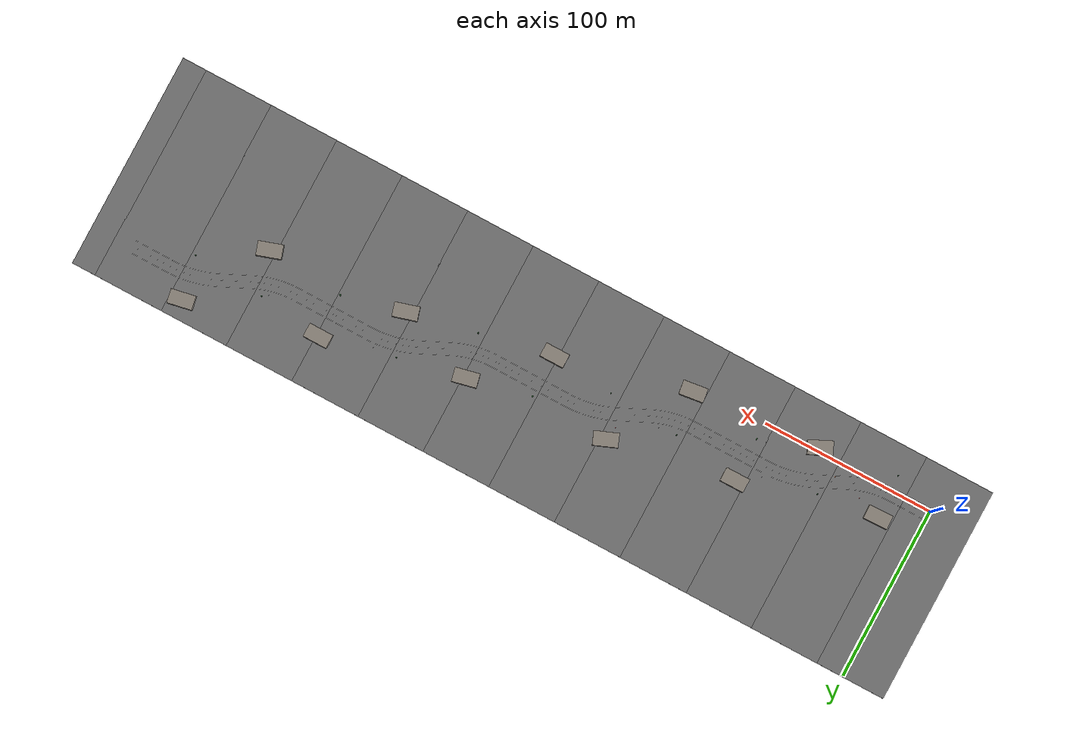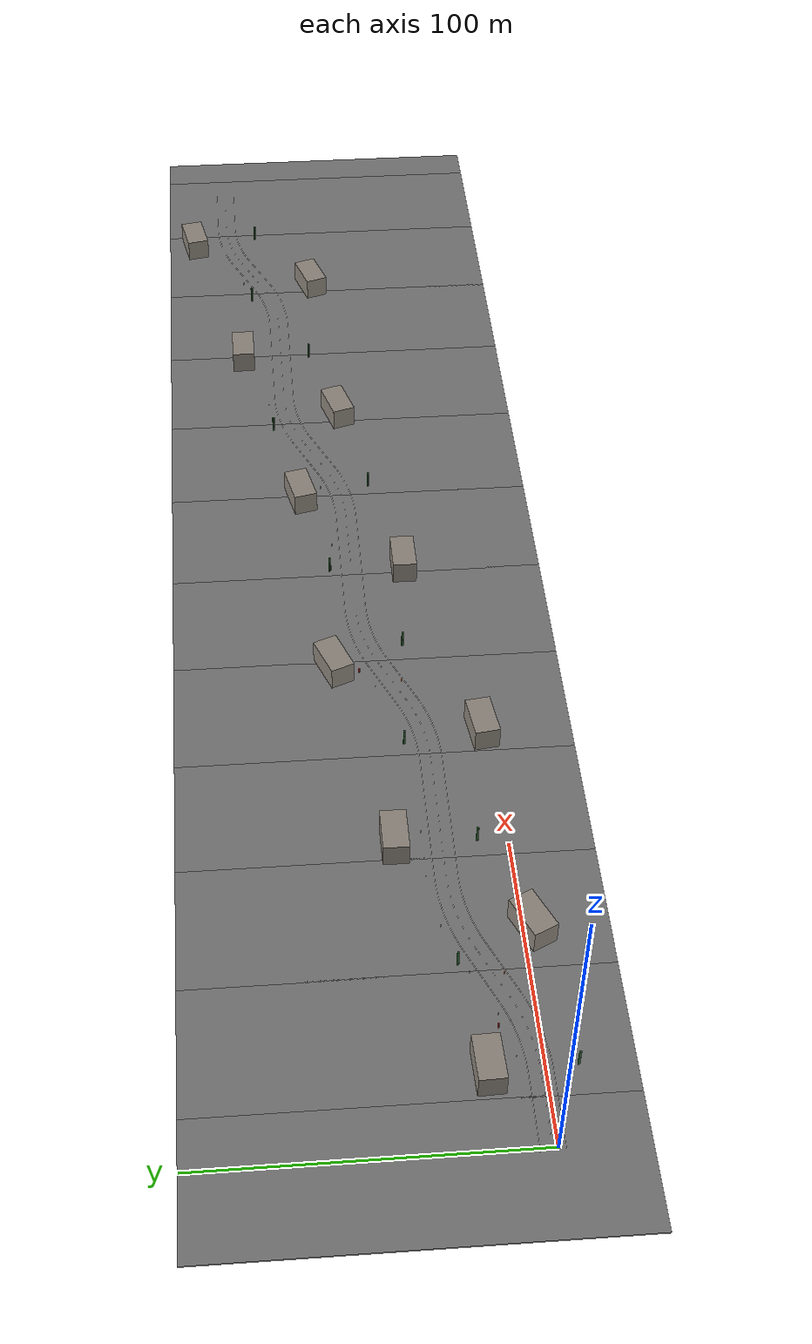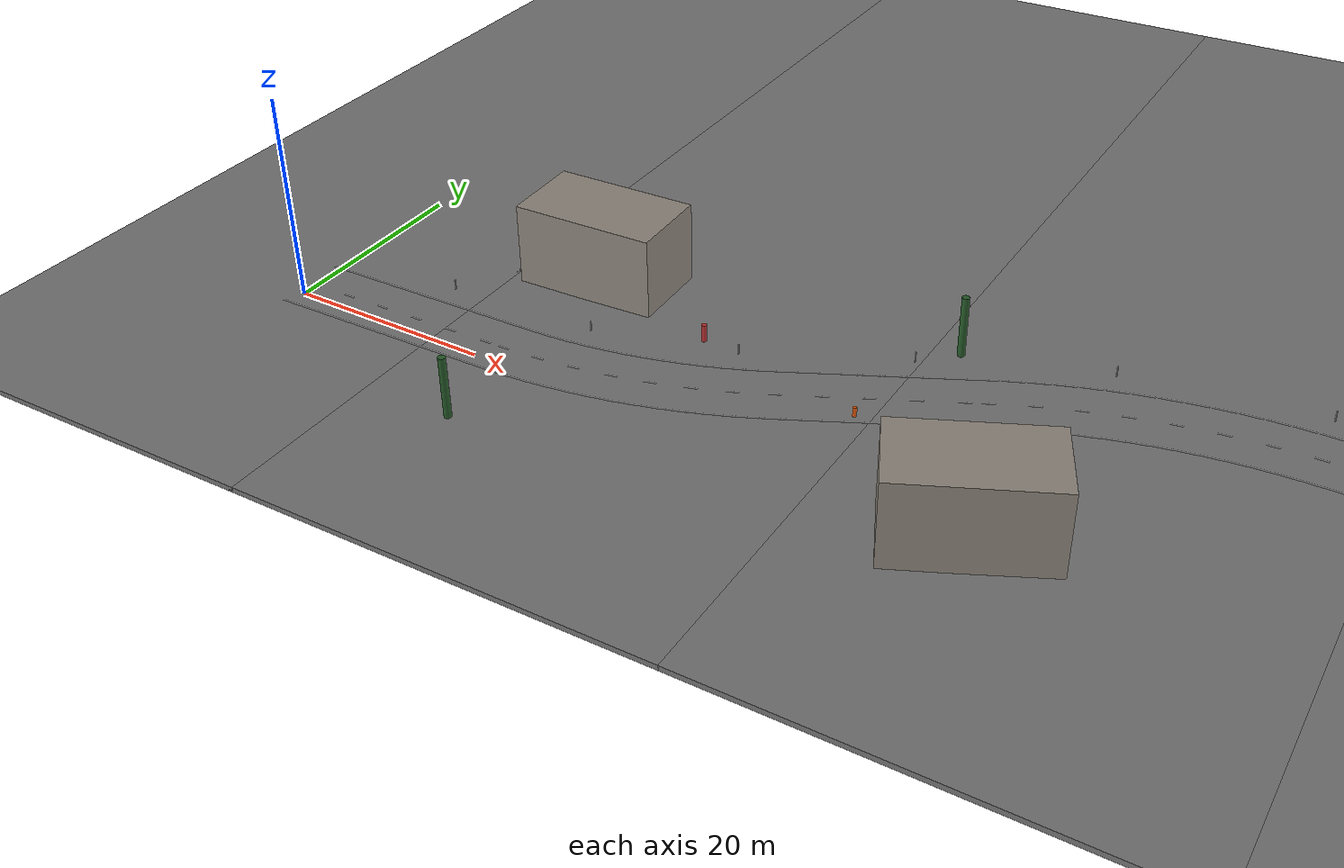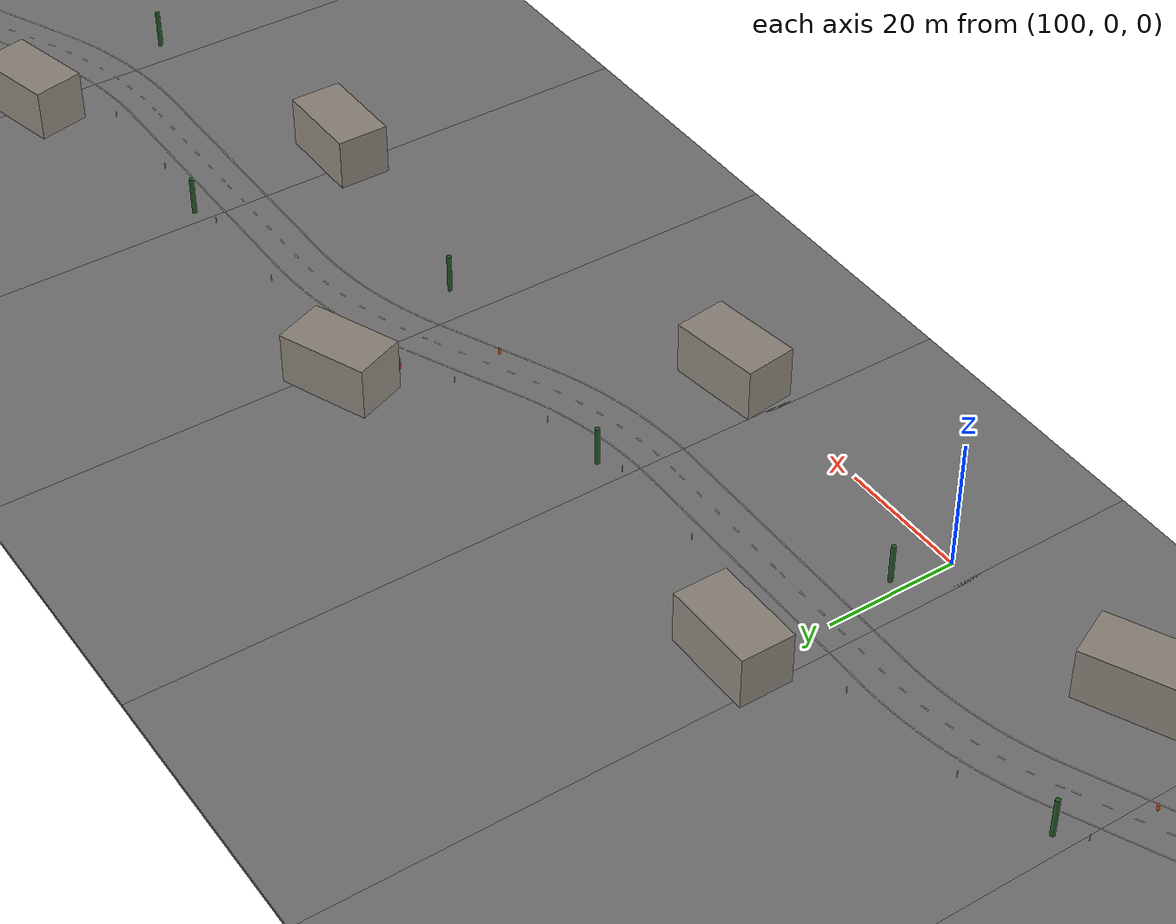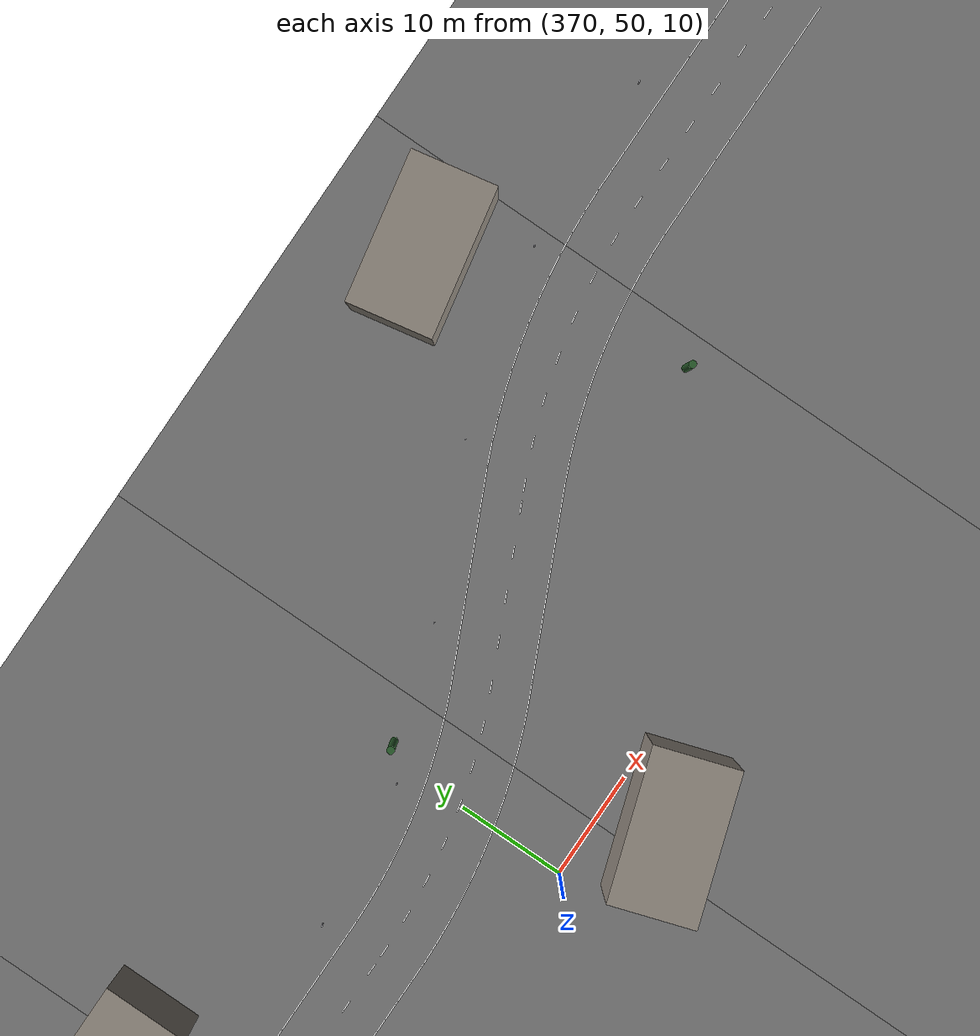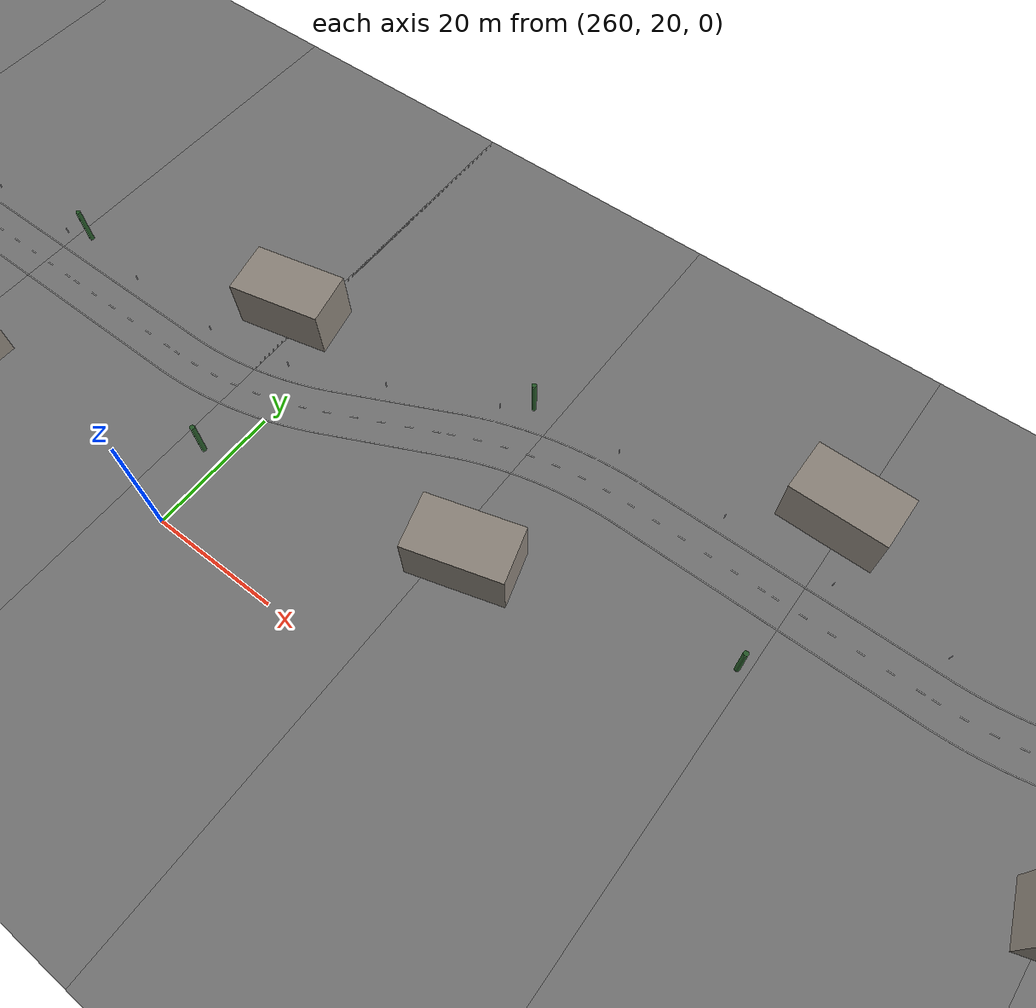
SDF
<?xml version="1.0"?>
<sdf version="1.4">
  <world name="marathon_course">
    <scene>
      <ambient>0.45 0.45 0.45 1</ambient>
      <background>0.75 0.82 0.9 1</background>
      <shadows>false</shadows>
    </scene>
    <include><uri>model://sun</uri></include>
    <model name='road_0'>
      <static>true</static>
      <pose>-4.79563689839068 37.70038853386919 -0.33374623544454224 0 -0.017453292519943295 0</pose>
      <link name='link'>
        <collision name='collision'><geometry><box><size>40.4 125.40077706773837 0.5</size></box></geometry></collision>
        <visual name='visual'>
          <geometry><box><size>40.4 125.40077706773837 0.5</size></box></geometry>
          <material><ambient>0.45 0.45 0.45 1</ambient><diffuse>0.45 0.45 0.45 1</diffuse></material>
        </visual>
      </link>
    </model>
    <model name='road_1'>
      <static>true</static>
      <pose>35.204363101609324 37.70038853386919 0.36445636168416123 0 -0.017453292519943295 0</pose>
      <link name='link'>
        <collision name='collision'><geometry><box><size>40.4 125.40077706773837 0.5</size></box></geometry></collision>
        <visual name='visual'>
          <geometry><box><size>40.4 125.40077706773837 0.5</size></box></geometry>
          <material><ambient>0.45 0.45 0.45 1</ambient><diffuse>0.45 0.45 0.45 1</diffuse></material>
        </visual>
      </link>
    </model>
    <model name='road_2'>
      <static>true</static>
      <pose>75.20436310160932 37.70038853386919 1.0626589588128648 0 -0.017453292519943295 0</pose>
      <link name='link'>
        <collision name='collision'><geometry><box><size>40.4 125.40077706773837 0.5</size></box></geometry></collision>
        <visual name='visual'>
          <geometry><box><size>40.4 125.40077706773837 0.5</size></box></geometry>
          <material><ambient>0.45 0.45 0.45 1</ambient><diffuse>0.45 0.45 0.45 1</diffuse></material>
        </visual>
      </link>
    </model>
    <model name='road_3'>
      <static>true</static>
      <pose>115.20436310160932 37.70038853386919 1.7608615559415683 0 -0.017453292519943295 0</pose>
      <link name='link'>
        <collision name='collision'><geometry><box><size>40.4 125.40077706773837 0.5</size></box></geometry></collision>
        <visual name='visual'>
          <geometry><box><size>40.4 125.40077706773837 0.5</size></box></geometry>
          <material><ambient>0.45 0.45 0.45 1</ambient><diffuse>0.45 0.45 0.45 1</diffuse></material>
        </visual>
      </link>
    </model>
    <model name='road_4'>
      <static>true</static>
      <pose>155.20436310160932 37.70038853386919 2.4590641530702713 0 -0.017453292519943295 0</pose>
      <link name='link'>
        <collision name='collision'><geometry><box><size>40.4 125.40077706773837 0.5</size></box></geometry></collision>
        <visual name='visual'>
          <geometry><box><size>40.4 125.40077706773837 0.5</size></box></geometry>
          <material><ambient>0.45 0.45 0.45 1</ambient><diffuse>0.45 0.45 0.45 1</diffuse></material>
        </visual>
      </link>
    </model>
    <model name='road_5'>
      <static>true</static>
      <pose>195.20436310160932 37.70038853386919 3.1572667501989744 0 -0.017453292519943295 0</pose>
      <link name='link'>
        <collision name='collision'><geometry><box><size>40.4 125.40077706773837 0.5</size></box></geometry></collision>
        <visual name='visual'>
          <geometry><box><size>40.4 125.40077706773837 0.5</size></box></geometry>
          <material><ambient>0.45 0.45 0.45 1</ambient><diffuse>0.45 0.45 0.45 1</diffuse></material>
        </visual>
      </link>
    </model>
    <model name='road_6'>
      <static>true</static>
      <pose>235.20436310160932 37.70038853386919 3.8554693473276775 0 -0.017453292519943295 0</pose>
      <link name='link'>
        <collision name='collision'><geometry><box><size>40.4 125.40077706773837 0.5</size></box></geometry></collision>
        <visual name='visual'>
          <geometry><box><size>40.4 125.40077706773837 0.5</size></box></geometry>
          <material><ambient>0.45 0.45 0.45 1</ambient><diffuse>0.45 0.45 0.45 1</diffuse></material>
        </visual>
      </link>
    </model>
    <model name='road_7'>
      <static>true</static>
      <pose>275.2043631016093 37.70038853386919 4.553671944456382 0 -0.017453292519943295 0</pose>
      <link name='link'>
        <collision name='collision'><geometry><box><size>40.4 125.40077706773837 0.5</size></box></geometry></collision>
        <visual name='visual'>
          <geometry><box><size>40.4 125.40077706773837 0.5</size></box></geometry>
          <material><ambient>0.45 0.45 0.45 1</ambient><diffuse>0.45 0.45 0.45 1</diffuse></material>
        </visual>
      </link>
    </model>
    <model name='road_8'>
      <static>true</static>
      <pose>315.2043631016093 37.70038853386919 5.251874541585085 0 -0.017453292519943295 0</pose>
      <link name='link'>
        <collision name='collision'><geometry><box><size>40.4 125.40077706773837 0.5</size></box></geometry></collision>
        <visual name='visual'>
          <geometry><box><size>40.4 125.40077706773837 0.5</size></box></geometry>
          <material><ambient>0.45 0.45 0.45 1</ambient><diffuse>0.45 0.45 0.45 1</diffuse></material>
        </visual>
      </link>
    </model>
    <model name='road_9'>
      <static>true</static>
      <pose>355.2043631016093 37.70038853386919 5.950077138713788 0 -0.017453292519943295 0</pose>
      <link name='link'>
        <collision name='collision'><geometry><box><size>40.4 125.40077706773837 0.5</size></box></geometry></collision>
        <visual name='visual'>
          <geometry><box><size>40.4 125.40077706773837 0.5</size></box></geometry>
          <material><ambient>0.45 0.45 0.45 1</ambient><diffuse>0.45 0.45 0.45 1</diffuse></material>
        </visual>
      </link>
    </model>
    <model name='road_10'>
      <static>true</static>
      <pose>395.2043631016093 37.70038853386919 6.648279735842492 0 -0.017453292519943295 0</pose>
      <link name='link'>
        <collision name='collision'><geometry><box><size>40.4 125.40077706773837 0.5</size></box></geometry></collision>
        <visual name='visual'>
          <geometry><box><size>40.4 125.40077706773837 0.5</size></box></geometry>
          <material><ambient>0.45 0.45 0.45 1</ambient><diffuse>0.45 0.45 0.45 1</diffuse></material>
        </visual>
      </link>
    </model>
    <model name='road_11'>
      <static>true</static>
      <pose>435.2043631016093 37.70038853386919 7.3464823329711955 0 -0.017453292519943295 0</pose>
      <link name='link'>
        <collision name='collision'><geometry><box><size>40.4 125.40077706773837 0.5</size></box></geometry></collision>
        <visual name='visual'>
          <geometry><box><size>40.4 125.40077706773837 0.5</size></box></geometry>
          <material><ambient>0.45 0.45 0.45 1</ambient><diffuse>0.45 0.45 0.45 1</diffuse></material>
        </visual>
      </link>
    </model>
    <model name='road_12'>
      <static>true</static>
      <pose>462.05982625269667 37.70038853386919 7.81524618595078 0 -0.017453292519943295 0</pose>
      <link name='link'>
        <collision name='collision'><geometry><box><size>14.110926302174619 125.40077706773837 0.5</size></box></geometry></collision>
        <visual name='visual'>
          <geometry><box><size>14.110926302174619 125.40077706773837 0.5</size></box></geometry>
          <material><ambient>0.45 0.45 0.45 1</ambient><diffuse>0.45 0.45 0.45 1</diffuse></material>
        </visual>
      </link>
    </model>

    <physics type="ode">
      <max_step_size>0.002</max_step_size>
      <real_time_update_rate>500</real_time_update_rate>
      <real_time_factor>1</real_time_factor>
    </physics>
    <model name='paint_left_edge_0'>
      <static>true</static>
      <pose>0.0 5.25 0.02 0 0 0.0</pose>
      <link name='link'>
        <visual name='visual'>
          <geometry><box><size>2.05 0.12 0.02</size></box></geometry>
          <material><ambient>0.95 0.95 0.95 1</ambient><diffuse>0.95 0.95 0.95 1</diffuse></material>
        </visual>
      </link>
    </model>
    <model name='paint_left_edge_1'>
      <static>true</static>
      <pose>2.0 5.25 0.054910129856435175 0 0 0.0</pose>
      <link name='link'>
        <visual name='visual'>
          <geometry><box><size>2.05 0.12 0.02</size></box></geometry>
          <material><ambient>0.95 0.95 0.95 1</ambient><diffuse>0.95 0.95 0.95 1</diffuse></material>
        </visual>
      </link>
    </model>
    <model name='paint_left_edge_2'>
      <static>true</static>
      <pose>4.0 5.25 0.08982025971287035 0 0 0.0</pose>
      <link name='link'>
        <visual name='visual'>
          <geometry><box><size>2.05 0.12 0.02</size></box></geometry>
          <material><ambient>0.95 0.95 0.95 1</ambient><diffuse>0.95 0.95 0.95 1</diffuse></material>
        </visual>
      </link>
    </model>
    <model name='paint_left_edge_3'>
      <static>true</static>
      <pose>6.0 5.25 0.12473038956930552 0 0 0.0</pose>
      <link name='link'>
        <visual name='visual'>
          <geometry><box><size>2.05 0.12 0.02</size></box></geometry>
          <material><ambient>0.95 0.95 0.95 1</ambient><diffuse>0.95 0.95 0.95 1</diffuse></material>
        </visual>
      </link>
    </model>
    <model name='paint_left_edge_4'>
      <static>true</static>
      <pose>8.0 5.25 0.15964051942574067 0 0 0.0</pose>
      <link name='link'>
        <visual name='visual'>
          <geometry><box><size>2.05 0.12 0.02</size></box></geometry>
          <material><ambient>0.95 0.95 0.95 1</ambient><diffuse>0.95 0.95 0.95 1</diffuse></material>
        </visual>
      </link>
    </model>
    <model name='paint_left_edge_5'>
      <static>true</static>
      <pose>10.0 5.25 0.19455064928217583 0 0 0.0</pose>
      <link name='link'>
        <visual name='visual'>
          <geometry><box><size>2.05 0.12 0.02</size></box></geometry>
          <material><ambient>0.95 0.95 0.95 1</ambient><diffuse>0.95 0.95 0.95 1</diffuse></material>
        </visual>
      </link>
    </model>
    <model name='paint_left_edge_6'>
      <static>true</static>
      <pose>12.0 5.25 0.22946077913861102 0 0 0.0</pose>
      <link name='link'>
        <visual name='visual'>
          <geometry><box><size>2.05 0.12 0.02</size></box></geometry>
          <material><ambient>0.95 0.95 0.95 1</ambient><diffuse>0.95 0.95 0.95 1</diffuse></material>
        </visual>
      </link>
    </model>
    <model name='paint_left_edge_7'>
      <static>true</static>
      <pose>14.0 5.25 0.2643709089950462 0 0 0.0</pose>
      <link name='link'>
        <visual name='visual'>
          <geometry><box><size>2.05 0.12 0.02</size></box></geometry>
          <material><ambient>0.95 0.95 0.95 1</ambient><diffuse>0.95 0.95 0.95 1</diffuse></material>
        </visual>
      </link>
    </model>
    <model name='paint_left_edge_8'>
      <static>true</static>
      <pose>16.0 5.25 0.2992810388514814 0 0 0.0</pose>
      <link name='link'>
        <visual name='visual'>
          <geometry><box><size>2.05 0.12 0.02</size></box></geometry>
          <material><ambient>0.95 0.95 0.95 1</ambient><diffuse>0.95 0.95 0.95 1</diffuse></material>
        </visual>
      </link>
    </model>
    <model name='paint_left_edge_9'>
      <static>true</static>
      <pose>18.0 5.25 0.33419116870791654 0 0 0.0</pose>
      <link name='link'>
        <visual name='visual'>
          <geometry><box><size>2.05 0.12 0.02</size></box></geometry>
          <material><ambient>0.95 0.95 0.95 1</ambient><diffuse>0.95 0.95 0.95 1</diffuse></material>
        </visual>
      </link>
    </model>
    <model name='paint_left_edge_10'>
      <static>true</static>
      <pose>20.0 5.25 0.3691012985643517 0 0 0.0</pose>
      <link name='link'>
        <visual name='visual'>
          <geometry><box><size>2.05 0.12 0.02</size></box></geometry>
          <material><ambient>0.95 0.95 0.95 1</ambient><diffuse>0.95 0.95 0.95 1</diffuse></material>
        </visual>
      </link>
    </model>
    <model name='paint_left_edge_11'>
      <static>true</static>
      <pose>22.0 5.25 0.4040114284207869 0 0 0.0</pose>
      <link name='link'>
        <visual name='visual'>
          <geometry><box><size>2.05 0.12 0.02</size></box></geometry>
          <material><ambient>0.95 0.95 0.95 1</ambient><diffuse>0.95 0.95 0.95 1</diffuse></material>
        </visual>
      </link>
    </model>
    <model name='paint_left_edge_12'>
      <static>true</static>
      <pose>23.837285309159466 5.280836239094929 0.4360813627838257 0 0 0.03356402407681403</pose>
      <link name='link'>
        <visual name='visual'>
          <geometry><box><size>2.05 0.12 0.02</size></box></geometry>
          <material><ambient>0.95 0.95 0.95 1</ambient><diffuse>0.95 0.95 0.95 1</diffuse></material>
        </visual>
      </link>
    </model>
    <model name='paint_left_edge_13'>
      <static>true</static>
      <pose>25.67250103040738 5.373310221269526 0.46811517235549366 0 0 0.06712804815362806</pose>
      <link name='link'>
        <visual name='visual'>
          <geometry><box><size>2.05 0.12 0.02</size></box></geometry>
          <material><ambient>0.95 0.95 0.95 1</ambient><diffuse>0.95 0.95 0.95 1</diffuse></material>
        </visual>
      </link>
    </model>
    <model name='paint_left_edge_14'>
      <static>true</static>
      <pose>27.503579907094558 5.527317780320154 0.5000767730367561 0 0 0.10069207223044209</pose>
      <link name='link'>
        <visual name='visual'>
          <geometry><box><size>2.05 0.12 0.02</size></box></geometry>
          <material><ambient>0.95 0.95 0.95 1</ambient><diffuse>0.95 0.95 0.95 1</diffuse></material>
        </visual>
      </link>
    </model>
    <model name='paint_left_edge_15'>
      <static>true</static>
      <pose>29.328459342470573 5.742685436286508 0.5319301620674135 0 0 0.13425609630725613</pose>
      <link name='link'>
        <visual name='visual'>
          <geometry><box><size>2.05 0.12 0.02</size></box></geometry>
          <material><ambient>0.95 0.95 0.95 1</ambient><diffuse>0.95 0.95 0.95 1</diffuse></material>
        </visual>
      </link>
    </model>
    <model name='paint_left_edge_16'>
      <static>true</static>
      <pose>31.145083723070986 6.019170590866038 0.5636394585809767 0 0 0.16782012038407015</pose>
      <link name='link'>
        <visual name='visual'>
          <geometry><box><size>2.05 0.12 0.02</size></box></geometry>
          <material><ambient>0.95 0.95 0.95 1</ambient><diffuse>0.95 0.95 0.95 1</diffuse></material>
        </visual>
      </link>
    </model>
    <model name='paint_left_edge_17'>
      <static>true</static>
      <pose>32.95140673423844 6.356461800685849 0.5951689440222382 0 0 0.20138414446088418</pose>
      <link name='link'>
        <visual name='visual'>
          <geometry><box><size>2.05 0.12 0.02</size></box></geometry>
          <material><ambient>0.95 0.95 0.95 1</ambient><diffuse>0.95 0.95 0.95 1</diffuse></material>
        </visual>
      </link>
    </model>
    <model name='paint_left_edge_18'>
      <static>true</static>
      <pose>34.745393665169054 6.7541791281243535 0.6264831023820059 0 0 0.2349481685376982</pose>
      <link name='link'>
        <visual name='visual'>
          <geometry><box><size>2.05 0.12 0.02</size></box></geometry>
          <material><ambient>0.95 0.95 0.95 1</ambient><diffuse>0.95 0.95 0.95 1</diffuse></material>
        </visual>
      </link>
    </model>
    <model name='paint_left_edge_19'>
      <static>true</static>
      <pose>36.52502370088806 7.211874569287456 0.6575466602036873 0 0 0.26851219261451226</pose>
      <link name='link'>
        <visual name='visual'>
          <geometry><box><size>2.05 0.12 0.02</size></box></geometry>
          <material><ambient>0.95 0.95 0.95 1</ambient><diffuse>0.95 0.95 0.95 1</diffuse></material>
        </visual>
      </link>
    </model>
    <model name='paint_left_edge_20'>
      <static>true</static>
      <pose>38.288292198572364 7.729032558657126 0.6883246263166475 0 0 0.3020762166913263</pose>
      <link name='link'>
        <visual name='visual'>
          <geometry><box><size>2.05 0.12 0.02</size></box></geometry>
          <material><ambient>0.95 0.95 0.95 1</ambient><diffuse>0.95 0.95 0.95 1</diffuse></material>
        </visual>
      </link>
    </model>
    <model name='paint_left_edge_21'>
      <static>true</static>
      <pose>40.03321294565636 8.305070549843947 0.7187823312515925 0 0 0.3356402407681403</pose>
      <link name='link'>
        <visual name='visual'>
          <geometry><box><size>2.05 0.12 0.02</size></box></geometry>
          <material><ambient>0.95 0.95 0.95 1</ambient><diffuse>0.95 0.95 0.95 1</diffuse></material>
        </visual>
      </link>
    </model>
    <model name='paint_left_edge_22'>
      <static>true</static>
      <pose>41.757820397177184 8.9393396717895 0.7488854662935764 0 0 0.36920426484495433</pose>
      <link name='link'>
        <visual name='visual'>
          <geometry><box><size>2.05 0.12 0.02</size></box></geometry>
          <material><ambient>0.95 0.95 0.95 1</ambient><diffuse>0.95 0.95 0.95 1</diffuse></material>
        </visual>
      </link>
    </model>
    <model name='paint_left_edge_23'>
      <static>true</static>
      <pose>43.4601718898391 9.631125459679376 0.7786001221286383 0 0 0.40276828892176836</pose>
      <link name='link'>
        <visual name='visual'>
          <geometry><box><size>2.05 0.12 0.02</size></box></geometry>
          <material><ambient>0.95 0.95 0.95 1</ambient><diffuse>0.95 0.95 0.95 1</diffuse></material>
        </visual>
      </link>
    </model>
    <model name='paint_left_edge_24'>
      <static>true</static>
      <pose>45.1383498303033 10.379648659743413 0.8078928270405433 0 0 0.4363323129985824</pose>
      <link name='link'>
        <visual name='visual'>
          <geometry><box><size>2.05 0.12 0.02</size></box></geometry>
          <material><ambient>0.95 0.95 0.95 1</ambient><diffuse>0.95 0.95 0.95 1</diffuse></material>
        </visual>
      </link>
    </model>
    <model name='paint_left_edge_25'>
      <static>true</static>
      <pose>46.950965404376596 11.224885183224812 0.8395321495758912 0 0 0.4363323129985824</pose>
      <link name='link'>
        <visual name='visual'>
          <geometry><box><size>2.05 0.12 0.02</size></box></geometry>
          <material><ambient>0.95 0.95 0.95 1</ambient><diffuse>0.95 0.95 0.95 1</diffuse></material>
        </visual>
      </link>
    </model>
    <model name='paint_left_edge_26'>
      <static>true</static>
      <pose>48.763580978449895 12.07012170670621 0.8711714721112389 0 0 0.4363323129985824</pose>
      <link name='link'>
        <visual name='visual'>
          <geometry><box><size>2.05 0.12 0.02</size></box></geometry>
          <material><ambient>0.95 0.95 0.95 1</ambient><diffuse>0.95 0.95 0.95 1</diffuse></material>
        </visual>
      </link>
    </model>
    <model name='paint_left_edge_27'>
      <static>true</static>
      <pose>50.5761965525232 12.91535823018761 0.9028107946465869 0 0 0.4363323129985824</pose>
      <link name='link'>
        <visual name='visual'>
          <geometry><box><size>2.05 0.12 0.02</size></box></geometry>
          <material><ambient>0.95 0.95 0.95 1</ambient><diffuse>0.95 0.95 0.95 1</diffuse></material>
        </visual>
      </link>
    </model>
    <model name='paint_left_edge_28'>
      <static>true</static>
      <pose>52.3888121265965 13.76059475366901 0.9344501171819347 0 0 0.4363323129985824</pose>
      <link name='link'>
        <visual name='visual'>
          <geometry><box><size>2.05 0.12 0.02</size></box></geometry>
          <material><ambient>0.95 0.95 0.95 1</ambient><diffuse>0.95 0.95 0.95 1</diffuse></material>
        </visual>
      </link>
    </model>
    <model name='paint_left_edge_29'>
      <static>true</static>
      <pose>54.2014277006698 14.605831277150408 0.9660894397172826 0 0 0.4363323129985824</pose>
      <link name='link'>
        <visual name='visual'>
          <geometry><box><size>2.05 0.12 0.02</size></box></geometry>
          <material><ambient>0.95 0.95 0.95 1</ambient><diffuse>0.95 0.95 0.95 1</diffuse></material>
        </visual>
      </link>
    </model>
    <model name='paint_left_edge_30'>
      <static>true</static>
      <pose>56.014043274743095 15.451067800631806 0.9977287622526303 0 0 0.4363323129985824</pose>
      <link name='link'>
        <visual name='visual'>
          <geometry><box><size>2.05 0.12 0.02</size></box></geometry>
          <material><ambient>0.95 0.95 0.95 1</ambient><diffuse>0.95 0.95 0.95 1</diffuse></material>
        </visual>
      </link>
    </model>
    <model name='paint_left_edge_31'>
      <static>true</static>
      <pose>57.8266588488164 16.296304324113205 1.0293680847879783 0 0 0.4363323129985824</pose>
      <link name='link'>
        <visual name='visual'>
          <geometry><box><size>2.05 0.12 0.02</size></box></geometry>
          <material><ambient>0.95 0.95 0.95 1</ambient><diffuse>0.95 0.95 0.95 1</diffuse></material>
        </visual>
      </link>
    </model>
    <model name='paint_left_edge_32'>
      <static>true</static>
      <pose>59.6392744228897 17.141540847594605 1.061007407323326 0 0 0.4363323129985824</pose>
      <link name='link'>
        <visual name='visual'>
          <geometry><box><size>2.05 0.12 0.02</size></box></geometry>
          <material><ambient>0.95 0.95 0.95 1</ambient><diffuse>0.95 0.95 0.95 1</diffuse></material>
        </visual>
      </link>
    </model>
    <model name='paint_left_edge_33'>
      <static>true</static>
      <pose>61.451889996963 17.986777371076002 1.092646729858674 0 0 0.4363323129985824</pose>
      <link name='link'>
        <visual name='visual'>
          <geometry><box><size>2.05 0.12 0.02</size></box></geometry>
          <material><ambient>0.95 0.95 0.95 1</ambient><diffuse>0.95 0.95 0.95 1</diffuse></material>
        </visual>
      </link>
    </model>
    <model name='paint_left_edge_34'>
      <static>true</static>
      <pose>63.45191028217373 18.87885296567287 1.1275572137947794 0 0 0.40276828892176836</pose>
      <link name='link'>
        <visual name='visual'>
          <geometry><box><size>2.05 0.12 0.02</size></box></geometry>
          <material><ambient>0.95 0.95 0.95 1</ambient><diffuse>0.95 0.95 0.95 1</diffuse></material>
        </visual>
      </link>
    </model>
    <model name='paint_left_edge_35'>
      <static>true</static>
      <pose>65.48074014329137 19.703310000555316 1.1629705707488946 0 0 0.36920426484495433</pose>
      <link name='link'>
        <visual name='visual'>
          <geometry><box><size>2.05 0.12 0.02</size></box></geometry>
          <material><ambient>0.95 0.95 0.95 1</ambient><diffuse>0.95 0.95 0.95 1</diffuse></material>
        </visual>
      </link>
    </model>
    <model name='paint_left_edge_36'>
      <static>true</static>
      <pose>67.53609422935044 20.459219776024682 1.1988469097715329 0 0 0.3356402407681403</pose>
      <link name='link'>
        <visual name='visual'>
          <geometry><box><size>2.05 0.12 0.02</size></box></geometry>
          <material><ambient>0.95 0.95 0.95 1</ambient><diffuse>0.95 0.95 0.95 1</diffuse></material>
        </visual>
      </link>
    </model>
    <model name='paint_left_edge_37'>
      <static>true</static>
      <pose>69.61565731149165 21.145730806617188 1.235145818392632 0 0 0.3020762166913262</pose>
      <link name='link'>
        <visual name='visual'>
          <geometry><box><size>2.05 0.12 0.02</size></box></geometry>
          <material><ambient>0.95 0.95 0.95 1</ambient><diffuse>0.95 0.95 0.95 1</diffuse></material>
        </visual>
      </link>
    </model>
    <model name='paint_left_edge_38'>
      <static>true</static>
      <pose>71.71708689092361 21.762069780249536 1.2718264081436939 0 0 0.2685121926145122</pose>
      <link name='link'>
        <visual name='visual'>
          <geometry><box><size>2.05 0.12 0.02</size></box></geometry>
          <material><ambient>0.95 0.95 0.95 1</ambient><diffuse>0.95 0.95 0.95 1</diffuse></material>
        </visual>
      </link>
    </model>
    <model name='paint_left_edge_39'>
      <static>true</static>
      <pose>73.83801583760243 22.30754242930693 1.3088473606161088 0 0 0.2349481685376982</pose>
      <link name='link'>
        <visual name='visual'>
          <geometry><box><size>2.05 0.12 0.02</size></box></geometry>
          <material><ambient>0.95 0.95 0.95 1</ambient><diffuse>0.95 0.95 0.95 1</diffuse></material>
        </visual>
      </link>
    </model>
    <model name='paint_left_edge_40'>
      <static>true</static>
      <pose>75.97605505665673 22.781534312692557 1.3461669740037774 0 0 0.20138414446088418</pose>
      <link name='link'>
        <visual name='visual'>
          <geometry><box><size>2.05 0.12 0.02</size></box></geometry>
          <material><ambient>0.95 0.95 0.95 1</ambient><diffuse>0.95 0.95 0.95 1</diffuse></material>
        </visual>
      </link>
    </model>
    <model name='paint_left_edge_41'>
      <static>true</static>
      <pose>78.12879617955491 23.183511507957263 1.383743210077609 0 0 0.16782012038407013</pose>
      <link name='link'>
        <visual name='visual'>
          <geometry><box><size>2.05 0.12 0.02</size></box></geometry>
          <material><ambient>0.95 0.95 0.95 1</ambient><diffuse>0.95 0.95 0.95 1</diffuse></material>
        </visual>
      </link>
    </model>
    <model name='paint_left_edge_42'>
      <static>true</static>
      <pose>80.2938142769828 23.513021212730116 1.421533741538979 0 0 0.1342560963072561</pose>
      <link name='link'>
        <visual name='visual'>
          <geometry><box><size>2.05 0.12 0.02</size></box></geometry>
          <material><ambient>0.95 0.95 0.95 1</ambient><diffuse>0.95 0.95 0.95 1</diffuse></material>
        </visual>
      </link>
    </model>
    <model name='paint_left_edge_43'>
      <static>true</static>
      <pose>82.46867059037615 23.769692254772217 1.4594959996988037 0 0 0.10069207223044208</pose>
      <link name='link'>
        <visual name='visual'>
          <geometry><box><size>2.05 0.12 0.02</size></box></geometry>
          <material><ambient>0.95 0.95 0.95 1</ambient><diffuse>0.95 0.95 0.95 1</diffuse></material>
        </visual>
      </link>
    </model>
    <model name='paint_left_edge_44'>
      <static>true</static>
      <pose>84.65091527903073 23.953235510079132 1.4975872224285274 0 0 0.06712804815362805</pose>
      <link name='link'>
        <visual name='visual'>
          <geometry><box><size>2.05 0.12 0.02</size></box></geometry>
          <material><ambient>0.95 0.95 0.95 1</ambient><diffuse>0.95 0.95 0.95 1</diffuse></material>
        </visual>
      </link>
    </model>
    <model name='paint_left_edge_45'>
      <static>true</static>
      <pose>86.83809017969605 24.063444228561185 1.5357645023290085 0 0 0.033564024076814025</pose>
      <link name='link'>
        <visual name='visual'>
          <geometry><box><size>2.05 0.12 0.02</size></box></geometry>
          <material><ambient>0.95 0.95 0.95 1</ambient><diffuse>0.95 0.95 0.95 1</diffuse></material>
        </visual>
      </link>
    </model>
    <model name='paint_left_edge_46'>
      <static>true</static>
      <pose>89.02773157554364 24.100194266934594 1.5739848350630412 0 0 0.0</pose>
      <link name='link'>
        <visual name='visual'>
          <geometry><box><size>2.05 0.12 0.02</size></box></geometry>
          <material><ambient>0.95 0.95 0.95 1</ambient><diffuse>0.95 0.95 0.95 1</diffuse></material>
        </visual>
      </link>
    </model>
    <model name='paint_left_edge_47'>
      <static>true</static>
      <pose>91.02773157554364 24.100194266934594 1.6088949649194764 0 0 0.0</pose>
      <link name='link'>
        <visual name='visual'>
          <geometry><box><size>2.05 0.12 0.02</size></box></geometry>
          <material><ambient>0.95 0.95 0.95 1</ambient><diffuse>0.95 0.95 0.95 1</diffuse></material>
        </visual>
      </link>
    </model>
    <model name='paint_left_edge_48'>
      <static>true</static>
      <pose>93.02773157554364 24.100194266934594 1.6438050947759115 0 0 0.0</pose>
      <link name='link'>
        <visual name='visual'>
          <geometry><box><size>2.05 0.12 0.02</size></box></geometry>
          <material><ambient>0.95 0.95 0.95 1</ambient><diffuse>0.95 0.95 0.95 1</diffuse></material>
        </visual>
      </link>
    </model>
    <model name='paint_left_edge_49'>
      <static>true</static>
      <pose>95.02773157554364 24.100194266934594 1.6787152246323467 0 0 0.0</pose>
      <link name='link'>
        <visual name='visual'>
          <geometry><box><size>2.05 0.12 0.02</size></box></geometry>
          <material><ambient>0.95 0.95 0.95 1</ambient><diffuse>0.95 0.95 0.95 1</diffuse></material>
        </visual>
      </link>
    </model>
    <model name='paint_left_edge_50'>
      <static>true</static>
      <pose>97.02773157554364 24.100194266934594 1.7136253544887818 0 0 0.0</pose>
      <link name='link'>
        <visual name='visual'>
          <geometry><box><size>2.05 0.12 0.02</size></box></geometry>
          <material><ambient>0.95 0.95 0.95 1</ambient><diffuse>0.95 0.95 0.95 1</diffuse></material>
        </visual>
      </link>
    </model>
    <model name='paint_left_edge_51'>
      <static>true</static>
      <pose>99.02773157554364 24.100194266934594 1.748535484345217 0 0 0.0</pose>
      <link name='link'>
        <visual name='visual'>
          <geometry><box><size>2.05 0.12 0.02</size></box></geometry>
          <material><ambient>0.95 0.95 0.95 1</ambient><diffuse>0.95 0.95 0.95 1</diffuse></material>
        </visual>
      </link>
    </model>
    <model name='paint_left_edge_52'>
      <static>true</static>
      <pose>101.02773157554364 24.100194266934594 1.7834456142016522 0 0 0.0</pose>
      <link name='link'>
        <visual name='visual'>
          <geometry><box><size>2.05 0.12 0.02</size></box></geometry>
          <material><ambient>0.95 0.95 0.95 1</ambient><diffuse>0.95 0.95 0.95 1</diffuse></material>
        </visual>
      </link>
    </model>
    <model name='paint_left_edge_53'>
      <static>true</static>
      <pose>103.02773157554364 24.100194266934594 1.8183557440580873 0 0 0.0</pose>
      <link name='link'>
        <visual name='visual'>
          <geometry><box><size>2.05 0.12 0.02</size></box></geometry>
          <material><ambient>0.95 0.95 0.95 1</ambient><diffuse>0.95 0.95 0.95 1</diffuse></material>
        </visual>
      </link>
    </model>
    <model name='paint_left_edge_54'>
      <static>true</static>
      <pose>105.02773157554364 24.100194266934594 1.8532658739145225 0 0 0.0</pose>
      <link name='link'>
        <visual name='visual'>
          <geometry><box><size>2.05 0.12 0.02</size></box></geometry>
          <material><ambient>0.95 0.95 0.95 1</ambient><diffuse>0.95 0.95 0.95 1</diffuse></material>
        </visual>
      </link>
    </model>
    <model name='paint_left_edge_55'>
      <static>true</static>
      <pose>107.02773157554364 24.100194266934594 1.8881760037709576 0 0 0.0</pose>
      <link name='link'>
        <visual name='visual'>
          <geometry><box><size>2.05 0.12 0.02</size></box></geometry>
          <material><ambient>0.95 0.95 0.95 1</ambient><diffuse>0.95 0.95 0.95 1</diffuse></material>
        </visual>
      </link>
    </model>
    <model name='paint_left_edge_56'>
      <static>true</static>
      <pose>109.02773157554364 24.100194266934594 1.9230861336273928 0 0 0.0</pose>
      <link name='link'>
        <visual name='visual'>
          <geometry><box><size>2.05 0.12 0.02</size></box></geometry>
          <material><ambient>0.95 0.95 0.95 1</ambient><diffuse>0.95 0.95 0.95 1</diffuse></material>
        </visual>
      </link>
    </model>
    <model name='paint_left_edge_57'>
      <static>true</static>
      <pose>111.02773157554364 24.100194266934594 1.957996263483828 0 0 0.0</pose>
      <link name='link'>
        <visual name='visual'>
          <geometry><box><size>2.05 0.12 0.02</size></box></geometry>
          <material><ambient>0.95 0.95 0.95 1</ambient><diffuse>0.95 0.95 0.95 1</diffuse></material>
        </visual>
      </link>
    </model>
    <model name='paint_left_edge_58'>
      <static>true</static>
      <pose>113.02773157554364 24.100194266934594 1.992906393340263 0 0 0.0</pose>
      <link name='link'>
        <visual name='visual'>
          <geometry><box><size>2.05 0.12 0.02</size></box></geometry>
          <material><ambient>0.95 0.95 0.95 1</ambient><diffuse>0.95 0.95 0.95 1</diffuse></material>
        </visual>
      </link>
    </model>
    <model name='paint_left_edge_59'>
      <static>true</static>
      <pose>115.02773157554364 24.100194266934594 2.0278165231966985 0 0 0.0</pose>
      <link name='link'>
        <visual name='visual'>
          <geometry><box><size>2.05 0.12 0.02</size></box></geometry>
          <material><ambient>0.95 0.95 0.95 1</ambient><diffuse>0.95 0.95 0.95 1</diffuse></material>
        </visual>
      </link>
    </model>
    <model name='paint_left_edge_60'>
      <static>true</static>
      <pose>117.02773157554364 24.100194266934594 2.0627266530531334 0 0 0.0</pose>
      <link name='link'>
        <visual name='visual'>
          <geometry><box><size>2.05 0.12 0.02</size></box></geometry>
          <material><ambient>0.95 0.95 0.95 1</ambient><diffuse>0.95 0.95 0.95 1</diffuse></material>
        </visual>
      </link>
    </model>
    <model name='paint_left_edge_61'>
      <static>true</static>
      <pose>119.02773157554364 24.100194266934594 2.097636782909569 0 0 0.0</pose>
      <link name='link'>
        <visual name='visual'>
          <geometry><box><size>2.05 0.12 0.02</size></box></geometry>
          <material><ambient>0.95 0.95 0.95 1</ambient><diffuse>0.95 0.95 0.95 1</diffuse></material>
        </visual>
      </link>
    </model>
    <model name='paint_left_edge_62'>
      <static>true</static>
      <pose>121.02773157554364 24.100194266934594 2.1325469127660037 0 0 0.0</pose>
      <link name='link'>
        <visual name='visual'>
          <geometry><box><size>2.05 0.12 0.02</size></box></geometry>
          <material><ambient>0.95 0.95 0.95 1</ambient><diffuse>0.95 0.95 0.95 1</diffuse></material>
        </visual>
      </link>
    </model>
    <model name='paint_left_edge_63'>
      <static>true</static>
      <pose>123.02773157554364 24.100194266934594 2.167457042622439 0 0 0.0</pose>
      <link name='link'>
        <visual name='visual'>
          <geometry><box><size>2.05 0.12 0.02</size></box></geometry>
          <material><ambient>0.95 0.95 0.95 1</ambient><diffuse>0.95 0.95 0.95 1</diffuse></material>
        </visual>
      </link>
    </model>
    <model name='paint_left_edge_64'>
      <static>true</static>
      <pose>125.02773157554364 24.100194266934594 2.202367172478874 0 0 0.0</pose>
      <link name='link'>
        <visual name='visual'>
          <geometry><box><size>2.05 0.12 0.02</size></box></geometry>
          <material><ambient>0.95 0.95 0.95 1</ambient><diffuse>0.95 0.95 0.95 1</diffuse></material>
        </visual>
      </link>
    </model>
    <model name='paint_left_edge_65'>
      <static>true</static>
      <pose>127.02773157554364 24.100194266934594 2.2372773023353094 0 0 0.0</pose>
      <link name='link'>
        <visual name='visual'>
          <geometry><box><size>2.05 0.12 0.02</size></box></geometry>
          <material><ambient>0.95 0.95 0.95 1</ambient><diffuse>0.95 0.95 0.95 1</diffuse></material>
        </visual>
      </link>
    </model>
    <model name='paint_left_edge_66'>
      <static>true</static>
      <pose>129.02773157554364 24.100194266934594 2.2721874321917443 0 0 0.0</pose>
      <link name='link'>
        <visual name='visual'>
          <geometry><box><size>2.05 0.12 0.02</size></box></geometry>
          <material><ambient>0.95 0.95 0.95 1</ambient><diffuse>0.95 0.95 0.95 1</diffuse></material>
        </visual>
      </link>
    </model>
    <model name='paint_left_edge_67'>
      <static>true</static>
      <pose>131.02773157554364 24.100194266934594 2.3070975620481797 0 0 0.0</pose>
      <link name='link'>
        <visual name='visual'>
          <geometry><box><size>2.05 0.12 0.02</size></box></geometry>
          <material><ambient>0.95 0.95 0.95 1</ambient><diffuse>0.95 0.95 0.95 1</diffuse></material>
        </visual>
      </link>
    </model>
    <model name='paint_left_edge_68'>
      <static>true</static>
      <pose>133.02773157554364 24.100194266934594 2.342007691904615 0 0 0.0</pose>
      <link name='link'>
        <visual name='visual'>
          <geometry><box><size>2.05 0.12 0.02</size></box></geometry>
          <material><ambient>0.95 0.95 0.95 1</ambient><diffuse>0.95 0.95 0.95 1</diffuse></material>
        </visual>
      </link>
    </model>
    <model name='paint_left_edge_69'>
      <static>true</static>
      <pose>134.8650168847031 24.13103050602952 2.3740776262676535 0 0 0.03356402407681403</pose>
      <link name='link'>
        <visual name='visual'>
          <geometry><box><size>2.05 0.12 0.02</size></box></geometry>
          <material><ambient>0.95 0.95 0.95 1</ambient><diffuse>0.95 0.95 0.95 1</diffuse></material>
        </visual>
      </link>
    </model>
    <model name='paint_left_edge_70'>
      <static>true</static>
      <pose>136.70023260595102 24.22350448820412 2.4061114358393216 0 0 0.06712804815362806</pose>
      <link name='link'>
        <visual name='visual'>
          <geometry><box><size>2.05 0.12 0.02</size></box></geometry>
          <material><ambient>0.95 0.95 0.95 1</ambient><diffuse>0.95 0.95 0.95 1</diffuse></material>
        </visual>
      </link>
    </model>
    <model name='paint_left_edge_71'>
      <static>true</static>
      <pose>138.5313114826382 24.377512047254747 2.438073036520584 0 0 0.10069207223044209</pose>
      <link name='link'>
        <visual name='visual'>
          <geometry><box><size>2.05 0.12 0.02</size></box></geometry>
          <material><ambient>0.95 0.95 0.95 1</ambient><diffuse>0.95 0.95 0.95 1</diffuse></material>
        </visual>
      </link>
    </model>
    <model name='paint_left_edge_72'>
      <static>true</static>
      <pose>140.35619091801422 24.5928797032211 2.4699264255512414 0 0 0.13425609630725613</pose>
      <link name='link'>
        <visual name='visual'>
          <geometry><box><size>2.05 0.12 0.02</size></box></geometry>
          <material><ambient>0.95 0.95 0.95 1</ambient><diffuse>0.95 0.95 0.95 1</diffuse></material>
        </visual>
      </link>
    </model>
    <model name='paint_left_edge_73'>
      <static>true</static>
      <pose>142.17281529861464 24.869364857800633 2.501635722064805 0 0 0.16782012038407015</pose>
      <link name='link'>
        <visual name='visual'>
          <geometry><box><size>2.05 0.12 0.02</size></box></geometry>
          <material><ambient>0.95 0.95 0.95 1</ambient><diffuse>0.95 0.95 0.95 1</diffuse></material>
        </visual>
      </link>
    </model>
    <model name='paint_left_edge_74'>
      <static>true</static>
      <pose>143.9791383097821 25.206656067620443 2.5331652075060664 0 0 0.20138414446088418</pose>
      <link name='link'>
        <visual name='visual'>
          <geometry><box><size>2.05 0.12 0.02</size></box></geometry>
          <material><ambient>0.95 0.95 0.95 1</ambient><diffuse>0.95 0.95 0.95 1</diffuse></material>
        </visual>
      </link>
    </model>
    <model name='paint_left_edge_75'>
      <static>true</static>
      <pose>145.77312524071272 25.604373395058946 2.564479365865834 0 0 0.2349481685376982</pose>
      <link name='link'>
        <visual name='visual'>
          <geometry><box><size>2.05 0.12 0.02</size></box></geometry>
          <material><ambient>0.95 0.95 0.95 1</ambient><diffuse>0.95 0.95 0.95 1</diffuse></material>
        </visual>
      </link>
    </model>
    <model name='paint_left_edge_76'>
      <static>true</static>
      <pose>147.5527552764317 26.06206883622205 2.5955429236875154 0 0 0.26851219261451226</pose>
      <link name='link'>
        <visual name='visual'>
          <geometry><box><size>2.05 0.12 0.02</size></box></geometry>
          <material><ambient>0.95 0.95 0.95 1</ambient><diffuse>0.95 0.95 0.95 1</diffuse></material>
        </visual>
      </link>
    </model>
    <model name='paint_left_edge_77'>
      <static>true</static>
      <pose>149.316023774116 26.579226825591718 2.6263208898004753 0 0 0.3020762166913263</pose>
      <link name='link'>
        <visual name='visual'>
          <geometry><box><size>2.05 0.12 0.02</size></box></geometry>
          <material><ambient>0.95 0.95 0.95 1</ambient><diffuse>0.95 0.95 0.95 1</diffuse></material>
        </visual>
      </link>
    </model>
    <model name='paint_left_edge_78'>
      <static>true</static>
      <pose>151.06094452119999 27.15526481677854 2.65677859473542 0 0 0.3356402407681403</pose>
      <link name='link'>
        <visual name='visual'>
          <geometry><box><size>2.05 0.12 0.02</size></box></geometry>
          <material><ambient>0.95 0.95 0.95 1</ambient><diffuse>0.95 0.95 0.95 1</diffuse></material>
        </visual>
      </link>
    </model>
    <model name='paint_left_edge_79'>
      <static>true</static>
      <pose>152.7855519727208 27.789533938724094 2.6868817297774044 0 0 0.36920426484495433</pose>
      <link name='link'>
        <visual name='visual'>
          <geometry><box><size>2.05 0.12 0.02</size></box></geometry>
          <material><ambient>0.95 0.95 0.95 1</ambient><diffuse>0.95 0.95 0.95 1</diffuse></material>
        </visual>
      </link>
    </model>
    <model name='paint_left_edge_80'>
      <static>true</static>
      <pose>154.48790346538277 28.481319726613968 2.716596385612467 0 0 0.40276828892176836</pose>
      <link name='link'>
        <visual name='visual'>
          <geometry><box><size>2.05 0.12 0.02</size></box></geometry>
          <material><ambient>0.95 0.95 0.95 1</ambient><diffuse>0.95 0.95 0.95 1</diffuse></material>
        </visual>
      </link>
    </model>
    <model name='paint_left_edge_81'>
      <static>true</static>
      <pose>156.16608140584694 29.229842926678007 2.745889090524371 0 0 0.4363323129985824</pose>
      <link name='link'>
        <visual name='visual'>
          <geometry><box><size>2.05 0.12 0.02</size></box></geometry>
          <material><ambient>0.95 0.95 0.95 1</ambient><diffuse>0.95 0.95 0.95 1</diffuse></material>
        </visual>
      </link>
    </model>
    <model name='paint_left_edge_82'>
      <static>true</static>
      <pose>157.97869697992024 30.075079450159407 2.777528413059719 0 0 0.4363323129985824</pose>
      <link name='link'>
        <visual name='visual'>
          <geometry><box><size>2.05 0.12 0.02</size></box></geometry>
          <material><ambient>0.95 0.95 0.95 1</ambient><diffuse>0.95 0.95 0.95 1</diffuse></material>
        </visual>
      </link>
    </model>
    <model name='paint_left_edge_83'>
      <static>true</static>
      <pose>159.79131255399355 30.920315973640804 2.809167735595067 0 0 0.4363323129985824</pose>
      <link name='link'>
        <visual name='visual'>
          <geometry><box><size>2.05 0.12 0.02</size></box></geometry>
          <material><ambient>0.95 0.95 0.95 1</ambient><diffuse>0.95 0.95 0.95 1</diffuse></material>
        </visual>
      </link>
    </model>
    <model name='paint_left_edge_84'>
      <static>true</static>
      <pose>161.60392812806683 31.765552497122204 2.8408070581304146 0 0 0.4363323129985824</pose>
      <link name='link'>
        <visual name='visual'>
          <geometry><box><size>2.05 0.12 0.02</size></box></geometry>
          <material><ambient>0.95 0.95 0.95 1</ambient><diffuse>0.95 0.95 0.95 1</diffuse></material>
        </visual>
      </link>
    </model>
    <model name='paint_left_edge_85'>
      <static>true</static>
      <pose>163.41654370214013 32.610789020603605 2.8724463806657625 0 0 0.4363323129985824</pose>
      <link name='link'>
        <visual name='visual'>
          <geometry><box><size>2.05 0.12 0.02</size></box></geometry>
          <material><ambient>0.95 0.95 0.95 1</ambient><diffuse>0.95 0.95 0.95 1</diffuse></material>
        </visual>
      </link>
    </model>
    <model name='paint_left_edge_86'>
      <static>true</static>
      <pose>165.22915927621344 33.456025544085 2.9040857032011105 0 0 0.4363323129985824</pose>
      <link name='link'>
        <visual name='visual'>
          <geometry><box><size>2.05 0.12 0.02</size></box></geometry>
          <material><ambient>0.95 0.95 0.95 1</ambient><diffuse>0.95 0.95 0.95 1</diffuse></material>
        </visual>
      </link>
    </model>
    <model name='paint_left_edge_87'>
      <static>true</static>
      <pose>167.04177485028674 34.3012620675664 2.9357250257364584 0 0 0.4363323129985824</pose>
      <link name='link'>
        <visual name='visual'>
          <geometry><box><size>2.05 0.12 0.02</size></box></geometry>
          <material><ambient>0.95 0.95 0.95 1</ambient><diffuse>0.95 0.95 0.95 1</diffuse></material>
        </visual>
      </link>
    </model>
    <model name='paint_left_edge_88'>
      <static>true</static>
      <pose>168.85439042436005 35.1464985910478 2.9673643482718064 0 0 0.4363323129985824</pose>
      <link name='link'>
        <visual name='visual'>
          <geometry><box><size>2.05 0.12 0.02</size></box></geometry>
          <material><ambient>0.95 0.95 0.95 1</ambient><diffuse>0.95 0.95 0.95 1</diffuse></material>
        </visual>
      </link>
    </model>
    <model name='paint_left_edge_89'>
      <static>true</static>
      <pose>170.66700599843332 35.9917351145292 2.999003670807154 0 0 0.4363323129985824</pose>
      <link name='link'>
        <visual name='visual'>
          <geometry><box><size>2.05 0.12 0.02</size></box></geometry>
          <material><ambient>0.95 0.95 0.95 1</ambient><diffuse>0.95 0.95 0.95 1</diffuse></material>
        </visual>
      </link>
    </model>
    <model name='paint_left_edge_90'>
      <static>true</static>
      <pose>172.47962157250663 36.836971638010596 3.030642993342502 0 0 0.4363323129985824</pose>
      <link name='link'>
        <visual name='visual'>
          <geometry><box><size>2.05 0.12 0.02</size></box></geometry>
          <material><ambient>0.95 0.95 0.95 1</ambient><diffuse>0.95 0.95 0.95 1</diffuse></material>
        </visual>
      </link>
    </model>
    <model name='paint_left_edge_91'>
      <static>true</static>
      <pose>174.47964185771738 37.72904723260747 3.0655534772786077 0 0 0.40276828892176836</pose>
      <link name='link'>
        <visual name='visual'>
          <geometry><box><size>2.05 0.12 0.02</size></box></geometry>
          <material><ambient>0.95 0.95 0.95 1</ambient><diffuse>0.95 0.95 0.95 1</diffuse></material>
        </visual>
      </link>
    </model>
    <model name='paint_left_edge_92'>
      <static>true</static>
      <pose>176.508471718835 38.55350426748992 3.1009668342327226 0 0 0.36920426484495433</pose>
      <link name='link'>
        <visual name='visual'>
          <geometry><box><size>2.05 0.12 0.02</size></box></geometry>
          <material><ambient>0.95 0.95 0.95 1</ambient><diffuse>0.95 0.95 0.95 1</diffuse></material>
        </visual>
      </link>
    </model>
    <model name='paint_left_edge_93'>
      <static>true</static>
      <pose>178.56382580489407 39.30941404295928 3.1368431732553606 0 0 0.3356402407681403</pose>
      <link name='link'>
        <visual name='visual'>
          <geometry><box><size>2.05 0.12 0.02</size></box></geometry>
          <material><ambient>0.95 0.95 0.95 1</ambient><diffuse>0.95 0.95 0.95 1</diffuse></material>
        </visual>
      </link>
    </model>
    <model name='paint_left_edge_94'>
      <static>true</static>
      <pose>180.64338888703526 39.99592507355179 3.1731420818764593 0 0 0.3020762166913262</pose>
      <link name='link'>
        <visual name='visual'>
          <geometry><box><size>2.05 0.12 0.02</size></box></geometry>
          <material><ambient>0.95 0.95 0.95 1</ambient><diffuse>0.95 0.95 0.95 1</diffuse></material>
        </visual>
      </link>
    </model>
    <model name='paint_left_edge_95'>
      <static>true</static>
      <pose>182.74481846646725 40.61226404718414 3.209822671627522 0 0 0.2685121926145122</pose>
      <link name='link'>
        <visual name='visual'>
          <geometry><box><size>2.05 0.12 0.02</size></box></geometry>
          <material><ambient>0.95 0.95 0.95 1</ambient><diffuse>0.95 0.95 0.95 1</diffuse></material>
        </visual>
      </link>
    </model>
    <model name='paint_left_edge_96'>
      <static>true</static>
      <pose>184.86574741314607 41.157736696241535 3.2468436240999368 0 0 0.2349481685376982</pose>
      <link name='link'>
        <visual name='visual'>
          <geometry><box><size>2.05 0.12 0.02</size></box></geometry>
          <material><ambient>0.95 0.95 0.95 1</ambient><diffuse>0.95 0.95 0.95 1</diffuse></material>
        </visual>
      </link>
    </model>
    <model name='paint_left_edge_97'>
      <static>true</static>
      <pose>187.0037866322004 41.63172857962716 3.2841632374876055 0 0 0.20138414446088418</pose>
      <link name='link'>
        <visual name='visual'>
          <geometry><box><size>2.05 0.12 0.02</size></box></geometry>
          <material><ambient>0.95 0.95 0.95 1</ambient><diffuse>0.95 0.95 0.95 1</diffuse></material>
        </visual>
      </link>
    </model>
    <model name='paint_left_edge_98'>
      <static>true</static>
      <pose>189.15652775509855 42.033705774891864 3.321739473561437 0 0 0.16782012038407013</pose>
      <link name='link'>
        <visual name='visual'>
          <geometry><box><size>2.05 0.12 0.02</size></box></geometry>
          <material><ambient>0.95 0.95 0.95 1</ambient><diffuse>0.95 0.95 0.95 1</diffuse></material>
        </visual>
      </link>
    </model>
    <model name='paint_left_edge_99'>
      <static>true</static>
      <pose>191.32154585252647 42.36321547966472 3.3595300050228074 0 0 0.1342560963072561</pose>
      <link name='link'>
        <visual name='visual'>
          <geometry><box><size>2.05 0.12 0.02</size></box></geometry>
          <material><ambient>0.95 0.95 0.95 1</ambient><diffuse>0.95 0.95 0.95 1</diffuse></material>
        </visual>
      </link>
    </model>
    <model name='paint_left_edge_100'>
      <static>true</static>
      <pose>193.4964021659198 42.61988652170681 3.397492263182632 0 0 0.10069207223044208</pose>
      <link name='link'>
        <visual name='visual'>
          <geometry><box><size>2.05 0.12 0.02</size></box></geometry>
          <material><ambient>0.95 0.95 0.95 1</ambient><diffuse>0.95 0.95 0.95 1</diffuse></material>
        </visual>
      </link>
    </model>
    <model name='paint_left_edge_101'>
      <static>true</static>
      <pose>195.67864685457437 42.80342977701373 3.4355834859123555 0 0 0.06712804815362805</pose>
      <link name='link'>
        <visual name='visual'>
          <geometry><box><size>2.05 0.12 0.02</size></box></geometry>
          <material><ambient>0.95 0.95 0.95 1</ambient><diffuse>0.95 0.95 0.95 1</diffuse></material>
        </visual>
      </link>
    </model>
    <model name='paint_left_edge_102'>
      <static>true</static>
      <pose>197.8658217552397 42.91363849549579 3.4737607658128367 0 0 0.033564024076814025</pose>
      <link name='link'>
        <visual name='visual'>
          <geometry><box><size>2.05 0.12 0.02</size></box></geometry>
          <material><ambient>0.95 0.95 0.95 1</ambient><diffuse>0.95 0.95 0.95 1</diffuse></material>
        </visual>
      </link>
    </model>
    <model name='paint_left_edge_103'>
      <static>true</static>
      <pose>200.05546315108728 42.95038853386919 3.5119810985468694 0 0 0.0</pose>
      <link name='link'>
        <visual name='visual'>
          <geometry><box><size>2.05 0.12 0.02</size></box></geometry>
          <material><ambient>0.95 0.95 0.95 1</ambient><diffuse>0.95 0.95 0.95 1</diffuse></material>
        </visual>
      </link>
    </model>
    <model name='paint_left_edge_104'>
      <static>true</static>
      <pose>202.05546315108728 42.95038853386919 3.5468912284033043 0 0 0.0</pose>
      <link name='link'>
        <visual name='visual'>
          <geometry><box><size>2.05 0.12 0.02</size></box></geometry>
          <material><ambient>0.95 0.95 0.95 1</ambient><diffuse>0.95 0.95 0.95 1</diffuse></material>
        </visual>
      </link>
    </model>
    <model name='paint_left_edge_105'>
      <static>true</static>
      <pose>204.05546315108728 42.95038853386919 3.5818013582597397 0 0 0.0</pose>
      <link name='link'>
        <visual name='visual'>
          <geometry><box><size>2.05 0.12 0.02</size></box></geometry>
          <material><ambient>0.95 0.95 0.95 1</ambient><diffuse>0.95 0.95 0.95 1</diffuse></material>
        </visual>
      </link>
    </model>
    <model name='paint_left_edge_106'>
      <static>true</static>
      <pose>206.05546315108728 42.95038853386919 3.6167114881161746 0 0 0.0</pose>
      <link name='link'>
        <visual name='visual'>
          <geometry><box><size>2.05 0.12 0.02</size></box></geometry>
          <material><ambient>0.95 0.95 0.95 1</ambient><diffuse>0.95 0.95 0.95 1</diffuse></material>
        </visual>
      </link>
    </model>
    <model name='paint_left_edge_107'>
      <static>true</static>
      <pose>208.05546315108728 42.95038853386919 3.65162161797261 0 0 0.0</pose>
      <link name='link'>
        <visual name='visual'>
          <geometry><box><size>2.05 0.12 0.02</size></box></geometry>
          <material><ambient>0.95 0.95 0.95 1</ambient><diffuse>0.95 0.95 0.95 1</diffuse></material>
        </visual>
      </link>
    </model>
    <model name='paint_left_edge_108'>
      <static>true</static>
      <pose>210.05546315108728 42.95038853386919 3.686531747829045 0 0 0.0</pose>
      <link name='link'>
        <visual name='visual'>
          <geometry><box><size>2.05 0.12 0.02</size></box></geometry>
          <material><ambient>0.95 0.95 0.95 1</ambient><diffuse>0.95 0.95 0.95 1</diffuse></material>
        </visual>
      </link>
    </model>
    <model name='paint_left_edge_109'>
      <static>true</static>
      <pose>212.05546315108728 42.95038853386919 3.7214418776854803 0 0 0.0</pose>
      <link name='link'>
        <visual name='visual'>
          <geometry><box><size>2.05 0.12 0.02</size></box></geometry>
          <material><ambient>0.95 0.95 0.95 1</ambient><diffuse>0.95 0.95 0.95 1</diffuse></material>
        </visual>
      </link>
    </model>
    <model name='paint_left_edge_110'>
      <static>true</static>
      <pose>214.05546315108728 42.95038853386919 3.7563520075419152 0 0 0.0</pose>
      <link name='link'>
        <visual name='visual'>
          <geometry><box><size>2.05 0.12 0.02</size></box></geometry>
          <material><ambient>0.95 0.95 0.95 1</ambient><diffuse>0.95 0.95 0.95 1</diffuse></material>
        </visual>
      </link>
    </model>
    <model name='paint_left_edge_111'>
      <static>true</static>
      <pose>216.05546315108728 42.95038853386919 3.7912621373983506 0 0 0.0</pose>
      <link name='link'>
        <visual name='visual'>
          <geometry><box><size>2.05 0.12 0.02</size></box></geometry>
          <material><ambient>0.95 0.95 0.95 1</ambient><diffuse>0.95 0.95 0.95 1</diffuse></material>
        </visual>
      </link>
    </model>
    <model name='paint_left_edge_112'>
      <static>true</static>
      <pose>218.05546315108728 42.95038853386919 3.8261722672547855 0 0 0.0</pose>
      <link name='link'>
        <visual name='visual'>
          <geometry><box><size>2.05 0.12 0.02</size></box></geometry>
          <material><ambient>0.95 0.95 0.95 1</ambient><diffuse>0.95 0.95 0.95 1</diffuse></material>
        </visual>
      </link>
    </model>
    <model name='paint_left_edge_113'>
      <static>true</static>
      <pose>220.05546315108728 42.95038853386919 3.861082397111221 0 0 0.0</pose>
      <link name='link'>
        <visual name='visual'>
          <geometry><box><size>2.05 0.12 0.02</size></box></geometry>
          <material><ambient>0.95 0.95 0.95 1</ambient><diffuse>0.95 0.95 0.95 1</diffuse></material>
        </visual>
      </link>
    </model>
    <model name='paint_left_edge_114'>
      <static>true</static>
      <pose>222.05546315108728 42.95038853386919 3.895992526967656 0 0 0.0</pose>
      <link name='link'>
        <visual name='visual'>
          <geometry><box><size>2.05 0.12 0.02</size></box></geometry>
          <material><ambient>0.95 0.95 0.95 1</ambient><diffuse>0.95 0.95 0.95 1</diffuse></material>
        </visual>
      </link>
    </model>
    <model name='paint_left_edge_115'>
      <static>true</static>
      <pose>224.05546315108728 42.95038853386919 3.9309026568240912 0 0 0.0</pose>
      <link name='link'>
        <visual name='visual'>
          <geometry><box><size>2.05 0.12 0.02</size></box></geometry>
          <material><ambient>0.95 0.95 0.95 1</ambient><diffuse>0.95 0.95 0.95 1</diffuse></material>
        </visual>
      </link>
    </model>
    <model name='paint_left_edge_116'>
      <static>true</static>
      <pose>226.05546315108728 42.95038853386919 3.965812786680526 0 0 0.0</pose>
      <link name='link'>
        <visual name='visual'>
          <geometry><box><size>2.05 0.12 0.02</size></box></geometry>
          <material><ambient>0.95 0.95 0.95 1</ambient><diffuse>0.95 0.95 0.95 1</diffuse></material>
        </visual>
      </link>
    </model>
    <model name='paint_left_edge_117'>
      <static>true</static>
      <pose>228.05546315108728 42.95038853386919 4.0007229165369615 0 0 0.0</pose>
      <link name='link'>
        <visual name='visual'>
          <geometry><box><size>2.05 0.12 0.02</size></box></geometry>
          <material><ambient>0.95 0.95 0.95 1</ambient><diffuse>0.95 0.95 0.95 1</diffuse></material>
        </visual>
      </link>
    </model>
    <model name='paint_left_edge_118'>
      <static>true</static>
      <pose>230.05546315108728 42.95038853386919 4.0356330463933965 0 0 0.0</pose>
      <link name='link'>
        <visual name='visual'>
          <geometry><box><size>2.05 0.12 0.02</size></box></geometry>
          <material><ambient>0.95 0.95 0.95 1</ambient><diffuse>0.95 0.95 0.95 1</diffuse></material>
        </visual>
      </link>
    </model>
    <model name='paint_left_edge_119'>
      <static>true</static>
      <pose>232.05546315108728 42.95038853386919 4.070543176249831 0 0 0.0</pose>
      <link name='link'>
        <visual name='visual'>
          <geometry><box><size>2.05 0.12 0.02</size></box></geometry>
          <material><ambient>0.95 0.95 0.95 1</ambient><diffuse>0.95 0.95 0.95 1</diffuse></material>
        </visual>
      </link>
    </model>
    <model name='paint_left_edge_120'>
      <static>true</static>
      <pose>234.05546315108728 42.95038853386919 4.105453306106266 0 0 0.0</pose>
      <link name='link'>
        <visual name='visual'>
          <geometry><box><size>2.05 0.12 0.02</size></box></geometry>
          <material><ambient>0.95 0.95 0.95 1</ambient><diffuse>0.95 0.95 0.95 1</diffuse></material>
        </visual>
      </link>
    </model>
    <model name='paint_left_edge_121'>
      <static>true</static>
      <pose>236.05546315108728 42.95038853386919 4.140363435962702 0 0 0.0</pose>
      <link name='link'>
        <visual name='visual'>
          <geometry><box><size>2.05 0.12 0.02</size></box></geometry>
          <material><ambient>0.95 0.95 0.95 1</ambient><diffuse>0.95 0.95 0.95 1</diffuse></material>
        </visual>
      </link>
    </model>
    <model name='paint_left_edge_122'>
      <static>true</static>
      <pose>238.05546315108728 42.95038853386919 4.175273565819137 0 0 0.0</pose>
      <link name='link'>
        <visual name='visual'>
          <geometry><box><size>2.05 0.12 0.02</size></box></geometry>
          <material><ambient>0.95 0.95 0.95 1</ambient><diffuse>0.95 0.95 0.95 1</diffuse></material>
        </visual>
      </link>
    </model>
    <model name='paint_left_edge_123'>
      <static>true</static>
      <pose>240.05546315108728 42.95038853386919 4.210183695675572 0 0 0.0</pose>
      <link name='link'>
        <visual name='visual'>
          <geometry><box><size>2.05 0.12 0.02</size></box></geometry>
          <material><ambient>0.95 0.95 0.95 1</ambient><diffuse>0.95 0.95 0.95 1</diffuse></material>
        </visual>
      </link>
    </model>
    <model name='paint_left_edge_124'>
      <static>true</static>
      <pose>242.05546315108728 42.95038853386919 4.245093825532007 0 0 0.0</pose>
      <link name='link'>
        <visual name='visual'>
          <geometry><box><size>2.05 0.12 0.02</size></box></geometry>
          <material><ambient>0.95 0.95 0.95 1</ambient><diffuse>0.95 0.95 0.95 1</diffuse></material>
        </visual>
      </link>
    </model>
    <model name='paint_left_edge_125'>
      <static>true</static>
      <pose>244.05546315108728 42.95038853386919 4.280003955388443 0 0 0.0</pose>
      <link name='link'>
        <visual name='visual'>
          <geometry><box><size>2.05 0.12 0.02</size></box></geometry>
          <material><ambient>0.95 0.95 0.95 1</ambient><diffuse>0.95 0.95 0.95 1</diffuse></material>
        </visual>
      </link>
    </model>
    <model name='paint_left_edge_126'>
      <static>true</static>
      <pose>245.89274846024674 42.98122477296412 4.312073889751481 0 0 0.03356402407681403</pose>
      <link name='link'>
        <visual name='visual'>
          <geometry><box><size>2.05 0.12 0.02</size></box></geometry>
          <material><ambient>0.95 0.95 0.95 1</ambient><diffuse>0.95 0.95 0.95 1</diffuse></material>
        </visual>
      </link>
    </model>
    <model name='paint_left_edge_127'>
      <static>true</static>
      <pose>247.72796418149466 43.073698755138714 4.344107699323149 0 0 0.06712804815362806</pose>
      <link name='link'>
        <visual name='visual'>
          <geometry><box><size>2.05 0.12 0.02</size></box></geometry>
          <material><ambient>0.95 0.95 0.95 1</ambient><diffuse>0.95 0.95 0.95 1</diffuse></material>
        </visual>
      </link>
    </model>
    <model name='paint_left_edge_128'>
      <static>true</static>
      <pose>249.55904305818183 43.22770631418934 4.376069300004412 0 0 0.10069207223044209</pose>
      <link name='link'>
        <visual name='visual'>
          <geometry><box><size>2.05 0.12 0.02</size></box></geometry>
          <material><ambient>0.95 0.95 0.95 1</ambient><diffuse>0.95 0.95 0.95 1</diffuse></material>
        </visual>
      </link>
    </model>
    <model name='paint_left_edge_129'>
      <static>true</static>
      <pose>251.38392249355786 43.443073970155694 4.407922689035069 0 0 0.13425609630725613</pose>
      <link name='link'>
        <visual name='visual'>
          <geometry><box><size>2.05 0.12 0.02</size></box></geometry>
          <material><ambient>0.95 0.95 0.95 1</ambient><diffuse>0.95 0.95 0.95 1</diffuse></material>
        </visual>
      </link>
    </model>
    <model name='paint_left_edge_130'>
      <static>true</static>
      <pose>253.20054687415828 43.71955912473523 4.439631985548632 0 0 0.16782012038407015</pose>
      <link name='link'>
        <visual name='visual'>
          <geometry><box><size>2.05 0.12 0.02</size></box></geometry>
          <material><ambient>0.95 0.95 0.95 1</ambient><diffuse>0.95 0.95 0.95 1</diffuse></material>
        </visual>
      </link>
    </model>
    <model name='paint_left_edge_131'>
      <static>true</static>
      <pose>255.0068698853257 44.05685033455504 4.471161470989894 0 0 0.20138414446088418</pose>
      <link name='link'>
        <visual name='visual'>
          <geometry><box><size>2.05 0.12 0.02</size></box></geometry>
          <material><ambient>0.95 0.95 0.95 1</ambient><diffuse>0.95 0.95 0.95 1</diffuse></material>
        </visual>
      </link>
    </model>
    <model name='paint_left_edge_132'>
      <static>true</static>
      <pose>256.8008568162563 44.45456766199354 4.502475629349661 0 0 0.2349481685376982</pose>
      <link name='link'>
        <visual name='visual'>
          <geometry><box><size>2.05 0.12 0.02</size></box></geometry>
          <material><ambient>0.95 0.95 0.95 1</ambient><diffuse>0.95 0.95 0.95 1</diffuse></material>
        </visual>
      </link>
    </model>
    <model name='paint_left_edge_133'>
      <static>true</static>
      <pose>258.58048685197537 44.91226310315665 4.5335391871713435 0 0 0.26851219261451226</pose>
      <link name='link'>
        <visual name='visual'>
          <geometry><box><size>2.05 0.12 0.02</size></box></geometry>
          <material><ambient>0.95 0.95 0.95 1</ambient><diffuse>0.95 0.95 0.95 1</diffuse></material>
        </visual>
      </link>
    </model>
    <model name='paint_left_edge_134'>
      <static>true</static>
      <pose>260.34375534965966 45.42942109252631 4.564317153284303 0 0 0.3020762166913263</pose>
      <link name='link'>
        <visual name='visual'>
          <geometry><box><size>2.05 0.12 0.02</size></box></geometry>
          <material><ambient>0.95 0.95 0.95 1</ambient><diffuse>0.95 0.95 0.95 1</diffuse></material>
        </visual>
      </link>
    </model>
    <model name='paint_left_edge_135'>
      <static>true</static>
      <pose>262.08867609674365 46.005459083713134 4.594774858219249 0 0 0.3356402407681403</pose>
      <link name='link'>
        <visual name='visual'>
          <geometry><box><size>2.05 0.12 0.02</size></box></geometry>
          <material><ambient>0.95 0.95 0.95 1</ambient><diffuse>0.95 0.95 0.95 1</diffuse></material>
        </visual>
      </link>
    </model>
    <model name='paint_left_edge_136'>
      <static>true</static>
      <pose>263.81328354826445 46.63972820565869 4.624877993261232 0 0 0.36920426484495433</pose>
      <link name='link'>
        <visual name='visual'>
          <geometry><box><size>2.05 0.12 0.02</size></box></geometry>
          <material><ambient>0.95 0.95 0.95 1</ambient><diffuse>0.95 0.95 0.95 1</diffuse></material>
        </visual>
      </link>
    </model>
    <model name='paint_left_edge_137'>
      <static>true</static>
      <pose>265.5156350409264 47.33151399354856 4.654592649096294 0 0 0.40276828892176836</pose>
      <link name='link'>
        <visual name='visual'>
          <geometry><box><size>2.05 0.12 0.02</size></box></geometry>
          <material><ambient>0.95 0.95 0.95 1</ambient><diffuse>0.95 0.95 0.95 1</diffuse></material>
        </visual>
      </link>
    </model>
    <model name='paint_left_edge_138'>
      <static>true</static>
      <pose>267.1938129813906 48.0800371936126 4.683885354008199 0 0 0.4363323129985824</pose>
      <link name='link'>
        <visual name='visual'>
          <geometry><box><size>2.05 0.12 0.02</size></box></geometry>
          <material><ambient>0.95 0.95 0.95 1</ambient><diffuse>0.95 0.95 0.95 1</diffuse></material>
        </visual>
      </link>
    </model>
    <model name='paint_left_edge_139'>
      <static>true</static>
      <pose>269.00642855546386 48.925273717094 4.715524676543546 0 0 0.4363323129985824</pose>
      <link name='link'>
        <visual name='visual'>
          <geometry><box><size>2.05 0.12 0.02</size></box></geometry>
          <material><ambient>0.95 0.95 0.95 1</ambient><diffuse>0.95 0.95 0.95 1</diffuse></material>
        </visual>
      </link>
    </model>
    <model name='paint_left_edge_140'>
      <static>true</static>
      <pose>270.8190441295372 49.770510240575405 4.747163999078895 0 0 0.4363323129985824</pose>
      <link name='link'>
        <visual name='visual'>
          <geometry><box><size>2.05 0.12 0.02</size></box></geometry>
          <material><ambient>0.95 0.95 0.95 1</ambient><diffuse>0.95 0.95 0.95 1</diffuse></material>
        </visual>
      </link>
    </model>
    <model name='paint_left_edge_141'>
      <static>true</static>
      <pose>272.63165970361047 50.615746764056794 4.778803321614242 0 0 0.4363323129985824</pose>
      <link name='link'>
        <visual name='visual'>
          <geometry><box><size>2.05 0.12 0.02</size></box></geometry>
          <material><ambient>0.95 0.95 0.95 1</ambient><diffuse>0.95 0.95 0.95 1</diffuse></material>
        </visual>
      </link>
    </model>
    <model name='paint_left_edge_142'>
      <static>true</static>
      <pose>274.4442752776838 51.4609832875382 4.810442644149591 0 0 0.4363323129985824</pose>
      <link name='link'>
        <visual name='visual'>
          <geometry><box><size>2.05 0.12 0.02</size></box></geometry>
          <material><ambient>0.95 0.95 0.95 1</ambient><diffuse>0.95 0.95 0.95 1</diffuse></material>
        </visual>
      </link>
    </model>
    <model name='paint_left_edge_143'>
      <static>true</static>
      <pose>276.2568908517571 52.3062198110196 4.842081966684938 0 0 0.4363323129985824</pose>
      <link name='link'>
        <visual name='visual'>
          <geometry><box><size>2.05 0.12 0.02</size></box></geometry>
          <material><ambient>0.95 0.95 0.95 1</ambient><diffuse>0.95 0.95 0.95 1</diffuse></material>
        </visual>
      </link>
    </model>
    <model name='paint_left_edge_144'>
      <static>true</static>
      <pose>278.06950642583035 53.15145633450099 4.873721289220286 0 0 0.4363323129985824</pose>
      <link name='link'>
        <visual name='visual'>
          <geometry><box><size>2.05 0.12 0.02</size></box></geometry>
          <material><ambient>0.95 0.95 0.95 1</ambient><diffuse>0.95 0.95 0.95 1</diffuse></material>
        </visual>
      </link>
    </model>
    <model name='paint_left_edge_145'>
      <static>true</static>
      <pose>279.8821219999037 53.996692857982396 4.905360611755634 0 0 0.4363323129985824</pose>
      <link name='link'>
        <visual name='visual'>
          <geometry><box><size>2.05 0.12 0.02</size></box></geometry>
          <material><ambient>0.95 0.95 0.95 1</ambient><diffuse>0.95 0.95 0.95 1</diffuse></material>
        </visual>
      </link>
    </model>
    <model name='paint_left_edge_146'>
      <static>true</static>
      <pose>281.69473757397697 54.841929381463785 4.936999934290982 0 0 0.4363323129985824</pose>
      <link name='link'>
        <visual name='visual'>
          <geometry><box><size>2.05 0.12 0.02</size></box></geometry>
          <material><ambient>0.95 0.95 0.95 1</ambient><diffuse>0.95 0.95 0.95 1</diffuse></material>
        </visual>
      </link>
    </model>
    <model name='paint_left_edge_147'>
      <static>true</static>
      <pose>283.5073531480503 55.68716590494519 4.96863925682633 0 0 0.4363323129985824</pose>
      <link name='link'>
        <visual name='visual'>
          <geometry><box><size>2.05 0.12 0.02</size></box></geometry>
          <material><ambient>0.95 0.95 0.95 1</ambient><diffuse>0.95 0.95 0.95 1</diffuse></material>
        </visual>
      </link>
    </model>
    <model name='paint_left_edge_148'>
      <static>true</static>
      <pose>285.507373433261 56.579241499542064 5.003549740762435 0 0 0.40276828892176836</pose>
      <link name='link'>
        <visual name='visual'>
          <geometry><box><size>2.05 0.12 0.02</size></box></geometry>
          <material><ambient>0.95 0.95 0.95 1</ambient><diffuse>0.95 0.95 0.95 1</diffuse></material>
        </visual>
      </link>
    </model>
    <model name='paint_left_edge_149'>
      <static>true</static>
      <pose>287.53620329437865 57.403698534424514 5.03896309771655 0 0 0.36920426484495433</pose>
      <link name='link'>
        <visual name='visual'>
          <geometry><box><size>2.05 0.12 0.02</size></box></geometry>
          <material><ambient>0.95 0.95 0.95 1</ambient><diffuse>0.95 0.95 0.95 1</diffuse></material>
        </visual>
      </link>
    </model>
    <model name='paint_left_edge_150'>
      <static>true</static>
      <pose>289.59155738043773 58.159608309893876 5.074839436739189 0 0 0.3356402407681403</pose>
      <link name='link'>
        <visual name='visual'>
          <geometry><box><size>2.05 0.12 0.02</size></box></geometry>
          <material><ambient>0.95 0.95 0.95 1</ambient><diffuse>0.95 0.95 0.95 1</diffuse></material>
        </visual>
      </link>
    </model>
    <model name='paint_left_edge_151'>
      <static>true</static>
      <pose>291.6711204625789 58.84611934048638 5.111138345360287 0 0 0.3020762166913262</pose>
      <link name='link'>
        <visual name='visual'>
          <geometry><box><size>2.05 0.12 0.02</size></box></geometry>
          <material><ambient>0.95 0.95 0.95 1</ambient><diffuse>0.95 0.95 0.95 1</diffuse></material>
        </visual>
      </link>
    </model>
    <model name='paint_left_edge_152'>
      <static>true</static>
      <pose>293.7725500420109 59.462458314118734 5.147818935111349 0 0 0.2685121926145122</pose>
      <link name='link'>
        <visual name='visual'>
          <geometry><box><size>2.05 0.12 0.02</size></box></geometry>
          <material><ambient>0.95 0.95 0.95 1</ambient><diffuse>0.95 0.95 0.95 1</diffuse></material>
        </visual>
      </link>
    </model>
    <model name='paint_left_edge_153'>
      <static>true</static>
      <pose>295.89347898868976 60.00793096317613 5.184839887583765 0 0 0.2349481685376982</pose>
      <link name='link'>
        <visual name='visual'>
          <geometry><box><size>2.05 0.12 0.02</size></box></geometry>
          <material><ambient>0.95 0.95 0.95 1</ambient><diffuse>0.95 0.95 0.95 1</diffuse></material>
        </visual>
      </link>
    </model>
    <model name='paint_left_edge_154'>
      <static>true</static>
      <pose>298.031518207744 60.48192284656175 5.222159500971433 0 0 0.20138414446088418</pose>
      <link name='link'>
        <visual name='visual'>
          <geometry><box><size>2.05 0.12 0.02</size></box></geometry>
          <material><ambient>0.95 0.95 0.95 1</ambient><diffuse>0.95 0.95 0.95 1</diffuse></material>
        </visual>
      </link>
    </model>
    <model name='paint_left_edge_155'>
      <static>true</static>
      <pose>300.18425933064225 60.88390004182646 5.259735737045266 0 0 0.16782012038407013</pose>
      <link name='link'>
        <visual name='visual'>
          <geometry><box><size>2.05 0.12 0.02</size></box></geometry>
          <material><ambient>0.95 0.95 0.95 1</ambient><diffuse>0.95 0.95 0.95 1</diffuse></material>
        </visual>
      </link>
    </model>
    <model name='paint_left_edge_156'>
      <static>true</static>
      <pose>302.34927742807014 61.21340974659931 5.297526268506635 0 0 0.1342560963072561</pose>
      <link name='link'>
        <visual name='visual'>
          <geometry><box><size>2.05 0.12 0.02</size></box></geometry>
          <material><ambient>0.95 0.95 0.95 1</ambient><diffuse>0.95 0.95 0.95 1</diffuse></material>
        </visual>
      </link>
    </model>
    <model name='paint_left_edge_157'>
      <static>true</static>
      <pose>304.52413374146346 61.470080788641404 5.33548852666646 0 0 0.10069207223044208</pose>
      <link name='link'>
        <visual name='visual'>
          <geometry><box><size>2.05 0.12 0.02</size></box></geometry>
          <material><ambient>0.95 0.95 0.95 1</ambient><diffuse>0.95 0.95 0.95 1</diffuse></material>
        </visual>
      </link>
    </model>
    <model name='paint_left_edge_158'>
      <static>true</static>
      <pose>306.70637843011804 61.65362404394833 5.373579749396184 0 0 0.06712804815362805</pose>
      <link name='link'>
        <visual name='visual'>
          <geometry><box><size>2.05 0.12 0.02</size></box></geometry>
          <material><ambient>0.95 0.95 0.95 1</ambient><diffuse>0.95 0.95 0.95 1</diffuse></material>
        </visual>
      </link>
    </model>
    <model name='paint_left_edge_159'>
      <static>true</static>
      <pose>308.89355333078333 61.76383276243038 5.411757029296664 0 0 0.033564024076814025</pose>
      <link name='link'>
        <visual name='visual'>
          <geometry><box><size>2.05 0.12 0.02</size></box></geometry>
          <material><ambient>0.95 0.95 0.95 1</ambient><diffuse>0.95 0.95 0.95 1</diffuse></material>
        </visual>
      </link>
    </model>
    <model name='paint_left_edge_160'>
      <static>true</static>
      <pose>311.08319472663095 61.80058280080378 5.4499773620306975 0 0 0.0</pose>
      <link name='link'>
        <visual name='visual'>
          <geometry><box><size>2.05 0.12 0.02</size></box></geometry>
          <material><ambient>0.95 0.95 0.95 1</ambient><diffuse>0.95 0.95 0.95 1</diffuse></material>
        </visual>
      </link>
    </model>
    <model name='paint_left_edge_161'>
      <static>true</static>
      <pose>313.08319472663095 61.80058280080378 5.484887491887132 0 0 0.0</pose>
      <link name='link'>
        <visual name='visual'>
          <geometry><box><size>2.05 0.12 0.02</size></box></geometry>
          <material><ambient>0.95 0.95 0.95 1</ambient><diffuse>0.95 0.95 0.95 1</diffuse></material>
        </visual>
      </link>
    </model>
    <model name='paint_left_edge_162'>
      <static>true</static>
      <pose>315.08319472663095 61.80058280080378 5.519797621743567 0 0 0.0</pose>
      <link name='link'>
        <visual name='visual'>
          <geometry><box><size>2.05 0.12 0.02</size></box></geometry>
          <material><ambient>0.95 0.95 0.95 1</ambient><diffuse>0.95 0.95 0.95 1</diffuse></material>
        </visual>
      </link>
    </model>
    <model name='paint_left_edge_163'>
      <static>true</static>
      <pose>317.08319472663095 61.80058280080378 5.554707751600002 0 0 0.0</pose>
      <link name='link'>
        <visual name='visual'>
          <geometry><box><size>2.05 0.12 0.02</size></box></geometry>
          <material><ambient>0.95 0.95 0.95 1</ambient><diffuse>0.95 0.95 0.95 1</diffuse></material>
        </visual>
      </link>
    </model>
    <model name='paint_left_edge_164'>
      <static>true</static>
      <pose>319.08319472663095 61.80058280080378 5.589617881456438 0 0 0.0</pose>
      <link name='link'>
        <visual name='visual'>
          <geometry><box><size>2.05 0.12 0.02</size></box></geometry>
          <material><ambient>0.95 0.95 0.95 1</ambient><diffuse>0.95 0.95 0.95 1</diffuse></material>
        </visual>
      </link>
    </model>
    <model name='paint_left_edge_165'>
      <static>true</static>
      <pose>321.08319472663095 61.80058280080378 5.624528011312873 0 0 0.0</pose>
      <link name='link'>
        <visual name='visual'>
          <geometry><box><size>2.05 0.12 0.02</size></box></geometry>
          <material><ambient>0.95 0.95 0.95 1</ambient><diffuse>0.95 0.95 0.95 1</diffuse></material>
        </visual>
      </link>
    </model>
    <model name='paint_left_edge_166'>
      <static>true</static>
      <pose>323.08319472663095 61.80058280080378 5.659438141169308 0 0 0.0</pose>
      <link name='link'>
        <visual name='visual'>
          <geometry><box><size>2.05 0.12 0.02</size></box></geometry>
          <material><ambient>0.95 0.95 0.95 1</ambient><diffuse>0.95 0.95 0.95 1</diffuse></material>
        </visual>
      </link>
    </model>
    <model name='paint_left_edge_167'>
      <static>true</static>
      <pose>325.08319472663095 61.80058280080378 5.694348271025744 0 0 0.0</pose>
      <link name='link'>
        <visual name='visual'>
          <geometry><box><size>2.05 0.12 0.02</size></box></geometry>
          <material><ambient>0.95 0.95 0.95 1</ambient><diffuse>0.95 0.95 0.95 1</diffuse></material>
        </visual>
      </link>
    </model>
    <model name='paint_left_edge_168'>
      <static>true</static>
      <pose>327.08319472663095 61.80058280080378 5.729258400882179 0 0 0.0</pose>
      <link name='link'>
        <visual name='visual'>
          <geometry><box><size>2.05 0.12 0.02</size></box></geometry>
          <material><ambient>0.95 0.95 0.95 1</ambient><diffuse>0.95 0.95 0.95 1</diffuse></material>
        </visual>
      </link>
    </model>
    <model name='paint_left_edge_169'>
      <static>true</static>
      <pose>329.08319472663095 61.80058280080378 5.764168530738614 0 0 0.0</pose>
      <link name='link'>
        <visual name='visual'>
          <geometry><box><size>2.05 0.12 0.02</size></box></geometry>
          <material><ambient>0.95 0.95 0.95 1</ambient><diffuse>0.95 0.95 0.95 1</diffuse></material>
        </visual>
      </link>
    </model>
    <model name='paint_left_edge_170'>
      <static>true</static>
      <pose>331.08319472663095 61.80058280080378 5.799078660595049 0 0 0.0</pose>
      <link name='link'>
        <visual name='visual'>
          <geometry><box><size>2.05 0.12 0.02</size></box></geometry>
          <material><ambient>0.95 0.95 0.95 1</ambient><diffuse>0.95 0.95 0.95 1</diffuse></material>
        </visual>
      </link>
    </model>
    <model name='paint_left_edge_171'>
      <static>true</static>
      <pose>333.08319472663095 61.80058280080378 5.833988790451484 0 0 0.0</pose>
      <link name='link'>
        <visual name='visual'>
          <geometry><box><size>2.05 0.12 0.02</size></box></geometry>
          <material><ambient>0.95 0.95 0.95 1</ambient><diffuse>0.95 0.95 0.95 1</diffuse></material>
        </visual>
      </link>
    </model>
    <model name='paint_left_edge_172'>
      <static>true</static>
      <pose>335.08319472663095 61.80058280080378 5.868898920307919 0 0 0.0</pose>
      <link name='link'>
        <visual name='visual'>
          <geometry><box><size>2.05 0.12 0.02</size></box></geometry>
          <material><ambient>0.95 0.95 0.95 1</ambient><diffuse>0.95 0.95 0.95 1</diffuse></material>
        </visual>
      </link>
    </model>
    <model name='paint_left_edge_173'>
      <static>true</static>
      <pose>337.08319472663095 61.80058280080378 5.903809050164354 0 0 0.0</pose>
      <link name='link'>
        <visual name='visual'>
          <geometry><box><size>2.05 0.12 0.02</size></box></geometry>
          <material><ambient>0.95 0.95 0.95 1</ambient><diffuse>0.95 0.95 0.95 1</diffuse></material>
        </visual>
      </link>
    </model>
    <model name='paint_left_edge_174'>
      <static>true</static>
      <pose>339.08319472663095 61.80058280080378 5.938719180020789 0 0 0.0</pose>
      <link name='link'>
        <visual name='visual'>
          <geometry><box><size>2.05 0.12 0.02</size></box></geometry>
          <material><ambient>0.95 0.95 0.95 1</ambient><diffuse>0.95 0.95 0.95 1</diffuse></material>
        </visual>
      </link>
    </model>
    <model name='paint_left_edge_175'>
      <static>true</static>
      <pose>341.08319472663095 61.80058280080378 5.973629309877225 0 0 0.0</pose>
      <link name='link'>
        <visual name='visual'>
          <geometry><box><size>2.05 0.12 0.02</size></box></geometry>
          <material><ambient>0.95 0.95 0.95 1</ambient><diffuse>0.95 0.95 0.95 1</diffuse></material>
        </visual>
      </link>
    </model>
    <model name='paint_left_edge_176'>
      <static>true</static>
      <pose>343.08319472663095 61.80058280080378 6.00853943973366 0 0 0.0</pose>
      <link name='link'>
        <visual name='visual'>
          <geometry><box><size>2.05 0.12 0.02</size></box></geometry>
          <material><ambient>0.95 0.95 0.95 1</ambient><diffuse>0.95 0.95 0.95 1</diffuse></material>
        </visual>
      </link>
    </model>
    <model name='paint_left_edge_177'>
      <static>true</static>
      <pose>345.08319472663095 61.80058280080378 6.043449569590095 0 0 0.0</pose>
      <link name='link'>
        <visual name='visual'>
          <geometry><box><size>2.05 0.12 0.02</size></box></geometry>
          <material><ambient>0.95 0.95 0.95 1</ambient><diffuse>0.95 0.95 0.95 1</diffuse></material>
        </visual>
      </link>
    </model>
    <model name='paint_left_edge_178'>
      <static>true</static>
      <pose>347.08319472663095 61.80058280080378 6.07835969944653 0 0 0.0</pose>
      <link name='link'>
        <visual name='visual'>
          <geometry><box><size>2.05 0.12 0.02</size></box></geometry>
          <material><ambient>0.95 0.95 0.95 1</ambient><diffuse>0.95 0.95 0.95 1</diffuse></material>
        </visual>
      </link>
    </model>
    <model name='paint_left_edge_179'>
      <static>true</static>
      <pose>349.08319472663095 61.80058280080378 6.113269829302966 0 0 0.0</pose>
      <link name='link'>
        <visual name='visual'>
          <geometry><box><size>2.05 0.12 0.02</size></box></geometry>
          <material><ambient>0.95 0.95 0.95 1</ambient><diffuse>0.95 0.95 0.95 1</diffuse></material>
        </visual>
      </link>
    </model>
    <model name='paint_left_edge_180'>
      <static>true</static>
      <pose>351.08319472663095 61.80058280080378 6.148179959159401 0 0 0.0</pose>
      <link name='link'>
        <visual name='visual'>
          <geometry><box><size>2.05 0.12 0.02</size></box></geometry>
          <material><ambient>0.95 0.95 0.95 1</ambient><diffuse>0.95 0.95 0.95 1</diffuse></material>
        </visual>
      </link>
    </model>
    <model name='paint_left_edge_181'>
      <static>true</static>
      <pose>353.08319472663095 61.80058280080378 6.183090089015836 0 0 0.0</pose>
      <link name='link'>
        <visual name='visual'>
          <geometry><box><size>2.05 0.12 0.02</size></box></geometry>
          <material><ambient>0.95 0.95 0.95 1</ambient><diffuse>0.95 0.95 0.95 1</diffuse></material>
        </visual>
      </link>
    </model>
    <model name='paint_left_edge_182'>
      <static>true</static>
      <pose>355.08319472663095 61.80058280080378 6.2180002188722705 0 0 0.0</pose>
      <link name='link'>
        <visual name='visual'>
          <geometry><box><size>2.05 0.12 0.02</size></box></geometry>
          <material><ambient>0.95 0.95 0.95 1</ambient><diffuse>0.95 0.95 0.95 1</diffuse></material>
        </visual>
      </link>
    </model>
    <model name='paint_left_edge_183'>
      <static>true</static>
      <pose>356.92048003579043 61.83141903989871 6.25007015323531 0 0 0.03356402407681403</pose>
      <link name='link'>
        <visual name='visual'>
          <geometry><box><size>2.05 0.12 0.02</size></box></geometry>
          <material><ambient>0.95 0.95 0.95 1</ambient><diffuse>0.95 0.95 0.95 1</diffuse></material>
        </visual>
      </link>
    </model>
    <model name='paint_left_edge_184'>
      <static>true</static>
      <pose>358.7556957570383 61.92389302207331 6.2821039628069775 0 0 0.06712804815362806</pose>
      <link name='link'>
        <visual name='visual'>
          <geometry><box><size>2.05 0.12 0.02</size></box></geometry>
          <material><ambient>0.95 0.95 0.95 1</ambient><diffuse>0.95 0.95 0.95 1</diffuse></material>
        </visual>
      </link>
    </model>
    <model name='paint_left_edge_185'>
      <static>true</static>
      <pose>360.5867746337255 62.077900581123934 6.31406556348824 0 0 0.10069207223044209</pose>
      <link name='link'>
        <visual name='visual'>
          <geometry><box><size>2.05 0.12 0.02</size></box></geometry>
          <material><ambient>0.95 0.95 0.95 1</ambient><diffuse>0.95 0.95 0.95 1</diffuse></material>
        </visual>
      </link>
    </model>
    <model name='paint_left_edge_186'>
      <static>true</static>
      <pose>362.41165406910153 62.29326823709029 6.345918952518898 0 0 0.13425609630725613</pose>
      <link name='link'>
        <visual name='visual'>
          <geometry><box><size>2.05 0.12 0.02</size></box></geometry>
          <material><ambient>0.95 0.95 0.95 1</ambient><diffuse>0.95 0.95 0.95 1</diffuse></material>
        </visual>
      </link>
    </model>
    <model name='paint_left_edge_187'>
      <static>true</static>
      <pose>364.228278449702 62.56975339166982 6.377628249032462 0 0 0.16782012038407015</pose>
      <link name='link'>
        <visual name='visual'>
          <geometry><box><size>2.05 0.12 0.02</size></box></geometry>
          <material><ambient>0.95 0.95 0.95 1</ambient><diffuse>0.95 0.95 0.95 1</diffuse></material>
        </visual>
      </link>
    </model>
    <model name='paint_left_edge_188'>
      <static>true</static>
      <pose>366.03460146086934 62.90704460148963 6.409157734473721 0 0 0.20138414446088418</pose>
      <link name='link'>
        <visual name='visual'>
          <geometry><box><size>2.05 0.12 0.02</size></box></geometry>
          <material><ambient>0.95 0.95 0.95 1</ambient><diffuse>0.95 0.95 0.95 1</diffuse></material>
        </visual>
      </link>
    </model>
    <model name='paint_left_edge_189'>
      <static>true</static>
      <pose>367.8285883918 63.30476192892814 6.440471892833489 0 0 0.2349481685376982</pose>
      <link name='link'>
        <visual name='visual'>
          <geometry><box><size>2.05 0.12 0.02</size></box></geometry>
          <material><ambient>0.95 0.95 0.95 1</ambient><diffuse>0.95 0.95 0.95 1</diffuse></material>
        </visual>
      </link>
    </model>
    <model name='paint_left_edge_190'>
      <static>true</static>
      <pose>369.60821842751903 63.76245737009124 6.471535450655172 0 0 0.26851219261451226</pose>
      <link name='link'>
        <visual name='visual'>
          <geometry><box><size>2.05 0.12 0.02</size></box></geometry>
          <material><ambient>0.95 0.95 0.95 1</ambient><diffuse>0.95 0.95 0.95 1</diffuse></material>
        </visual>
      </link>
    </model>
    <model name='paint_left_edge_191'>
      <static>true</static>
      <pose>371.3714869252033 64.2796153594609 6.502313416768132 0 0 0.3020762166913263</pose>
      <link name='link'>
        <visual name='visual'>
          <geometry><box><size>2.05 0.12 0.02</size></box></geometry>
          <material><ambient>0.95 0.95 0.95 1</ambient><diffuse>0.95 0.95 0.95 1</diffuse></material>
        </visual>
      </link>
    </model>
    <model name='paint_left_edge_192'>
      <static>true</static>
      <pose>373.1164076722873 64.85565335064773 6.532771121703077 0 0 0.3356402407681403</pose>
      <link name='link'>
        <visual name='visual'>
          <geometry><box><size>2.05 0.12 0.02</size></box></geometry>
          <material><ambient>0.95 0.95 0.95 1</ambient><diffuse>0.95 0.95 0.95 1</diffuse></material>
        </visual>
      </link>
    </model>
    <model name='paint_left_edge_193'>
      <static>true</static>
      <pose>374.8410151238081 65.48992247259328 6.562874256745061 0 0 0.36920426484495433</pose>
      <link name='link'>
        <visual name='visual'>
          <geometry><box><size>2.05 0.12 0.02</size></box></geometry>
          <material><ambient>0.95 0.95 0.95 1</ambient><diffuse>0.95 0.95 0.95 1</diffuse></material>
        </visual>
      </link>
    </model>
    <model name='paint_left_edge_194'>
      <static>true</static>
      <pose>376.54336661647005 66.18170826048316 6.592588912580123 0 0 0.40276828892176836</pose>
      <link name='link'>
        <visual name='visual'>
          <geometry><box><size>2.05 0.12 0.02</size></box></geometry>
          <material><ambient>0.95 0.95 0.95 1</ambient><diffuse>0.95 0.95 0.95 1</diffuse></material>
        </visual>
      </link>
    </model>
    <model name='paint_left_edge_195'>
      <static>true</static>
      <pose>378.22154455693425 66.93023146054719 6.621881617492027 0 0 0.4363323129985824</pose>
      <link name='link'>
        <visual name='visual'>
          <geometry><box><size>2.05 0.12 0.02</size></box></geometry>
          <material><ambient>0.95 0.95 0.95 1</ambient><diffuse>0.95 0.95 0.95 1</diffuse></material>
        </visual>
      </link>
    </model>
    <model name='paint_left_edge_196'>
      <static>true</static>
      <pose>380.0341601310075 67.7754679840286 6.6535209400273745 0 0 0.4363323129985824</pose>
      <link name='link'>
        <visual name='visual'>
          <geometry><box><size>2.05 0.12 0.02</size></box></geometry>
          <material><ambient>0.95 0.95 0.95 1</ambient><diffuse>0.95 0.95 0.95 1</diffuse></material>
        </visual>
      </link>
    </model>
    <model name='paint_left_edge_197'>
      <static>true</static>
      <pose>381.84677570508086 68.62070450751 6.685160262562723 0 0 0.4363323129985824</pose>
      <link name='link'>
        <visual name='visual'>
          <geometry><box><size>2.05 0.12 0.02</size></box></geometry>
          <material><ambient>0.95 0.95 0.95 1</ambient><diffuse>0.95 0.95 0.95 1</diffuse></material>
        </visual>
      </link>
    </model>
    <model name='paint_left_edge_198'>
      <static>true</static>
      <pose>383.65939127915414 69.46594103099139 6.71679958509807 0 0 0.4363323129985824</pose>
      <link name='link'>
        <visual name='visual'>
          <geometry><box><size>2.05 0.12 0.02</size></box></geometry>
          <material><ambient>0.95 0.95 0.95 1</ambient><diffuse>0.95 0.95 0.95 1</diffuse></material>
        </visual>
      </link>
    </model>
    <model name='paint_left_edge_199'>
      <static>true</static>
      <pose>385.47200685322747 70.31117755447279 6.748438907633419 0 0 0.4363323129985824</pose>
      <link name='link'>
        <visual name='visual'>
          <geometry><box><size>2.05 0.12 0.02</size></box></geometry>
          <material><ambient>0.95 0.95 0.95 1</ambient><diffuse>0.95 0.95 0.95 1</diffuse></material>
        </visual>
      </link>
    </model>
    <model name='paint_left_edge_200'>
      <static>true</static>
      <pose>387.28462242730075 71.1564140779542 6.780078230168766 0 0 0.4363323129985824</pose>
      <link name='link'>
        <visual name='visual'>
          <geometry><box><size>2.05 0.12 0.02</size></box></geometry>
          <material><ambient>0.95 0.95 0.95 1</ambient><diffuse>0.95 0.95 0.95 1</diffuse></material>
        </visual>
      </link>
    </model>
    <model name='paint_left_edge_201'>
      <static>true</static>
      <pose>389.097238001374 72.00165060143559 6.811717552704114 0 0 0.4363323129985824</pose>
      <link name='link'>
        <visual name='visual'>
          <geometry><box><size>2.05 0.12 0.02</size></box></geometry>
          <material><ambient>0.95 0.95 0.95 1</ambient><diffuse>0.95 0.95 0.95 1</diffuse></material>
        </visual>
      </link>
    </model>
    <model name='paint_left_edge_202'>
      <static>true</static>
      <pose>390.90985357544736 72.84688712491699 6.843356875239462 0 0 0.4363323129985824</pose>
      <link name='link'>
        <visual name='visual'>
          <geometry><box><size>2.05 0.12 0.02</size></box></geometry>
          <material><ambient>0.95 0.95 0.95 1</ambient><diffuse>0.95 0.95 0.95 1</diffuse></material>
        </visual>
      </link>
    </model>
    <model name='paint_left_edge_203'>
      <static>true</static>
      <pose>392.72246914952063 73.6921236483984 6.87499619777481 0 0 0.4363323129985824</pose>
      <link name='link'>
        <visual name='visual'>
          <geometry><box><size>2.05 0.12 0.02</size></box></geometry>
          <material><ambient>0.95 0.95 0.95 1</ambient><diffuse>0.95 0.95 0.95 1</diffuse></material>
        </visual>
      </link>
    </model>
    <model name='paint_left_edge_204'>
      <static>true</static>
      <pose>394.53508472359397 74.53736017187978 6.906635520310158 0 0 0.4363323129985824</pose>
      <link name='link'>
        <visual name='visual'>
          <geometry><box><size>2.05 0.12 0.02</size></box></geometry>
          <material><ambient>0.95 0.95 0.95 1</ambient><diffuse>0.95 0.95 0.95 1</diffuse></material>
        </visual>
      </link>
    </model>
    <model name='paint_left_edge_205'>
      <static>true</static>
      <pose>396.5351050088047 75.42943576647666 6.941546004246264 0 0 0.40276828892176836</pose>
      <link name='link'>
        <visual name='visual'>
          <geometry><box><size>2.05 0.12 0.02</size></box></geometry>
          <material><ambient>0.95 0.95 0.95 1</ambient><diffuse>0.95 0.95 0.95 1</diffuse></material>
        </visual>
      </link>
    </model>
    <model name='paint_left_edge_206'>
      <static>true</static>
      <pose>398.5639348699223 76.2538928013591 6.976959361200379 0 0 0.36920426484495433</pose>
      <link name='link'>
        <visual name='visual'>
          <geometry><box><size>2.05 0.12 0.02</size></box></geometry>
          <material><ambient>0.95 0.95 0.95 1</ambient><diffuse>0.95 0.95 0.95 1</diffuse></material>
        </visual>
      </link>
    </model>
    <model name='paint_left_edge_207'>
      <static>true</static>
      <pose>400.6192889559814 77.00980257682846 7.012835700223017 0 0 0.3356402407681403</pose>
      <link name='link'>
        <visual name='visual'>
          <geometry><box><size>2.05 0.12 0.02</size></box></geometry>
          <material><ambient>0.95 0.95 0.95 1</ambient><diffuse>0.95 0.95 0.95 1</diffuse></material>
        </visual>
      </link>
    </model>
    <model name='paint_left_edge_208'>
      <static>true</static>
      <pose>402.6988520381226 77.69631360742096 7.049134608844116 0 0 0.3020762166913262</pose>
      <link name='link'>
        <visual name='visual'>
          <geometry><box><size>2.05 0.12 0.02</size></box></geometry>
          <material><ambient>0.95 0.95 0.95 1</ambient><diffuse>0.95 0.95 0.95 1</diffuse></material>
        </visual>
      </link>
    </model>
    <model name='paint_left_edge_209'>
      <static>true</static>
      <pose>404.80028161755456 78.31265258105331 7.085815198595178 0 0 0.2685121926145122</pose>
      <link name='link'>
        <visual name='visual'>
          <geometry><box><size>2.05 0.12 0.02</size></box></geometry>
          <material><ambient>0.95 0.95 0.95 1</ambient><diffuse>0.95 0.95 0.95 1</diffuse></material>
        </visual>
      </link>
    </model>
    <model name='paint_left_edge_210'>
      <static>true</static>
      <pose>406.92121056423343 78.85812523011072 7.1228361510675935 0 0 0.2349481685376982</pose>
      <link name='link'>
        <visual name='visual'>
          <geometry><box><size>2.05 0.12 0.02</size></box></geometry>
          <material><ambient>0.95 0.95 0.95 1</ambient><diffuse>0.95 0.95 0.95 1</diffuse></material>
        </visual>
      </link>
    </model>
    <model name='paint_left_edge_211'>
      <static>true</static>
      <pose>409.05924978328767 79.33211711349634 7.160155764455261 0 0 0.20138414446088418</pose>
      <link name='link'>
        <visual name='visual'>
          <geometry><box><size>2.05 0.12 0.02</size></box></geometry>
          <material><ambient>0.95 0.95 0.95 1</ambient><diffuse>0.95 0.95 0.95 1</diffuse></material>
        </visual>
      </link>
    </model>
    <model name='paint_left_edge_212'>
      <static>true</static>
      <pose>411.2119909061859 79.73409430876104 7.197732000529094 0 0 0.16782012038407013</pose>
      <link name='link'>
        <visual name='visual'>
          <geometry><box><size>2.05 0.12 0.02</size></box></geometry>
          <material><ambient>0.95 0.95 0.95 1</ambient><diffuse>0.95 0.95 0.95 1</diffuse></material>
        </visual>
      </link>
    </model>
    <model name='paint_left_edge_213'>
      <static>true</static>
      <pose>413.3770090036138 80.06360401353389 7.235522531990464 0 0 0.1342560963072561</pose>
      <link name='link'>
        <visual name='visual'>
          <geometry><box><size>2.05 0.12 0.02</size></box></geometry>
          <material><ambient>0.95 0.95 0.95 1</ambient><diffuse>0.95 0.95 0.95 1</diffuse></material>
        </visual>
      </link>
    </model>
    <model name='paint_left_edge_214'>
      <static>true</static>
      <pose>415.5518653170071 80.320275055576 7.273484790150288 0 0 0.10069207223044208</pose>
      <link name='link'>
        <visual name='visual'>
          <geometry><box><size>2.05 0.12 0.02</size></box></geometry>
          <material><ambient>0.95 0.95 0.95 1</ambient><diffuse>0.95 0.95 0.95 1</diffuse></material>
        </visual>
      </link>
    </model>
    <model name='paint_left_edge_215'>
      <static>true</static>
      <pose>417.7341100056617 80.5038183108829 7.311576012880012 0 0 0.06712804815362805</pose>
      <link name='link'>
        <visual name='visual'>
          <geometry><box><size>2.05 0.12 0.02</size></box></geometry>
          <material><ambient>0.95 0.95 0.95 1</ambient><diffuse>0.95 0.95 0.95 1</diffuse></material>
        </visual>
      </link>
    </model>
    <model name='paint_left_edge_216'>
      <static>true</static>
      <pose>419.921284906327 80.61402702936496 7.349753292780493 0 0 0.033564024076814025</pose>
      <link name='link'>
        <visual name='visual'>
          <geometry><box><size>2.05 0.12 0.02</size></box></geometry>
          <material><ambient>0.95 0.95 0.95 1</ambient><diffuse>0.95 0.95 0.95 1</diffuse></material>
        </visual>
      </link>
    </model>
    <model name='paint_left_edge_217'>
      <static>true</static>
      <pose>422.1109263021746 80.65077706773837 7.387973625514526 0 0 0.0</pose>
      <link name='link'>
        <visual name='visual'>
          <geometry><box><size>2.05 0.12 0.02</size></box></geometry>
          <material><ambient>0.95 0.95 0.95 1</ambient><diffuse>0.95 0.95 0.95 1</diffuse></material>
        </visual>
      </link>
    </model>
    <model name='paint_left_edge_218'>
      <static>true</static>
      <pose>424.1109263021746 80.65077706773837 7.422883755370961 0 0 0.0</pose>
      <link name='link'>
        <visual name='visual'>
          <geometry><box><size>2.05 0.12 0.02</size></box></geometry>
          <material><ambient>0.95 0.95 0.95 1</ambient><diffuse>0.95 0.95 0.95 1</diffuse></material>
        </visual>
      </link>
    </model>
    <model name='paint_left_edge_219'>
      <static>true</static>
      <pose>426.1109263021746 80.65077706773837 7.457793885227396 0 0 0.0</pose>
      <link name='link'>
        <visual name='visual'>
          <geometry><box><size>2.05 0.12 0.02</size></box></geometry>
          <material><ambient>0.95 0.95 0.95 1</ambient><diffuse>0.95 0.95 0.95 1</diffuse></material>
        </visual>
      </link>
    </model>
    <model name='paint_left_edge_220'>
      <static>true</static>
      <pose>428.1109263021746 80.65077706773837 7.492704015083831 0 0 0.0</pose>
      <link name='link'>
        <visual name='visual'>
          <geometry><box><size>2.05 0.12 0.02</size></box></geometry>
          <material><ambient>0.95 0.95 0.95 1</ambient><diffuse>0.95 0.95 0.95 1</diffuse></material>
        </visual>
      </link>
    </model>
    <model name='paint_left_edge_221'>
      <static>true</static>
      <pose>430.1109263021746 80.65077706773837 7.527614144940267 0 0 0.0</pose>
      <link name='link'>
        <visual name='visual'>
          <geometry><box><size>2.05 0.12 0.02</size></box></geometry>
          <material><ambient>0.95 0.95 0.95 1</ambient><diffuse>0.95 0.95 0.95 1</diffuse></material>
        </visual>
      </link>
    </model>
    <model name='paint_left_edge_222'>
      <static>true</static>
      <pose>432.1109263021746 80.65077706773837 7.562524274796702 0 0 0.0</pose>
      <link name='link'>
        <visual name='visual'>
          <geometry><box><size>2.05 0.12 0.02</size></box></geometry>
          <material><ambient>0.95 0.95 0.95 1</ambient><diffuse>0.95 0.95 0.95 1</diffuse></material>
        </visual>
      </link>
    </model>
    <model name='paint_left_edge_223'>
      <static>true</static>
      <pose>434.1109263021746 80.65077706773837 7.597434404653137 0 0 0.0</pose>
      <link name='link'>
        <visual name='visual'>
          <geometry><box><size>2.05 0.12 0.02</size></box></geometry>
          <material><ambient>0.95 0.95 0.95 1</ambient><diffuse>0.95 0.95 0.95 1</diffuse></material>
        </visual>
      </link>
    </model>
    <model name='paint_left_edge_224'>
      <static>true</static>
      <pose>436.1109263021746 80.65077706773837 7.6323445345095715 0 0 0.0</pose>
      <link name='link'>
        <visual name='visual'>
          <geometry><box><size>2.05 0.12 0.02</size></box></geometry>
          <material><ambient>0.95 0.95 0.95 1</ambient><diffuse>0.95 0.95 0.95 1</diffuse></material>
        </visual>
      </link>
    </model>
    <model name='paint_left_edge_225'>
      <static>true</static>
      <pose>438.1109263021746 80.65077706773837 7.667254664366007 0 0 0.0</pose>
      <link name='link'>
        <visual name='visual'>
          <geometry><box><size>2.05 0.12 0.02</size></box></geometry>
          <material><ambient>0.95 0.95 0.95 1</ambient><diffuse>0.95 0.95 0.95 1</diffuse></material>
        </visual>
      </link>
    </model>
    <model name='paint_left_edge_226'>
      <static>true</static>
      <pose>440.1109263021746 80.65077706773837 7.702164794222442 0 0 0.0</pose>
      <link name='link'>
        <visual name='visual'>
          <geometry><box><size>2.05 0.12 0.02</size></box></geometry>
          <material><ambient>0.95 0.95 0.95 1</ambient><diffuse>0.95 0.95 0.95 1</diffuse></material>
        </visual>
      </link>
    </model>
    <model name='paint_left_edge_227'>
      <static>true</static>
      <pose>442.1109263021746 80.65077706773837 7.737074924078877 0 0 0.0</pose>
      <link name='link'>
        <visual name='visual'>
          <geometry><box><size>2.05 0.12 0.02</size></box></geometry>
          <material><ambient>0.95 0.95 0.95 1</ambient><diffuse>0.95 0.95 0.95 1</diffuse></material>
        </visual>
      </link>
    </model>
    <model name='paint_left_edge_228'>
      <static>true</static>
      <pose>444.1109263021746 80.65077706773837 7.771985053935312 0 0 0.0</pose>
      <link name='link'>
        <visual name='visual'>
          <geometry><box><size>2.05 0.12 0.02</size></box></geometry>
          <material><ambient>0.95 0.95 0.95 1</ambient><diffuse>0.95 0.95 0.95 1</diffuse></material>
        </visual>
      </link>
    </model>
    <model name='paint_right_edge_0'>
      <static>true</static>
      <pose>0.0 -1.75 0.02 0 0 0.0</pose>
      <link name='link'>
        <visual name='visual'>
          <geometry><box><size>2.05 0.12 0.02</size></box></geometry>
          <material><ambient>0.95 0.95 0.95 1</ambient><diffuse>0.95 0.95 0.95 1</diffuse></material>
        </visual>
      </link>
    </model>
    <model name='paint_right_edge_1'>
      <static>true</static>
      <pose>2.0 -1.75 0.054910129856435175 0 0 0.0</pose>
      <link name='link'>
        <visual name='visual'>
          <geometry><box><size>2.05 0.12 0.02</size></box></geometry>
          <material><ambient>0.95 0.95 0.95 1</ambient><diffuse>0.95 0.95 0.95 1</diffuse></material>
        </visual>
      </link>
    </model>
    <model name='paint_right_edge_2'>
      <static>true</static>
      <pose>4.0 -1.75 0.08982025971287035 0 0 0.0</pose>
      <link name='link'>
        <visual name='visual'>
          <geometry><box><size>2.05 0.12 0.02</size></box></geometry>
          <material><ambient>0.95 0.95 0.95 1</ambient><diffuse>0.95 0.95 0.95 1</diffuse></material>
        </visual>
      </link>
    </model>
    <model name='paint_right_edge_3'>
      <static>true</static>
      <pose>6.0 -1.75 0.12473038956930552 0 0 0.0</pose>
      <link name='link'>
        <visual name='visual'>
          <geometry><box><size>2.05 0.12 0.02</size></box></geometry>
          <material><ambient>0.95 0.95 0.95 1</ambient><diffuse>0.95 0.95 0.95 1</diffuse></material>
        </visual>
      </link>
    </model>
    <model name='paint_right_edge_4'>
      <static>true</static>
      <pose>8.0 -1.75 0.15964051942574067 0 0 0.0</pose>
      <link name='link'>
        <visual name='visual'>
          <geometry><box><size>2.05 0.12 0.02</size></box></geometry>
          <material><ambient>0.95 0.95 0.95 1</ambient><diffuse>0.95 0.95 0.95 1</diffuse></material>
        </visual>
      </link>
    </model>
    <model name='paint_right_edge_5'>
      <static>true</static>
      <pose>10.0 -1.75 0.19455064928217583 0 0 0.0</pose>
      <link name='link'>
        <visual name='visual'>
          <geometry><box><size>2.05 0.12 0.02</size></box></geometry>
          <material><ambient>0.95 0.95 0.95 1</ambient><diffuse>0.95 0.95 0.95 1</diffuse></material>
        </visual>
      </link>
    </model>
    <model name='paint_right_edge_6'>
      <static>true</static>
      <pose>12.0 -1.75 0.22946077913861102 0 0 0.0</pose>
      <link name='link'>
        <visual name='visual'>
          <geometry><box><size>2.05 0.12 0.02</size></box></geometry>
          <material><ambient>0.95 0.95 0.95 1</ambient><diffuse>0.95 0.95 0.95 1</diffuse></material>
        </visual>
      </link>
    </model>
    <model name='paint_right_edge_7'>
      <static>true</static>
      <pose>14.0 -1.75 0.2643709089950462 0 0 0.0</pose>
      <link name='link'>
        <visual name='visual'>
          <geometry><box><size>2.05 0.12 0.02</size></box></geometry>
          <material><ambient>0.95 0.95 0.95 1</ambient><diffuse>0.95 0.95 0.95 1</diffuse></material>
        </visual>
      </link>
    </model>
    <model name='paint_right_edge_8'>
      <static>true</static>
      <pose>16.0 -1.75 0.2992810388514814 0 0 0.0</pose>
      <link name='link'>
        <visual name='visual'>
          <geometry><box><size>2.05 0.12 0.02</size></box></geometry>
          <material><ambient>0.95 0.95 0.95 1</ambient><diffuse>0.95 0.95 0.95 1</diffuse></material>
        </visual>
      </link>
    </model>
    <model name='paint_right_edge_9'>
      <static>true</static>
      <pose>18.0 -1.75 0.33419116870791654 0 0 0.0</pose>
      <link name='link'>
        <visual name='visual'>
          <geometry><box><size>2.05 0.12 0.02</size></box></geometry>
          <material><ambient>0.95 0.95 0.95 1</ambient><diffuse>0.95 0.95 0.95 1</diffuse></material>
        </visual>
      </link>
    </model>
    <model name='paint_right_edge_10'>
      <static>true</static>
      <pose>20.0 -1.75 0.3691012985643517 0 0 0.0</pose>
      <link name='link'>
        <visual name='visual'>
          <geometry><box><size>2.05 0.12 0.02</size></box></geometry>
          <material><ambient>0.95 0.95 0.95 1</ambient><diffuse>0.95 0.95 0.95 1</diffuse></material>
        </visual>
      </link>
    </model>
    <model name='paint_right_edge_11'>
      <static>true</static>
      <pose>22.0 -1.75 0.4040114284207869 0 0 0.0</pose>
      <link name='link'>
        <visual name='visual'>
          <geometry><box><size>2.05 0.12 0.02</size></box></geometry>
          <material><ambient>0.95 0.95 0.95 1</ambient><diffuse>0.95 0.95 0.95 1</diffuse></material>
        </visual>
      </link>
    </model>
    <model name='paint_right_edge_12'>
      <static>true</static>
      <pose>24.072189366951545 -1.715221228052752 0.4401816283644882 0 0 0.03356402407681403</pose>
      <link name='link'>
        <visual name='visual'>
          <geometry><box><size>2.05 0.12 0.02</size></box></geometry>
          <material><ambient>0.95 0.95 0.95 1</ambient><diffuse>0.95 0.95 0.95 1</diffuse></material>
        </visual>
      </link>
    </model>
    <model name='paint_right_edge_13'>
      <static>true</static>
      <pose>26.142044541144394 -1.6109240883398497 0.4763110848220315 0 0 0.06712804815362806</pose>
      <link name='link'>
        <visual name='visual'>
          <geometry><box><size>2.05 0.12 0.02</size></box></geometry>
          <material><ambient>0.95 0.95 0.95 1</ambient><diffuse>0.95 0.95 0.95 1</diffuse></material>
        </visual>
      </link>
    </model>
    <model name='paint_right_edge_14'>
      <static>true</static>
      <pose>28.207233959143178 -1.4372260651183646 0.5123591002022682 0 0 0.10069207223044209</pose>
      <link name='link'>
        <visual name='visual'>
          <geometry><box><size>2.05 0.12 0.02</size></box></geometry>
          <material><ambient>0.95 0.95 0.95 1</ambient><diffuse>0.95 0.95 0.95 1</diffuse></material>
        </visual>
      </link>
    </model>
    <model name='paint_right_edge_15'>
      <static>true</static>
      <pose>30.265431313197404 -1.194322818434851 0.5482850686523704 0 0 0.13425609630725613</pose>
      <link name='link'>
        <visual name='visual'>
          <geometry><box><size>2.05 0.12 0.02</size></box></geometry>
          <material><ambient>0.95 0.95 0.95 1</ambient><diffuse>0.95 0.95 0.95 1</diffuse></material>
        </visual>
      </link>
    </model>
    <model name='paint_right_edge_16'>
      <static>true</static>
      <pose>32.3143181716828 -0.8824879637264325 0.5840485217978046 0 0 0.16782012038407015</pose>
      <link name='link'>
        <visual name='visual'>
          <geometry><box><size>2.05 0.12 0.02</size></box></geometry>
          <material><ambient>0.95 0.95 0.95 1</ambient><diffuse>0.95 0.95 0.95 1</diffuse></material>
        </visual>
      </link>
    </model>
    <model name='paint_right_edge_17'>
      <static>true</static>
      <pose>34.35158659067075 -0.5020727636100253 0.6196091743274466 0 0 0.20138414446088418</pose>
      <link name='link'>
        <visual name='visual'>
          <geometry><box><size>2.05 0.12 0.02</size></box></geometry>
          <material><ambient>0.95 0.95 0.95 1</ambient><diffuse>0.95 0.95 0.95 1</diffuse></material>
        </visual>
      </link>
    </model>
    <model name='paint_right_edge_18'>
      <static>true</static>
      <pose>36.374941713683825 -0.05350573220677912 0.6549269693724814 0 0 0.2349481685376982</pose>
      <link name='link'>
        <visual name='visual'>
          <geometry><box><size>2.05 0.12 0.02</size></box></geometry>
          <material><ambient>0.95 0.95 0.95 1</ambient><diffuse>0.95 0.95 0.95 1</diffuse></material>
        </visual>
      </link>
    </model>
    <model name='paint_right_edge_19'>
      <static>true</static>
      <pose>38.38210435670937 0.4627078475525188 0.6899621236279851 0 0 0.26851219261451226</pose>
      <link name='link'>
        <visual name='visual'>
          <geometry><box><size>2.05 0.12 0.02</size></box></geometry>
          <material><ambient>0.95 0.95 0.95 1</ambient><diffuse>0.95 0.95 0.95 1</diffuse></material>
        </visual>
      </link>
    </model>
    <model name='paint_right_edge_20'>
      <static>true</static>
      <pose>40.370813575558785 1.0459864930973068 0.7246751721663466 0 0 0.3020762166913263</pose>
      <link name='link'>
        <visual name='visual'>
          <geometry><box><size>2.05 0.12 0.02</size></box></geometry>
          <material><ambient>0.95 0.95 0.95 1</ambient><diffuse>0.95 0.95 0.95 1</diffuse></material>
        </visual>
      </link>
    </model>
    <model name='paint_right_edge_21'>
      <static>true</static>
      <pose>42.33882921268092 1.6956731772212565 0.7590270128920609 0 0 0.3356402407681403</pose>
      <link name='link'>
        <visual name='visual'>
          <geometry><box><size>2.05 0.12 0.02</size></box></geometry>
          <material><ambient>0.95 0.95 0.95 1</ambient><diffuse>0.95 0.95 0.95 1</diffuse></material>
        </visual>
      </link>
    </model>
    <model name='paint_right_edge_22'>
      <static>true</static>
      <pose>44.28393442056056 2.41103606818268 0.7929789505878142 0 0 0.36920426484495433</pose>
      <link name='link'>
        <visual name='visual'>
          <geometry><box><size>2.05 0.12 0.02</size></box></geometry>
          <material><ambient>0.95 0.95 0.95 1</ambient><diffuse>0.95 0.95 0.95 1</diffuse></material>
        </visual>
      </link>
    </model>
    <model name='paint_right_edge_23'>
      <static>true</static>
      <pose>46.20393815885963 3.1912693540676065 0.8264927405022449 0 0 0.40276828892176836</pose>
      <link name='link'>
        <visual name='visual'>
          <geometry><box><size>2.05 0.12 0.02</size></box></geometry>
          <material><ambient>0.95 0.95 0.95 1</ambient><diffuse>0.95 0.95 0.95 1</diffuse></material>
        </visual>
      </link>
    </model>
    <model name='paint_right_edge_24'>
      <static>true</static>
      <pose>48.09667766248819 4.035494150486864 0.8595306314302837 0 0 0.4363323129985824</pose>
      <link name='link'>
        <visual name='visual'>
          <geometry><box><size>2.05 0.12 0.02</size></box></geometry>
          <material><ambient>0.95 0.95 0.95 1</ambient><diffuse>0.95 0.95 0.95 1</diffuse></material>
        </visual>
      </link>
    </model>
    <model name='paint_right_edge_25'>
      <static>true</static>
      <pose>49.90929323656149 4.880730673968262 0.8911699539656316 0 0 0.4363323129985824</pose>
      <link name='link'>
        <visual name='visual'>
          <geometry><box><size>2.05 0.12 0.02</size></box></geometry>
          <material><ambient>0.95 0.95 0.95 1</ambient><diffuse>0.95 0.95 0.95 1</diffuse></material>
        </visual>
      </link>
    </model>
    <model name='paint_right_edge_26'>
      <static>true</static>
      <pose>51.72190881063479 5.725967197449661 0.9228092765009794 0 0 0.4363323129985824</pose>
      <link name='link'>
        <visual name='visual'>
          <geometry><box><size>2.05 0.12 0.02</size></box></geometry>
          <material><ambient>0.95 0.95 0.95 1</ambient><diffuse>0.95 0.95 0.95 1</diffuse></material>
        </visual>
      </link>
    </model>
    <model name='paint_right_edge_27'>
      <static>true</static>
      <pose>53.53452438470809 6.571203720931061 0.9544485990363274 0 0 0.4363323129985824</pose>
      <link name='link'>
        <visual name='visual'>
          <geometry><box><size>2.05 0.12 0.02</size></box></geometry>
          <material><ambient>0.95 0.95 0.95 1</ambient><diffuse>0.95 0.95 0.95 1</diffuse></material>
        </visual>
      </link>
    </model>
    <model name='paint_right_edge_28'>
      <static>true</static>
      <pose>55.34713995878139 7.41644024441246 0.9860879215716751 0 0 0.4363323129985824</pose>
      <link name='link'>
        <visual name='visual'>
          <geometry><box><size>2.05 0.12 0.02</size></box></geometry>
          <material><ambient>0.95 0.95 0.95 1</ambient><diffuse>0.95 0.95 0.95 1</diffuse></material>
        </visual>
      </link>
    </model>
    <model name='paint_right_edge_29'>
      <static>true</static>
      <pose>57.15975553285469 8.261676767893858 1.0177272441070229 0 0 0.4363323129985824</pose>
      <link name='link'>
        <visual name='visual'>
          <geometry><box><size>2.05 0.12 0.02</size></box></geometry>
          <material><ambient>0.95 0.95 0.95 1</ambient><diffuse>0.95 0.95 0.95 1</diffuse></material>
        </visual>
      </link>
    </model>
    <model name='paint_right_edge_30'>
      <static>true</static>
      <pose>58.97237110692799 9.106913291375257 1.0493665666423708 0 0 0.4363323129985824</pose>
      <link name='link'>
        <visual name='visual'>
          <geometry><box><size>2.05 0.12 0.02</size></box></geometry>
          <material><ambient>0.95 0.95 0.95 1</ambient><diffuse>0.95 0.95 0.95 1</diffuse></material>
        </visual>
      </link>
    </model>
    <model name='paint_right_edge_31'>
      <static>true</static>
      <pose>60.78498668100129 9.952149814856655 1.0810058891777188 0 0 0.4363323129985824</pose>
      <link name='link'>
        <visual name='visual'>
          <geometry><box><size>2.05 0.12 0.02</size></box></geometry>
          <material><ambient>0.95 0.95 0.95 1</ambient><diffuse>0.95 0.95 0.95 1</diffuse></material>
        </visual>
      </link>
    </model>
    <model name='paint_right_edge_32'>
      <static>true</static>
      <pose>62.59760225507459 10.797386338338056 1.1126452117130665 0 0 0.4363323129985824</pose>
      <link name='link'>
        <visual name='visual'>
          <geometry><box><size>2.05 0.12 0.02</size></box></geometry>
          <material><ambient>0.95 0.95 0.95 1</ambient><diffuse>0.95 0.95 0.95 1</diffuse></material>
        </visual>
      </link>
    </model>
    <model name='paint_right_edge_33'>
      <static>true</static>
      <pose>64.4102178291479 11.642622861819452 1.1442845342484145 0 0 0.4363323129985824</pose>
      <link name='link'>
        <visual name='visual'>
          <geometry><box><size>2.05 0.12 0.02</size></box></geometry>
          <material><ambient>0.95 0.95 0.95 1</ambient><diffuse>0.95 0.95 0.95 1</diffuse></material>
        </visual>
      </link>
    </model>
    <model name='paint_right_edge_34'>
      <static>true</static>
      <pose>66.19567655119425 12.438996860061103 1.175449832168386 0 0 0.40276828892176836</pose>
      <link name='link'>
        <visual name='visual'>
          <geometry><box><size>2.05 0.12 0.02</size></box></geometry>
          <material><ambient>0.95 0.95 0.95 1</ambient><diffuse>0.95 0.95 0.95 1</diffuse></material>
        </visual>
      </link>
    </model>
    <model name='paint_right_edge_35'>
      <static>true</static>
      <pose>68.00685416667476 13.175006396948495 1.2070640550431326 0 0 0.36920426484495433</pose>
      <link name='link'>
        <visual name='visual'>
          <geometry><box><size>2.05 0.12 0.02</size></box></geometry>
          <material><ambient>0.95 0.95 0.95 1</ambient><diffuse>0.95 0.95 0.95 1</diffuse></material>
        </visual>
      </link>
    </model>
    <model name='paint_right_edge_36'>
      <static>true</static>
      <pose>69.841710496375 13.84982240340199 1.2390915914120013 0 0 0.3356402407681403</pose>
      <link name='link'>
        <visual name='visual'>
          <geometry><box><size>2.05 0.12 0.02</size></box></geometry>
          <material><ambient>0.95 0.95 0.95 1</ambient><diffuse>0.95 0.95 0.95 1</diffuse></material>
        </visual>
      </link>
    </model>
    <model name='paint_right_edge_37'>
      <static>true</static>
      <pose>71.69817868847807 14.46268474105737 1.271496364242331 0 0 0.3020762166913262</pose>
      <link name='link'>
        <visual name='visual'>
          <geometry><box><size>2.05 0.12 0.02</size></box></geometry>
          <material><ambient>0.95 0.95 0.95 1</ambient><diffuse>0.95 0.95 0.95 1</diffuse></material>
        </visual>
      </link>
    </model>
    <model name='paint_right_edge_38'>
      <static>true</static>
      <pose>73.5741675467449 15.012903058514599 1.3042418715679915 0 0 0.2685121926145122</pose>
      <link name='link'>
        <visual name='visual'>
          <geometry><box><size>2.05 0.12 0.02</size></box></geometry>
          <material><ambient>0.95 0.95 0.95 1</ambient><diffuse>0.95 0.95 0.95 1</diffuse></material>
        </visual>
      </link>
    </model>
    <model name='paint_right_edge_39'>
      <static>true</static>
      <pose>75.46756388611719 15.499857568975798 1.3372912276065843 0 0 0.2349481685376982</pose>
      <link name='link'>
        <visual name='visual'>
          <geometry><box><size>2.05 0.12 0.02</size></box></geometry>
          <material><ambient>0.95 0.95 0.95 1</ambient><diffuse>0.95 0.95 0.95 1</diffuse></material>
        </visual>
      </link>
    </model>
    <model name='paint_right_edge_40'>
      <static>true</static>
      <pose>77.37623491308905 15.922999748396682 1.3706072043089859 0 0 0.20138414446088418</pose>
      <link name='link'>
        <visual name='visual'>
          <geometry><box><size>2.05 0.12 0.02</size></box></geometry>
          <material><ambient>0.95 0.95 0.95 1</ambient><diffuse>0.95 0.95 0.95 1</diffuse></material>
        </visual>
      </link>
    </model>
    <model name='paint_right_edge_41'>
      <static>true</static>
      <pose>79.29803062816673 16.28185295336479 1.404152273294437 0 0 0.16782012038407013</pose>
      <link name='link'>
        <visual name='visual'>
          <geometry><box><size>2.05 0.12 0.02</size></box></geometry>
          <material><ambient>0.95 0.95 0.95 1</ambient><diffuse>0.95 0.95 0.95 1</diffuse></material>
        </visual>
      </link>
    </model>
    <model name='paint_right_edge_42'>
      <static>true</static>
      <pose>81.23078624770964 16.576012958008757 1.437888648123936 0 0 0.1342560963072561</pose>
      <link name='link'>
        <visual name='visual'>
          <geometry><box><size>2.05 0.12 0.02</size></box></geometry>
          <material><ambient>0.95 0.95 0.95 1</ambient><diffuse>0.95 0.95 0.95 1</diffuse></material>
        </visual>
      </link>
    </model>
    <model name='paint_right_edge_43'>
      <static>true</static>
      <pose>83.17232464242475 16.8051484093337 1.4717783268643156 0 0 0.10069207223044208</pose>
      <link name='link'>
        <visual name='visual'>
          <geometry><box><size>2.05 0.12 0.02</size></box></geometry>
          <material><ambient>0.95 0.95 0.95 1</ambient><diffuse>0.95 0.95 0.95 1</diffuse></material>
        </visual>
      </link>
    </model>
    <model name='paint_right_edge_44'>
      <static>true</static>
      <pose>85.12045878976775 16.969001200469755 1.5057831348950654 0 0 0.06712804815362805</pose>
      <link name='link'>
        <visual name='visual'>
          <geometry><box><size>2.05 0.12 0.02</size></box></geometry>
          <material><ambient>0.95 0.95 0.95 1</ambient><diffuse>0.95 0.95 0.95 1</diffuse></material>
        </visual>
      </link>
    </model>
    <model name='paint_right_edge_45'>
      <static>true</static>
      <pose>87.07299423748812 17.067386761413506 1.5398647679096709 0 0 0.033564024076814025</pose>
      <link name='link'>
        <visual name='visual'>
          <geometry><box><size>2.05 0.12 0.02</size></box></geometry>
          <material><ambient>0.95 0.95 0.95 1</ambient><diffuse>0.95 0.95 0.95 1</diffuse></material>
        </visual>
      </link>
    </model>
    <model name='paint_right_edge_46'>
      <static>true</static>
      <pose>89.02773157554364 17.100194266934594 1.5739848350630412 0 0 0.0</pose>
      <link name='link'>
        <visual name='visual'>
          <geometry><box><size>2.05 0.12 0.02</size></box></geometry>
          <material><ambient>0.95 0.95 0.95 1</ambient><diffuse>0.95 0.95 0.95 1</diffuse></material>
        </visual>
      </link>
    </model>
    <model name='paint_right_edge_47'>
      <static>true</static>
      <pose>91.02773157554364 17.100194266934594 1.6088949649194764 0 0 0.0</pose>
      <link name='link'>
        <visual name='visual'>
          <geometry><box><size>2.05 0.12 0.02</size></box></geometry>
          <material><ambient>0.95 0.95 0.95 1</ambient><diffuse>0.95 0.95 0.95 1</diffuse></material>
        </visual>
      </link>
    </model>
    <model name='paint_right_edge_48'>
      <static>true</static>
      <pose>93.02773157554364 17.100194266934594 1.6438050947759115 0 0 0.0</pose>
      <link name='link'>
        <visual name='visual'>
          <geometry><box><size>2.05 0.12 0.02</size></box></geometry>
          <material><ambient>0.95 0.95 0.95 1</ambient><diffuse>0.95 0.95 0.95 1</diffuse></material>
        </visual>
      </link>
    </model>
    <model name='paint_right_edge_49'>
      <static>true</static>
      <pose>95.02773157554364 17.100194266934594 1.6787152246323467 0 0 0.0</pose>
      <link name='link'>
        <visual name='visual'>
          <geometry><box><size>2.05 0.12 0.02</size></box></geometry>
          <material><ambient>0.95 0.95 0.95 1</ambient><diffuse>0.95 0.95 0.95 1</diffuse></material>
        </visual>
      </link>
    </model>
    <model name='paint_right_edge_50'>
      <static>true</static>
      <pose>97.02773157554364 17.100194266934594 1.7136253544887818 0 0 0.0</pose>
      <link name='link'>
        <visual name='visual'>
          <geometry><box><size>2.05 0.12 0.02</size></box></geometry>
          <material><ambient>0.95 0.95 0.95 1</ambient><diffuse>0.95 0.95 0.95 1</diffuse></material>
        </visual>
      </link>
    </model>
    <model name='paint_right_edge_51'>
      <static>true</static>
      <pose>99.02773157554364 17.100194266934594 1.748535484345217 0 0 0.0</pose>
      <link name='link'>
        <visual name='visual'>
          <geometry><box><size>2.05 0.12 0.02</size></box></geometry>
          <material><ambient>0.95 0.95 0.95 1</ambient><diffuse>0.95 0.95 0.95 1</diffuse></material>
        </visual>
      </link>
    </model>
    <model name='paint_right_edge_52'>
      <static>true</static>
      <pose>101.02773157554364 17.100194266934594 1.7834456142016522 0 0 0.0</pose>
      <link name='link'>
        <visual name='visual'>
          <geometry><box><size>2.05 0.12 0.02</size></box></geometry>
          <material><ambient>0.95 0.95 0.95 1</ambient><diffuse>0.95 0.95 0.95 1</diffuse></material>
        </visual>
      </link>
    </model>
    <model name='paint_right_edge_53'>
      <static>true</static>
      <pose>103.02773157554364 17.100194266934594 1.8183557440580873 0 0 0.0</pose>
      <link name='link'>
        <visual name='visual'>
          <geometry><box><size>2.05 0.12 0.02</size></box></geometry>
          <material><ambient>0.95 0.95 0.95 1</ambient><diffuse>0.95 0.95 0.95 1</diffuse></material>
        </visual>
      </link>
    </model>
    <model name='paint_right_edge_54'>
      <static>true</static>
      <pose>105.02773157554364 17.100194266934594 1.8532658739145225 0 0 0.0</pose>
      <link name='link'>
        <visual name='visual'>
          <geometry><box><size>2.05 0.12 0.02</size></box></geometry>
          <material><ambient>0.95 0.95 0.95 1</ambient><diffuse>0.95 0.95 0.95 1</diffuse></material>
        </visual>
      </link>
    </model>
    <model name='paint_right_edge_55'>
      <static>true</static>
      <pose>107.02773157554364 17.100194266934594 1.8881760037709576 0 0 0.0</pose>
      <link name='link'>
        <visual name='visual'>
          <geometry><box><size>2.05 0.12 0.02</size></box></geometry>
          <material><ambient>0.95 0.95 0.95 1</ambient><diffuse>0.95 0.95 0.95 1</diffuse></material>
        </visual>
      </link>
    </model>
    <model name='paint_right_edge_56'>
      <static>true</static>
      <pose>109.02773157554364 17.100194266934594 1.9230861336273928 0 0 0.0</pose>
      <link name='link'>
        <visual name='visual'>
          <geometry><box><size>2.05 0.12 0.02</size></box></geometry>
          <material><ambient>0.95 0.95 0.95 1</ambient><diffuse>0.95 0.95 0.95 1</diffuse></material>
        </visual>
      </link>
    </model>
    <model name='paint_right_edge_57'>
      <static>true</static>
      <pose>111.02773157554364 17.100194266934594 1.957996263483828 0 0 0.0</pose>
      <link name='link'>
        <visual name='visual'>
          <geometry><box><size>2.05 0.12 0.02</size></box></geometry>
          <material><ambient>0.95 0.95 0.95 1</ambient><diffuse>0.95 0.95 0.95 1</diffuse></material>
        </visual>
      </link>
    </model>
    <model name='paint_right_edge_58'>
      <static>true</static>
      <pose>113.02773157554364 17.100194266934594 1.992906393340263 0 0 0.0</pose>
      <link name='link'>
        <visual name='visual'>
          <geometry><box><size>2.05 0.12 0.02</size></box></geometry>
          <material><ambient>0.95 0.95 0.95 1</ambient><diffuse>0.95 0.95 0.95 1</diffuse></material>
        </visual>
      </link>
    </model>
    <model name='paint_right_edge_59'>
      <static>true</static>
      <pose>115.02773157554364 17.100194266934594 2.0278165231966985 0 0 0.0</pose>
      <link name='link'>
        <visual name='visual'>
          <geometry><box><size>2.05 0.12 0.02</size></box></geometry>
          <material><ambient>0.95 0.95 0.95 1</ambient><diffuse>0.95 0.95 0.95 1</diffuse></material>
        </visual>
      </link>
    </model>
    <model name='paint_right_edge_60'>
      <static>true</static>
      <pose>117.02773157554364 17.100194266934594 2.0627266530531334 0 0 0.0</pose>
      <link name='link'>
        <visual name='visual'>
          <geometry><box><size>2.05 0.12 0.02</size></box></geometry>
          <material><ambient>0.95 0.95 0.95 1</ambient><diffuse>0.95 0.95 0.95 1</diffuse></material>
        </visual>
      </link>
    </model>
    <model name='paint_right_edge_61'>
      <static>true</static>
      <pose>119.02773157554364 17.100194266934594 2.097636782909569 0 0 0.0</pose>
      <link name='link'>
        <visual name='visual'>
          <geometry><box><size>2.05 0.12 0.02</size></box></geometry>
          <material><ambient>0.95 0.95 0.95 1</ambient><diffuse>0.95 0.95 0.95 1</diffuse></material>
        </visual>
      </link>
    </model>
    <model name='paint_right_edge_62'>
      <static>true</static>
      <pose>121.02773157554364 17.100194266934594 2.1325469127660037 0 0 0.0</pose>
      <link name='link'>
        <visual name='visual'>
          <geometry><box><size>2.05 0.12 0.02</size></box></geometry>
          <material><ambient>0.95 0.95 0.95 1</ambient><diffuse>0.95 0.95 0.95 1</diffuse></material>
        </visual>
      </link>
    </model>
    <model name='paint_right_edge_63'>
      <static>true</static>
      <pose>123.02773157554364 17.100194266934594 2.167457042622439 0 0 0.0</pose>
      <link name='link'>
        <visual name='visual'>
          <geometry><box><size>2.05 0.12 0.02</size></box></geometry>
          <material><ambient>0.95 0.95 0.95 1</ambient><diffuse>0.95 0.95 0.95 1</diffuse></material>
        </visual>
      </link>
    </model>
    <model name='paint_right_edge_64'>
      <static>true</static>
      <pose>125.02773157554364 17.100194266934594 2.202367172478874 0 0 0.0</pose>
      <link name='link'>
        <visual name='visual'>
          <geometry><box><size>2.05 0.12 0.02</size></box></geometry>
          <material><ambient>0.95 0.95 0.95 1</ambient><diffuse>0.95 0.95 0.95 1</diffuse></material>
        </visual>
      </link>
    </model>
    <model name='paint_right_edge_65'>
      <static>true</static>
      <pose>127.02773157554364 17.100194266934594 2.2372773023353094 0 0 0.0</pose>
      <link name='link'>
        <visual name='visual'>
          <geometry><box><size>2.05 0.12 0.02</size></box></geometry>
          <material><ambient>0.95 0.95 0.95 1</ambient><diffuse>0.95 0.95 0.95 1</diffuse></material>
        </visual>
      </link>
    </model>
    <model name='paint_right_edge_66'>
      <static>true</static>
      <pose>129.02773157554364 17.100194266934594 2.2721874321917443 0 0 0.0</pose>
      <link name='link'>
        <visual name='visual'>
          <geometry><box><size>2.05 0.12 0.02</size></box></geometry>
          <material><ambient>0.95 0.95 0.95 1</ambient><diffuse>0.95 0.95 0.95 1</diffuse></material>
        </visual>
      </link>
    </model>
    <model name='paint_right_edge_67'>
      <static>true</static>
      <pose>131.02773157554364 17.100194266934594 2.3070975620481797 0 0 0.0</pose>
      <link name='link'>
        <visual name='visual'>
          <geometry><box><size>2.05 0.12 0.02</size></box></geometry>
          <material><ambient>0.95 0.95 0.95 1</ambient><diffuse>0.95 0.95 0.95 1</diffuse></material>
        </visual>
      </link>
    </model>
    <model name='paint_right_edge_68'>
      <static>true</static>
      <pose>133.02773157554364 17.100194266934594 2.342007691904615 0 0 0.0</pose>
      <link name='link'>
        <visual name='visual'>
          <geometry><box><size>2.05 0.12 0.02</size></box></geometry>
          <material><ambient>0.95 0.95 0.95 1</ambient><diffuse>0.95 0.95 0.95 1</diffuse></material>
        </visual>
      </link>
    </model>
    <model name='paint_right_edge_69'>
      <static>true</static>
      <pose>135.09992094249517 17.134973038881842 2.378177891848316 0 0 0.03356402407681403</pose>
      <link name='link'>
        <visual name='visual'>
          <geometry><box><size>2.05 0.12 0.02</size></box></geometry>
          <material><ambient>0.95 0.95 0.95 1</ambient><diffuse>0.95 0.95 0.95 1</diffuse></material>
        </visual>
      </link>
    </model>
    <model name='paint_right_edge_70'>
      <static>true</static>
      <pose>137.16977611668804 17.239270178594744 2.4143073483058597 0 0 0.06712804815362806</pose>
      <link name='link'>
        <visual name='visual'>
          <geometry><box><size>2.05 0.12 0.02</size></box></geometry>
          <material><ambient>0.95 0.95 0.95 1</ambient><diffuse>0.95 0.95 0.95 1</diffuse></material>
        </visual>
      </link>
    </model>
    <model name='paint_right_edge_71'>
      <static>true</static>
      <pose>139.2349655346868 17.41296820181623 2.450355363686096 0 0 0.10069207223044209</pose>
      <link name='link'>
        <visual name='visual'>
          <geometry><box><size>2.05 0.12 0.02</size></box></geometry>
          <material><ambient>0.95 0.95 0.95 1</ambient><diffuse>0.95 0.95 0.95 1</diffuse></material>
        </visual>
      </link>
    </model>
    <model name='paint_right_edge_72'>
      <static>true</static>
      <pose>141.29316288874105 17.65587144849974 2.4862813321361985 0 0 0.13425609630725613</pose>
      <link name='link'>
        <visual name='visual'>
          <geometry><box><size>2.05 0.12 0.02</size></box></geometry>
          <material><ambient>0.95 0.95 0.95 1</ambient><diffuse>0.95 0.95 0.95 1</diffuse></material>
        </visual>
      </link>
    </model>
    <model name='paint_right_edge_73'>
      <static>true</static>
      <pose>143.34204974722647 17.96770630320816 2.5220447852816332 0 0 0.16782012038407015</pose>
      <link name='link'>
        <visual name='visual'>
          <geometry><box><size>2.05 0.12 0.02</size></box></geometry>
          <material><ambient>0.95 0.95 0.95 1</ambient><diffuse>0.95 0.95 0.95 1</diffuse></material>
        </visual>
      </link>
    </model>
    <model name='paint_right_edge_74'>
      <static>true</static>
      <pose>145.37931816621438 18.348121503324567 2.5576054378112745 0 0 0.20138414446088418</pose>
      <link name='link'>
        <visual name='visual'>
          <geometry><box><size>2.05 0.12 0.02</size></box></geometry>
          <material><ambient>0.95 0.95 0.95 1</ambient><diffuse>0.95 0.95 0.95 1</diffuse></material>
        </visual>
      </link>
    </model>
    <model name='paint_right_edge_75'>
      <static>true</static>
      <pose>147.40267328922747 18.796688534727814 2.592923232856309 0 0 0.2349481685376982</pose>
      <link name='link'>
        <visual name='visual'>
          <geometry><box><size>2.05 0.12 0.02</size></box></geometry>
          <material><ambient>0.95 0.95 0.95 1</ambient><diffuse>0.95 0.95 0.95 1</diffuse></material>
        </visual>
      </link>
    </model>
    <model name='paint_right_edge_76'>
      <static>true</static>
      <pose>149.409835932253 19.312902114487112 2.627958387111813 0 0 0.26851219261451226</pose>
      <link name='link'>
        <visual name='visual'>
          <geometry><box><size>2.05 0.12 0.02</size></box></geometry>
          <material><ambient>0.95 0.95 0.95 1</ambient><diffuse>0.95 0.95 0.95 1</diffuse></material>
        </visual>
      </link>
    </model>
    <model name='paint_right_edge_77'>
      <static>true</static>
      <pose>151.3985451511024 19.8961807600319 2.662671435650174 0 0 0.3020762166913263</pose>
      <link name='link'>
        <visual name='visual'>
          <geometry><box><size>2.05 0.12 0.02</size></box></geometry>
          <material><ambient>0.95 0.95 0.95 1</ambient><diffuse>0.95 0.95 0.95 1</diffuse></material>
        </visual>
      </link>
    </model>
    <model name='paint_right_edge_78'>
      <static>true</static>
      <pose>153.36656078822455 20.54586744415585 2.6970232763758886 0 0 0.3356402407681403</pose>
      <link name='link'>
        <visual name='visual'>
          <geometry><box><size>2.05 0.12 0.02</size></box></geometry>
          <material><ambient>0.95 0.95 0.95 1</ambient><diffuse>0.95 0.95 0.95 1</diffuse></material>
        </visual>
      </link>
    </model>
    <model name='paint_right_edge_79'>
      <static>true</static>
      <pose>155.31166599610418 21.261230335117276 2.7309752140716417 0 0 0.36920426484495433</pose>
      <link name='link'>
        <visual name='visual'>
          <geometry><box><size>2.05 0.12 0.02</size></box></geometry>
          <material><ambient>0.95 0.95 0.95 1</ambient><diffuse>0.95 0.95 0.95 1</diffuse></material>
        </visual>
      </link>
    </model>
    <model name='paint_right_edge_80'>
      <static>true</static>
      <pose>157.23166973440328 22.0414636210022 2.764489003986073 0 0 0.40276828892176836</pose>
      <link name='link'>
        <visual name='visual'>
          <geometry><box><size>2.05 0.12 0.02</size></box></geometry>
          <material><ambient>0.95 0.95 0.95 1</ambient><diffuse>0.95 0.95 0.95 1</diffuse></material>
        </visual>
      </link>
    </model>
    <model name='paint_right_edge_81'>
      <static>true</static>
      <pose>159.12440923803183 22.885688417421456 2.7975268949141117 0 0 0.4363323129985824</pose>
      <link name='link'>
        <visual name='visual'>
          <geometry><box><size>2.05 0.12 0.02</size></box></geometry>
          <material><ambient>0.95 0.95 0.95 1</ambient><diffuse>0.95 0.95 0.95 1</diffuse></material>
        </visual>
      </link>
    </model>
    <model name='paint_right_edge_82'>
      <static>true</static>
      <pose>160.93702481210514 23.730924940902856 2.8291662174494596 0 0 0.4363323129985824</pose>
      <link name='link'>
        <visual name='visual'>
          <geometry><box><size>2.05 0.12 0.02</size></box></geometry>
          <material><ambient>0.95 0.95 0.95 1</ambient><diffuse>0.95 0.95 0.95 1</diffuse></material>
        </visual>
      </link>
    </model>
    <model name='paint_right_edge_83'>
      <static>true</static>
      <pose>162.74964038617844 24.576161464384253 2.8608055399848076 0 0 0.4363323129985824</pose>
      <link name='link'>
        <visual name='visual'>
          <geometry><box><size>2.05 0.12 0.02</size></box></geometry>
          <material><ambient>0.95 0.95 0.95 1</ambient><diffuse>0.95 0.95 0.95 1</diffuse></material>
        </visual>
      </link>
    </model>
    <model name='paint_right_edge_84'>
      <static>true</static>
      <pose>164.56225596025172 25.421397987865653 2.892444862520155 0 0 0.4363323129985824</pose>
      <link name='link'>
        <visual name='visual'>
          <geometry><box><size>2.05 0.12 0.02</size></box></geometry>
          <material><ambient>0.95 0.95 0.95 1</ambient><diffuse>0.95 0.95 0.95 1</diffuse></material>
        </visual>
      </link>
    </model>
    <model name='paint_right_edge_85'>
      <static>true</static>
      <pose>166.37487153432502 26.26663451134705 2.924084185055503 0 0 0.4363323129985824</pose>
      <link name='link'>
        <visual name='visual'>
          <geometry><box><size>2.05 0.12 0.02</size></box></geometry>
          <material><ambient>0.95 0.95 0.95 1</ambient><diffuse>0.95 0.95 0.95 1</diffuse></material>
        </visual>
      </link>
    </model>
    <model name='paint_right_edge_86'>
      <static>true</static>
      <pose>168.18748710839833 27.11187103482845 2.955723507590851 0 0 0.4363323129985824</pose>
      <link name='link'>
        <visual name='visual'>
          <geometry><box><size>2.05 0.12 0.02</size></box></geometry>
          <material><ambient>0.95 0.95 0.95 1</ambient><diffuse>0.95 0.95 0.95 1</diffuse></material>
        </visual>
      </link>
    </model>
    <model name='paint_right_edge_87'>
      <static>true</static>
      <pose>170.00010268247163 27.95710755830985 2.987362830126199 0 0 0.4363323129985824</pose>
      <link name='link'>
        <visual name='visual'>
          <geometry><box><size>2.05 0.12 0.02</size></box></geometry>
          <material><ambient>0.95 0.95 0.95 1</ambient><diffuse>0.95 0.95 0.95 1</diffuse></material>
        </visual>
      </link>
    </model>
    <model name='paint_right_edge_88'>
      <static>true</static>
      <pose>171.81271825654494 28.802344081791247 3.019002152661547 0 0 0.4363323129985824</pose>
      <link name='link'>
        <visual name='visual'>
          <geometry><box><size>2.05 0.12 0.02</size></box></geometry>
          <material><ambient>0.95 0.95 0.95 1</ambient><diffuse>0.95 0.95 0.95 1</diffuse></material>
        </visual>
      </link>
    </model>
    <model name='paint_right_edge_89'>
      <static>true</static>
      <pose>173.62533383061822 29.647580605272648 3.0506414751968944 0 0 0.4363323129985824</pose>
      <link name='link'>
        <visual name='visual'>
          <geometry><box><size>2.05 0.12 0.02</size></box></geometry>
          <material><ambient>0.95 0.95 0.95 1</ambient><diffuse>0.95 0.95 0.95 1</diffuse></material>
        </visual>
      </link>
    </model>
    <model name='paint_right_edge_90'>
      <static>true</static>
      <pose>175.43794940469152 30.492817128754048 3.0822807977322424 0 0 0.4363323129985824</pose>
      <link name='link'>
        <visual name='visual'>
          <geometry><box><size>2.05 0.12 0.02</size></box></geometry>
          <material><ambient>0.95 0.95 0.95 1</ambient><diffuse>0.95 0.95 0.95 1</diffuse></material>
        </visual>
      </link>
    </model>
    <model name='paint_right_edge_91'>
      <static>true</static>
      <pose>177.2234081267379 31.289191126995703 3.113446095652214 0 0 0.40276828892176836</pose>
      <link name='link'>
        <visual name='visual'>
          <geometry><box><size>2.05 0.12 0.02</size></box></geometry>
          <material><ambient>0.95 0.95 0.95 1</ambient><diffuse>0.95 0.95 0.95 1</diffuse></material>
        </visual>
      </link>
    </model>
    <model name='paint_right_edge_92'>
      <static>true</static>
      <pose>179.03458574221838 32.0252006638831 3.1450603185269603 0 0 0.36920426484495433</pose>
      <link name='link'>
        <visual name='visual'>
          <geometry><box><size>2.05 0.12 0.02</size></box></geometry>
          <material><ambient>0.95 0.95 0.95 1</ambient><diffuse>0.95 0.95 0.95 1</diffuse></material>
        </visual>
      </link>
    </model>
    <model name='paint_right_edge_93'>
      <static>true</static>
      <pose>180.86944207191863 32.700016670336595 3.177087854895829 0 0 0.3356402407681403</pose>
      <link name='link'>
        <visual name='visual'>
          <geometry><box><size>2.05 0.12 0.02</size></box></geometry>
          <material><ambient>0.95 0.95 0.95 1</ambient><diffuse>0.95 0.95 0.95 1</diffuse></material>
        </visual>
      </link>
    </model>
    <model name='paint_right_edge_94'>
      <static>true</static>
      <pose>182.72591026402168 33.312879007991974 3.2094926277261586 0 0 0.3020762166913262</pose>
      <link name='link'>
        <visual name='visual'>
          <geometry><box><size>2.05 0.12 0.02</size></box></geometry>
          <material><ambient>0.95 0.95 0.95 1</ambient><diffuse>0.95 0.95 0.95 1</diffuse></material>
        </visual>
      </link>
    </model>
    <model name='paint_right_edge_95'>
      <static>true</static>
      <pose>184.60189912228856 33.8630973254492 3.24223813505182 0 0 0.2685121926145122</pose>
      <link name='link'>
        <visual name='visual'>
          <geometry><box><size>2.05 0.12 0.02</size></box></geometry>
          <material><ambient>0.95 0.95 0.95 1</ambient><diffuse>0.95 0.95 0.95 1</diffuse></material>
        </visual>
      </link>
    </model>
    <model name='paint_right_edge_96'>
      <static>true</static>
      <pose>186.49529546166082 34.3500518359104 3.275287491090412 0 0 0.2349481685376982</pose>
      <link name='link'>
        <visual name='visual'>
          <geometry><box><size>2.05 0.12 0.02</size></box></geometry>
          <material><ambient>0.95 0.95 0.95 1</ambient><diffuse>0.95 0.95 0.95 1</diffuse></material>
        </visual>
      </link>
    </model>
    <model name='paint_right_edge_97'>
      <static>true</static>
      <pose>188.40396648863268 34.773194015331285 3.3086034677928136 0 0 0.20138414446088418</pose>
      <link name='link'>
        <visual name='visual'>
          <geometry><box><size>2.05 0.12 0.02</size></box></geometry>
          <material><ambient>0.95 0.95 0.95 1</ambient><diffuse>0.95 0.95 0.95 1</diffuse></material>
        </visual>
      </link>
    </model>
    <model name='paint_right_edge_98'>
      <static>true</static>
      <pose>190.32576220371038 35.13204722029939 3.3421485367782653 0 0 0.16782012038407013</pose>
      <link name='link'>
        <visual name='visual'>
          <geometry><box><size>2.05 0.12 0.02</size></box></geometry>
          <material><ambient>0.95 0.95 0.95 1</ambient><diffuse>0.95 0.95 0.95 1</diffuse></material>
        </visual>
      </link>
    </model>
    <model name='paint_right_edge_99'>
      <static>true</static>
      <pose>192.2585178232533 35.42620722494336 3.375884911607764 0 0 0.1342560963072561</pose>
      <link name='link'>
        <visual name='visual'>
          <geometry><box><size>2.05 0.12 0.02</size></box></geometry>
          <material><ambient>0.95 0.95 0.95 1</ambient><diffuse>0.95 0.95 0.95 1</diffuse></material>
        </visual>
      </link>
    </model>
    <model name='paint_right_edge_100'>
      <static>true</static>
      <pose>194.2000562179684 35.65534267626829 3.409774590348144 0 0 0.10069207223044208</pose>
      <link name='link'>
        <visual name='visual'>
          <geometry><box><size>2.05 0.12 0.02</size></box></geometry>
          <material><ambient>0.95 0.95 0.95 1</ambient><diffuse>0.95 0.95 0.95 1</diffuse></material>
        </visual>
      </link>
    </model>
    <model name='paint_right_edge_101'>
      <static>true</static>
      <pose>196.1481903653114 35.819195467404356 3.4437793983788936 0 0 0.06712804815362805</pose>
      <link name='link'>
        <visual name='visual'>
          <geometry><box><size>2.05 0.12 0.02</size></box></geometry>
          <material><ambient>0.95 0.95 0.95 1</ambient><diffuse>0.95 0.95 0.95 1</diffuse></material>
        </visual>
      </link>
    </model>
    <model name='paint_right_edge_102'>
      <static>true</static>
      <pose>198.10072581303177 35.9175810283481 3.4778610313934992 0 0 0.033564024076814025</pose>
      <link name='link'>
        <visual name='visual'>
          <geometry><box><size>2.05 0.12 0.02</size></box></geometry>
          <material><ambient>0.95 0.95 0.95 1</ambient><diffuse>0.95 0.95 0.95 1</diffuse></material>
        </visual>
      </link>
    </model>
    <model name='paint_right_edge_103'>
      <static>true</static>
      <pose>200.05546315108728 35.95038853386919 3.5119810985468694 0 0 0.0</pose>
      <link name='link'>
        <visual name='visual'>
          <geometry><box><size>2.05 0.12 0.02</size></box></geometry>
          <material><ambient>0.95 0.95 0.95 1</ambient><diffuse>0.95 0.95 0.95 1</diffuse></material>
        </visual>
      </link>
    </model>
    <model name='paint_right_edge_104'>
      <static>true</static>
      <pose>202.05546315108728 35.95038853386919 3.5468912284033043 0 0 0.0</pose>
      <link name='link'>
        <visual name='visual'>
          <geometry><box><size>2.05 0.12 0.02</size></box></geometry>
          <material><ambient>0.95 0.95 0.95 1</ambient><diffuse>0.95 0.95 0.95 1</diffuse></material>
        </visual>
      </link>
    </model>
    <model name='paint_right_edge_105'>
      <static>true</static>
      <pose>204.05546315108728 35.95038853386919 3.5818013582597397 0 0 0.0</pose>
      <link name='link'>
        <visual name='visual'>
          <geometry><box><size>2.05 0.12 0.02</size></box></geometry>
          <material><ambient>0.95 0.95 0.95 1</ambient><diffuse>0.95 0.95 0.95 1</diffuse></material>
        </visual>
      </link>
    </model>
    <model name='paint_right_edge_106'>
      <static>true</static>
      <pose>206.05546315108728 35.95038853386919 3.6167114881161746 0 0 0.0</pose>
      <link name='link'>
        <visual name='visual'>
          <geometry><box><size>2.05 0.12 0.02</size></box></geometry>
          <material><ambient>0.95 0.95 0.95 1</ambient><diffuse>0.95 0.95 0.95 1</diffuse></material>
        </visual>
      </link>
    </model>
    <model name='paint_right_edge_107'>
      <static>true</static>
      <pose>208.05546315108728 35.95038853386919 3.65162161797261 0 0 0.0</pose>
      <link name='link'>
        <visual name='visual'>
          <geometry><box><size>2.05 0.12 0.02</size></box></geometry>
          <material><ambient>0.95 0.95 0.95 1</ambient><diffuse>0.95 0.95 0.95 1</diffuse></material>
        </visual>
      </link>
    </model>
    <model name='paint_right_edge_108'>
      <static>true</static>
      <pose>210.05546315108728 35.95038853386919 3.686531747829045 0 0 0.0</pose>
      <link name='link'>
        <visual name='visual'>
          <geometry><box><size>2.05 0.12 0.02</size></box></geometry>
          <material><ambient>0.95 0.95 0.95 1</ambient><diffuse>0.95 0.95 0.95 1</diffuse></material>
        </visual>
      </link>
    </model>
    <model name='paint_right_edge_109'>
      <static>true</static>
      <pose>212.05546315108728 35.95038853386919 3.7214418776854803 0 0 0.0</pose>
      <link name='link'>
        <visual name='visual'>
          <geometry><box><size>2.05 0.12 0.02</size></box></geometry>
          <material><ambient>0.95 0.95 0.95 1</ambient><diffuse>0.95 0.95 0.95 1</diffuse></material>
        </visual>
      </link>
    </model>
    <model name='paint_right_edge_110'>
      <static>true</static>
      <pose>214.05546315108728 35.95038853386919 3.7563520075419152 0 0 0.0</pose>
      <link name='link'>
        <visual name='visual'>
          <geometry><box><size>2.05 0.12 0.02</size></box></geometry>
          <material><ambient>0.95 0.95 0.95 1</ambient><diffuse>0.95 0.95 0.95 1</diffuse></material>
        </visual>
      </link>
    </model>
    <model name='paint_right_edge_111'>
      <static>true</static>
      <pose>216.05546315108728 35.95038853386919 3.7912621373983506 0 0 0.0</pose>
      <link name='link'>
        <visual name='visual'>
          <geometry><box><size>2.05 0.12 0.02</size></box></geometry>
          <material><ambient>0.95 0.95 0.95 1</ambient><diffuse>0.95 0.95 0.95 1</diffuse></material>
        </visual>
      </link>
    </model>
    <model name='paint_right_edge_112'>
      <static>true</static>
      <pose>218.05546315108728 35.95038853386919 3.8261722672547855 0 0 0.0</pose>
      <link name='link'>
        <visual name='visual'>
          <geometry><box><size>2.05 0.12 0.02</size></box></geometry>
          <material><ambient>0.95 0.95 0.95 1</ambient><diffuse>0.95 0.95 0.95 1</diffuse></material>
        </visual>
      </link>
    </model>
    <model name='paint_right_edge_113'>
      <static>true</static>
      <pose>220.05546315108728 35.95038853386919 3.861082397111221 0 0 0.0</pose>
      <link name='link'>
        <visual name='visual'>
          <geometry><box><size>2.05 0.12 0.02</size></box></geometry>
          <material><ambient>0.95 0.95 0.95 1</ambient><diffuse>0.95 0.95 0.95 1</diffuse></material>
        </visual>
      </link>
    </model>
    <model name='paint_right_edge_114'>
      <static>true</static>
      <pose>222.05546315108728 35.95038853386919 3.895992526967656 0 0 0.0</pose>
      <link name='link'>
        <visual name='visual'>
          <geometry><box><size>2.05 0.12 0.02</size></box></geometry>
          <material><ambient>0.95 0.95 0.95 1</ambient><diffuse>0.95 0.95 0.95 1</diffuse></material>
        </visual>
      </link>
    </model>
    <model name='paint_right_edge_115'>
      <static>true</static>
      <pose>224.05546315108728 35.95038853386919 3.9309026568240912 0 0 0.0</pose>
      <link name='link'>
        <visual name='visual'>
          <geometry><box><size>2.05 0.12 0.02</size></box></geometry>
          <material><ambient>0.95 0.95 0.95 1</ambient><diffuse>0.95 0.95 0.95 1</diffuse></material>
        </visual>
      </link>
    </model>
    <model name='paint_right_edge_116'>
      <static>true</static>
      <pose>226.05546315108728 35.95038853386919 3.965812786680526 0 0 0.0</pose>
      <link name='link'>
        <visual name='visual'>
          <geometry><box><size>2.05 0.12 0.02</size></box></geometry>
          <material><ambient>0.95 0.95 0.95 1</ambient><diffuse>0.95 0.95 0.95 1</diffuse></material>
        </visual>
      </link>
    </model>
    <model name='paint_right_edge_117'>
      <static>true</static>
      <pose>228.05546315108728 35.95038853386919 4.0007229165369615 0 0 0.0</pose>
      <link name='link'>
        <visual name='visual'>
          <geometry><box><size>2.05 0.12 0.02</size></box></geometry>
          <material><ambient>0.95 0.95 0.95 1</ambient><diffuse>0.95 0.95 0.95 1</diffuse></material>
        </visual>
      </link>
    </model>
    <model name='paint_right_edge_118'>
      <static>true</static>
      <pose>230.05546315108728 35.95038853386919 4.0356330463933965 0 0 0.0</pose>
      <link name='link'>
        <visual name='visual'>
          <geometry><box><size>2.05 0.12 0.02</size></box></geometry>
          <material><ambient>0.95 0.95 0.95 1</ambient><diffuse>0.95 0.95 0.95 1</diffuse></material>
        </visual>
      </link>
    </model>
    <model name='paint_right_edge_119'>
      <static>true</static>
      <pose>232.05546315108728 35.95038853386919 4.070543176249831 0 0 0.0</pose>
      <link name='link'>
        <visual name='visual'>
          <geometry><box><size>2.05 0.12 0.02</size></box></geometry>
          <material><ambient>0.95 0.95 0.95 1</ambient><diffuse>0.95 0.95 0.95 1</diffuse></material>
        </visual>
      </link>
    </model>
    <model name='paint_right_edge_120'>
      <static>true</static>
      <pose>234.05546315108728 35.95038853386919 4.105453306106266 0 0 0.0</pose>
      <link name='link'>
        <visual name='visual'>
          <geometry><box><size>2.05 0.12 0.02</size></box></geometry>
          <material><ambient>0.95 0.95 0.95 1</ambient><diffuse>0.95 0.95 0.95 1</diffuse></material>
        </visual>
      </link>
    </model>
    <model name='paint_right_edge_121'>
      <static>true</static>
      <pose>236.05546315108728 35.95038853386919 4.140363435962702 0 0 0.0</pose>
      <link name='link'>
        <visual name='visual'>
          <geometry><box><size>2.05 0.12 0.02</size></box></geometry>
          <material><ambient>0.95 0.95 0.95 1</ambient><diffuse>0.95 0.95 0.95 1</diffuse></material>
        </visual>
      </link>
    </model>
    <model name='paint_right_edge_122'>
      <static>true</static>
      <pose>238.05546315108728 35.95038853386919 4.175273565819137 0 0 0.0</pose>
      <link name='link'>
        <visual name='visual'>
          <geometry><box><size>2.05 0.12 0.02</size></box></geometry>
          <material><ambient>0.95 0.95 0.95 1</ambient><diffuse>0.95 0.95 0.95 1</diffuse></material>
        </visual>
      </link>
    </model>
    <model name='paint_right_edge_123'>
      <static>true</static>
      <pose>240.05546315108728 35.95038853386919 4.210183695675572 0 0 0.0</pose>
      <link name='link'>
        <visual name='visual'>
          <geometry><box><size>2.05 0.12 0.02</size></box></geometry>
          <material><ambient>0.95 0.95 0.95 1</ambient><diffuse>0.95 0.95 0.95 1</diffuse></material>
        </visual>
      </link>
    </model>
    <model name='paint_right_edge_124'>
      <static>true</static>
      <pose>242.05546315108728 35.95038853386919 4.245093825532007 0 0 0.0</pose>
      <link name='link'>
        <visual name='visual'>
          <geometry><box><size>2.05 0.12 0.02</size></box></geometry>
          <material><ambient>0.95 0.95 0.95 1</ambient><diffuse>0.95 0.95 0.95 1</diffuse></material>
        </visual>
      </link>
    </model>
    <model name='paint_right_edge_125'>
      <static>true</static>
      <pose>244.05546315108728 35.95038853386919 4.280003955388443 0 0 0.0</pose>
      <link name='link'>
        <visual name='visual'>
          <geometry><box><size>2.05 0.12 0.02</size></box></geometry>
          <material><ambient>0.95 0.95 0.95 1</ambient><diffuse>0.95 0.95 0.95 1</diffuse></material>
        </visual>
      </link>
    </model>
    <model name='paint_right_edge_126'>
      <static>true</static>
      <pose>246.12765251803881 35.98516730581643 4.316174155332144 0 0 0.03356402407681403</pose>
      <link name='link'>
        <visual name='visual'>
          <geometry><box><size>2.05 0.12 0.02</size></box></geometry>
          <material><ambient>0.95 0.95 0.95 1</ambient><diffuse>0.95 0.95 0.95 1</diffuse></material>
        </visual>
      </link>
    </model>
    <model name='paint_right_edge_127'>
      <static>true</static>
      <pose>248.19750769223168 36.08946444552934 4.352303611789687 0 0 0.06712804815362806</pose>
      <link name='link'>
        <visual name='visual'>
          <geometry><box><size>2.05 0.12 0.02</size></box></geometry>
          <material><ambient>0.95 0.95 0.95 1</ambient><diffuse>0.95 0.95 0.95 1</diffuse></material>
        </visual>
      </link>
    </model>
    <model name='paint_right_edge_128'>
      <static>true</static>
      <pose>250.26269711023045 36.26316246875082 4.388351627169923 0 0 0.10069207223044209</pose>
      <link name='link'>
        <visual name='visual'>
          <geometry><box><size>2.05 0.12 0.02</size></box></geometry>
          <material><ambient>0.95 0.95 0.95 1</ambient><diffuse>0.95 0.95 0.95 1</diffuse></material>
        </visual>
      </link>
    </model>
    <model name='paint_right_edge_129'>
      <static>true</static>
      <pose>252.3208944642847 36.50606571543434 4.424277595620026 0 0 0.13425609630725613</pose>
      <link name='link'>
        <visual name='visual'>
          <geometry><box><size>2.05 0.12 0.02</size></box></geometry>
          <material><ambient>0.95 0.95 0.95 1</ambient><diffuse>0.95 0.95 0.95 1</diffuse></material>
        </visual>
      </link>
    </model>
    <model name='paint_right_edge_130'>
      <static>true</static>
      <pose>254.3697813227701 36.817900570142754 4.4600410487654605 0 0 0.16782012038407015</pose>
      <link name='link'>
        <visual name='visual'>
          <geometry><box><size>2.05 0.12 0.02</size></box></geometry>
          <material><ambient>0.95 0.95 0.95 1</ambient><diffuse>0.95 0.95 0.95 1</diffuse></material>
        </visual>
      </link>
    </model>
    <model name='paint_right_edge_131'>
      <static>true</static>
      <pose>256.407049741758 37.198315770259164 4.495601701295102 0 0 0.20138414446088418</pose>
      <link name='link'>
        <visual name='visual'>
          <geometry><box><size>2.05 0.12 0.02</size></box></geometry>
          <material><ambient>0.95 0.95 0.95 1</ambient><diffuse>0.95 0.95 0.95 1</diffuse></material>
        </visual>
      </link>
    </model>
    <model name='paint_right_edge_132'>
      <static>true</static>
      <pose>258.4304048647711 37.64688280166241 4.530919496340137 0 0 0.2349481685376982</pose>
      <link name='link'>
        <visual name='visual'>
          <geometry><box><size>2.05 0.12 0.02</size></box></geometry>
          <material><ambient>0.95 0.95 0.95 1</ambient><diffuse>0.95 0.95 0.95 1</diffuse></material>
        </visual>
      </link>
    </model>
    <model name='paint_right_edge_133'>
      <static>true</static>
      <pose>260.4375675077967 38.16309638142171 4.565954650595642 0 0 0.26851219261451226</pose>
      <link name='link'>
        <visual name='visual'>
          <geometry><box><size>2.05 0.12 0.02</size></box></geometry>
          <material><ambient>0.95 0.95 0.95 1</ambient><diffuse>0.95 0.95 0.95 1</diffuse></material>
        </visual>
      </link>
    </model>
    <model name='paint_right_edge_134'>
      <static>true</static>
      <pose>262.4262767266461 38.7463750269665 4.600667699134003 0 0 0.3020762166913263</pose>
      <link name='link'>
        <visual name='visual'>
          <geometry><box><size>2.05 0.12 0.02</size></box></geometry>
          <material><ambient>0.95 0.95 0.95 1</ambient><diffuse>0.95 0.95 0.95 1</diffuse></material>
        </visual>
      </link>
    </model>
    <model name='paint_right_edge_135'>
      <static>true</static>
      <pose>264.3942923637682 39.39606171109045 4.635019539859717 0 0 0.3356402407681403</pose>
      <link name='link'>
        <visual name='visual'>
          <geometry><box><size>2.05 0.12 0.02</size></box></geometry>
          <material><ambient>0.95 0.95 0.95 1</ambient><diffuse>0.95 0.95 0.95 1</diffuse></material>
        </visual>
      </link>
    </model>
    <model name='paint_right_edge_136'>
      <static>true</static>
      <pose>266.33939757164785 40.11142460205187 4.66897147755547 0 0 0.36920426484495433</pose>
      <link name='link'>
        <visual name='visual'>
          <geometry><box><size>2.05 0.12 0.02</size></box></geometry>
          <material><ambient>0.95 0.95 0.95 1</ambient><diffuse>0.95 0.95 0.95 1</diffuse></material>
        </visual>
      </link>
    </model>
    <model name='paint_right_edge_137'>
      <static>true</static>
      <pose>268.25940130994695 40.891657887936795 4.702485267469902 0 0 0.40276828892176836</pose>
      <link name='link'>
        <visual name='visual'>
          <geometry><box><size>2.05 0.12 0.02</size></box></geometry>
          <material><ambient>0.95 0.95 0.95 1</ambient><diffuse>0.95 0.95 0.95 1</diffuse></material>
        </visual>
      </link>
    </model>
    <model name='paint_right_edge_138'>
      <static>true</static>
      <pose>270.1521408135755 41.73588268435605 4.73552315839794 0 0 0.4363323129985824</pose>
      <link name='link'>
        <visual name='visual'>
          <geometry><box><size>2.05 0.12 0.02</size></box></geometry>
          <material><ambient>0.95 0.95 0.95 1</ambient><diffuse>0.95 0.95 0.95 1</diffuse></material>
        </visual>
      </link>
    </model>
    <model name='paint_right_edge_139'>
      <static>true</static>
      <pose>271.9647563876488 42.581119207837446 4.767162480933287 0 0 0.4363323129985824</pose>
      <link name='link'>
        <visual name='visual'>
          <geometry><box><size>2.05 0.12 0.02</size></box></geometry>
          <material><ambient>0.95 0.95 0.95 1</ambient><diffuse>0.95 0.95 0.95 1</diffuse></material>
        </visual>
      </link>
    </model>
    <model name='paint_right_edge_140'>
      <static>true</static>
      <pose>273.7773719617221 43.42635573131885 4.798801803468636 0 0 0.4363323129985824</pose>
      <link name='link'>
        <visual name='visual'>
          <geometry><box><size>2.05 0.12 0.02</size></box></geometry>
          <material><ambient>0.95 0.95 0.95 1</ambient><diffuse>0.95 0.95 0.95 1</diffuse></material>
        </visual>
      </link>
    </model>
    <model name='paint_right_edge_141'>
      <static>true</static>
      <pose>275.5899875357954 44.27159225480025 4.830441126003983 0 0 0.4363323129985824</pose>
      <link name='link'>
        <visual name='visual'>
          <geometry><box><size>2.05 0.12 0.02</size></box></geometry>
          <material><ambient>0.95 0.95 0.95 1</ambient><diffuse>0.95 0.95 0.95 1</diffuse></material>
        </visual>
      </link>
    </model>
    <model name='paint_right_edge_142'>
      <static>true</static>
      <pose>277.4026031098687 45.11682877828164 4.862080448539332 0 0 0.4363323129985824</pose>
      <link name='link'>
        <visual name='visual'>
          <geometry><box><size>2.05 0.12 0.02</size></box></geometry>
          <material><ambient>0.95 0.95 0.95 1</ambient><diffuse>0.95 0.95 0.95 1</diffuse></material>
        </visual>
      </link>
    </model>
    <model name='paint_right_edge_143'>
      <static>true</static>
      <pose>279.215218683942 45.96206530176305 4.893719771074679 0 0 0.4363323129985824</pose>
      <link name='link'>
        <visual name='visual'>
          <geometry><box><size>2.05 0.12 0.02</size></box></geometry>
          <material><ambient>0.95 0.95 0.95 1</ambient><diffuse>0.95 0.95 0.95 1</diffuse></material>
        </visual>
      </link>
    </model>
    <model name='paint_right_edge_144'>
      <static>true</static>
      <pose>281.0278342580153 46.807301825244444 4.925359093610027 0 0 0.4363323129985824</pose>
      <link name='link'>
        <visual name='visual'>
          <geometry><box><size>2.05 0.12 0.02</size></box></geometry>
          <material><ambient>0.95 0.95 0.95 1</ambient><diffuse>0.95 0.95 0.95 1</diffuse></material>
        </visual>
      </link>
    </model>
    <model name='paint_right_edge_145'>
      <static>true</static>
      <pose>282.8404498320886 47.65253834872584 4.956998416145375 0 0 0.4363323129985824</pose>
      <link name='link'>
        <visual name='visual'>
          <geometry><box><size>2.05 0.12 0.02</size></box></geometry>
          <material><ambient>0.95 0.95 0.95 1</ambient><diffuse>0.95 0.95 0.95 1</diffuse></material>
        </visual>
      </link>
    </model>
    <model name='paint_right_edge_146'>
      <static>true</static>
      <pose>284.6530654061619 48.49777487220724 4.988637738680723 0 0 0.4363323129985824</pose>
      <link name='link'>
        <visual name='visual'>
          <geometry><box><size>2.05 0.12 0.02</size></box></geometry>
          <material><ambient>0.95 0.95 0.95 1</ambient><diffuse>0.95 0.95 0.95 1</diffuse></material>
        </visual>
      </link>
    </model>
    <model name='paint_right_edge_147'>
      <static>true</static>
      <pose>286.4656809802352 49.34301139568864 5.0202770612160705 0 0 0.4363323129985824</pose>
      <link name='link'>
        <visual name='visual'>
          <geometry><box><size>2.05 0.12 0.02</size></box></geometry>
          <material><ambient>0.95 0.95 0.95 1</ambient><diffuse>0.95 0.95 0.95 1</diffuse></material>
        </visual>
      </link>
    </model>
    <model name='paint_right_edge_148'>
      <static>true</static>
      <pose>288.2511397022816 50.1393853939303 5.0514423591360424 0 0 0.40276828892176836</pose>
      <link name='link'>
        <visual name='visual'>
          <geometry><box><size>2.05 0.12 0.02</size></box></geometry>
          <material><ambient>0.95 0.95 0.95 1</ambient><diffuse>0.95 0.95 0.95 1</diffuse></material>
        </visual>
      </link>
    </model>
    <model name='paint_right_edge_149'>
      <static>true</static>
      <pose>290.06231731776205 50.87539493081769 5.083056582010788 0 0 0.36920426484495433</pose>
      <link name='link'>
        <visual name='visual'>
          <geometry><box><size>2.05 0.12 0.02</size></box></geometry>
          <material><ambient>0.95 0.95 0.95 1</ambient><diffuse>0.95 0.95 0.95 1</diffuse></material>
        </visual>
      </link>
    </model>
    <model name='paint_right_edge_150'>
      <static>true</static>
      <pose>291.8971736474623 51.55021093727119 5.115084118379657 0 0 0.3356402407681403</pose>
      <link name='link'>
        <visual name='visual'>
          <geometry><box><size>2.05 0.12 0.02</size></box></geometry>
          <material><ambient>0.95 0.95 0.95 1</ambient><diffuse>0.95 0.95 0.95 1</diffuse></material>
        </visual>
      </link>
    </model>
    <model name='paint_right_edge_151'>
      <static>true</static>
      <pose>293.7536418395654 52.16307327492657 5.147488891209987 0 0 0.3020762166913262</pose>
      <link name='link'>
        <visual name='visual'>
          <geometry><box><size>2.05 0.12 0.02</size></box></geometry>
          <material><ambient>0.95 0.95 0.95 1</ambient><diffuse>0.95 0.95 0.95 1</diffuse></material>
        </visual>
      </link>
    </model>
    <model name='paint_right_edge_152'>
      <static>true</static>
      <pose>295.6296306978322 52.7132915923838 5.180234398535648 0 0 0.2685121926145122</pose>
      <link name='link'>
        <visual name='visual'>
          <geometry><box><size>2.05 0.12 0.02</size></box></geometry>
          <material><ambient>0.95 0.95 0.95 1</ambient><diffuse>0.95 0.95 0.95 1</diffuse></material>
        </visual>
      </link>
    </model>
    <model name='paint_right_edge_153'>
      <static>true</static>
      <pose>297.52302703720454 53.20024610284499 5.213283754574241 0 0 0.2349481685376982</pose>
      <link name='link'>
        <visual name='visual'>
          <geometry><box><size>2.05 0.12 0.02</size></box></geometry>
          <material><ambient>0.95 0.95 0.95 1</ambient><diffuse>0.95 0.95 0.95 1</diffuse></material>
        </visual>
      </link>
    </model>
    <model name='paint_right_edge_154'>
      <static>true</static>
      <pose>299.4316980641763 53.62338828226588 5.246599731276641 0 0 0.20138414446088418</pose>
      <link name='link'>
        <visual name='visual'>
          <geometry><box><size>2.05 0.12 0.02</size></box></geometry>
          <material><ambient>0.95 0.95 0.95 1</ambient><diffuse>0.95 0.95 0.95 1</diffuse></material>
        </visual>
      </link>
    </model>
    <model name='paint_right_edge_155'>
      <static>true</static>
      <pose>301.35349377925405 53.982241487233985 5.280144800262093 0 0 0.16782012038407013</pose>
      <link name='link'>
        <visual name='visual'>
          <geometry><box><size>2.05 0.12 0.02</size></box></geometry>
          <material><ambient>0.95 0.95 0.95 1</ambient><diffuse>0.95 0.95 0.95 1</diffuse></material>
        </visual>
      </link>
    </model>
    <model name='paint_right_edge_156'>
      <static>true</static>
      <pose>303.28624939879694 54.276401491877955 5.313881175091592 0 0 0.1342560963072561</pose>
      <link name='link'>
        <visual name='visual'>
          <geometry><box><size>2.05 0.12 0.02</size></box></geometry>
          <material><ambient>0.95 0.95 0.95 1</ambient><diffuse>0.95 0.95 0.95 1</diffuse></material>
        </visual>
      </link>
    </model>
    <model name='paint_right_edge_157'>
      <static>true</static>
      <pose>305.2277877935121 54.505536943202884 5.347770853831973 0 0 0.10069207223044208</pose>
      <link name='link'>
        <visual name='visual'>
          <geometry><box><size>2.05 0.12 0.02</size></box></geometry>
          <material><ambient>0.95 0.95 0.95 1</ambient><diffuse>0.95 0.95 0.95 1</diffuse></material>
        </visual>
      </link>
    </model>
    <model name='paint_right_edge_158'>
      <static>true</static>
      <pose>307.175921940855 54.66938973433895 5.38177566186272 0 0 0.06712804815362805</pose>
      <link name='link'>
        <visual name='visual'>
          <geometry><box><size>2.05 0.12 0.02</size></box></geometry>
          <material><ambient>0.95 0.95 0.95 1</ambient><diffuse>0.95 0.95 0.95 1</diffuse></material>
        </visual>
      </link>
    </model>
    <model name='paint_right_edge_159'>
      <static>true</static>
      <pose>309.12845738857544 54.767775295282696 5.415857294877327 0 0 0.033564024076814025</pose>
      <link name='link'>
        <visual name='visual'>
          <geometry><box><size>2.05 0.12 0.02</size></box></geometry>
          <material><ambient>0.95 0.95 0.95 1</ambient><diffuse>0.95 0.95 0.95 1</diffuse></material>
        </visual>
      </link>
    </model>
    <model name='paint_right_edge_160'>
      <static>true</static>
      <pose>311.08319472663095 54.80058280080378 5.4499773620306975 0 0 0.0</pose>
      <link name='link'>
        <visual name='visual'>
          <geometry><box><size>2.05 0.12 0.02</size></box></geometry>
          <material><ambient>0.95 0.95 0.95 1</ambient><diffuse>0.95 0.95 0.95 1</diffuse></material>
        </visual>
      </link>
    </model>
    <model name='paint_right_edge_161'>
      <static>true</static>
      <pose>313.08319472663095 54.80058280080378 5.484887491887132 0 0 0.0</pose>
      <link name='link'>
        <visual name='visual'>
          <geometry><box><size>2.05 0.12 0.02</size></box></geometry>
          <material><ambient>0.95 0.95 0.95 1</ambient><diffuse>0.95 0.95 0.95 1</diffuse></material>
        </visual>
      </link>
    </model>
    <model name='paint_right_edge_162'>
      <static>true</static>
      <pose>315.08319472663095 54.80058280080378 5.519797621743567 0 0 0.0</pose>
      <link name='link'>
        <visual name='visual'>
          <geometry><box><size>2.05 0.12 0.02</size></box></geometry>
          <material><ambient>0.95 0.95 0.95 1</ambient><diffuse>0.95 0.95 0.95 1</diffuse></material>
        </visual>
      </link>
    </model>
    <model name='paint_right_edge_163'>
      <static>true</static>
      <pose>317.08319472663095 54.80058280080378 5.554707751600002 0 0 0.0</pose>
      <link name='link'>
        <visual name='visual'>
          <geometry><box><size>2.05 0.12 0.02</size></box></geometry>
          <material><ambient>0.95 0.95 0.95 1</ambient><diffuse>0.95 0.95 0.95 1</diffuse></material>
        </visual>
      </link>
    </model>
    <model name='paint_right_edge_164'>
      <static>true</static>
      <pose>319.08319472663095 54.80058280080378 5.589617881456438 0 0 0.0</pose>
      <link name='link'>
        <visual name='visual'>
          <geometry><box><size>2.05 0.12 0.02</size></box></geometry>
          <material><ambient>0.95 0.95 0.95 1</ambient><diffuse>0.95 0.95 0.95 1</diffuse></material>
        </visual>
      </link>
    </model>
    <model name='paint_right_edge_165'>
      <static>true</static>
      <pose>321.08319472663095 54.80058280080378 5.624528011312873 0 0 0.0</pose>
      <link name='link'>
        <visual name='visual'>
          <geometry><box><size>2.05 0.12 0.02</size></box></geometry>
          <material><ambient>0.95 0.95 0.95 1</ambient><diffuse>0.95 0.95 0.95 1</diffuse></material>
        </visual>
      </link>
    </model>
    <model name='paint_right_edge_166'>
      <static>true</static>
      <pose>323.08319472663095 54.80058280080378 5.659438141169308 0 0 0.0</pose>
      <link name='link'>
        <visual name='visual'>
          <geometry><box><size>2.05 0.12 0.02</size></box></geometry>
          <material><ambient>0.95 0.95 0.95 1</ambient><diffuse>0.95 0.95 0.95 1</diffuse></material>
        </visual>
      </link>
    </model>
    <model name='paint_right_edge_167'>
      <static>true</static>
      <pose>325.08319472663095 54.80058280080378 5.694348271025744 0 0 0.0</pose>
      <link name='link'>
        <visual name='visual'>
          <geometry><box><size>2.05 0.12 0.02</size></box></geometry>
          <material><ambient>0.95 0.95 0.95 1</ambient><diffuse>0.95 0.95 0.95 1</diffuse></material>
        </visual>
      </link>
    </model>
    <model name='paint_right_edge_168'>
      <static>true</static>
      <pose>327.08319472663095 54.80058280080378 5.729258400882179 0 0 0.0</pose>
      <link name='link'>
        <visual name='visual'>
          <geometry><box><size>2.05 0.12 0.02</size></box></geometry>
          <material><ambient>0.95 0.95 0.95 1</ambient><diffuse>0.95 0.95 0.95 1</diffuse></material>
        </visual>
      </link>
    </model>
    <model name='paint_right_edge_169'>
      <static>true</static>
      <pose>329.08319472663095 54.80058280080378 5.764168530738614 0 0 0.0</pose>
      <link name='link'>
        <visual name='visual'>
          <geometry><box><size>2.05 0.12 0.02</size></box></geometry>
          <material><ambient>0.95 0.95 0.95 1</ambient><diffuse>0.95 0.95 0.95 1</diffuse></material>
        </visual>
      </link>
    </model>
    <model name='paint_right_edge_170'>
      <static>true</static>
      <pose>331.08319472663095 54.80058280080378 5.799078660595049 0 0 0.0</pose>
      <link name='link'>
        <visual name='visual'>
          <geometry><box><size>2.05 0.12 0.02</size></box></geometry>
          <material><ambient>0.95 0.95 0.95 1</ambient><diffuse>0.95 0.95 0.95 1</diffuse></material>
        </visual>
      </link>
    </model>
    <model name='paint_right_edge_171'>
      <static>true</static>
      <pose>333.08319472663095 54.80058280080378 5.833988790451484 0 0 0.0</pose>
      <link name='link'>
        <visual name='visual'>
          <geometry><box><size>2.05 0.12 0.02</size></box></geometry>
          <material><ambient>0.95 0.95 0.95 1</ambient><diffuse>0.95 0.95 0.95 1</diffuse></material>
        </visual>
      </link>
    </model>
    <model name='paint_right_edge_172'>
      <static>true</static>
      <pose>335.08319472663095 54.80058280080378 5.868898920307919 0 0 0.0</pose>
      <link name='link'>
        <visual name='visual'>
          <geometry><box><size>2.05 0.12 0.02</size></box></geometry>
          <material><ambient>0.95 0.95 0.95 1</ambient><diffuse>0.95 0.95 0.95 1</diffuse></material>
        </visual>
      </link>
    </model>
    <model name='paint_right_edge_173'>
      <static>true</static>
      <pose>337.08319472663095 54.80058280080378 5.903809050164354 0 0 0.0</pose>
      <link name='link'>
        <visual name='visual'>
          <geometry><box><size>2.05 0.12 0.02</size></box></geometry>
          <material><ambient>0.95 0.95 0.95 1</ambient><diffuse>0.95 0.95 0.95 1</diffuse></material>
        </visual>
      </link>
    </model>
    <model name='paint_right_edge_174'>
      <static>true</static>
      <pose>339.08319472663095 54.80058280080378 5.938719180020789 0 0 0.0</pose>
      <link name='link'>
        <visual name='visual'>
          <geometry><box><size>2.05 0.12 0.02</size></box></geometry>
          <material><ambient>0.95 0.95 0.95 1</ambient><diffuse>0.95 0.95 0.95 1</diffuse></material>
        </visual>
      </link>
    </model>
    <model name='paint_right_edge_175'>
      <static>true</static>
      <pose>341.08319472663095 54.80058280080378 5.973629309877225 0 0 0.0</pose>
      <link name='link'>
        <visual name='visual'>
          <geometry><box><size>2.05 0.12 0.02</size></box></geometry>
          <material><ambient>0.95 0.95 0.95 1</ambient><diffuse>0.95 0.95 0.95 1</diffuse></material>
        </visual>
      </link>
    </model>
    <model name='paint_right_edge_176'>
      <static>true</static>
      <pose>343.08319472663095 54.80058280080378 6.00853943973366 0 0 0.0</pose>
      <link name='link'>
        <visual name='visual'>
          <geometry><box><size>2.05 0.12 0.02</size></box></geometry>
          <material><ambient>0.95 0.95 0.95 1</ambient><diffuse>0.95 0.95 0.95 1</diffuse></material>
        </visual>
      </link>
    </model>
    <model name='paint_right_edge_177'>
      <static>true</static>
      <pose>345.08319472663095 54.80058280080378 6.043449569590095 0 0 0.0</pose>
      <link name='link'>
        <visual name='visual'>
          <geometry><box><size>2.05 0.12 0.02</size></box></geometry>
          <material><ambient>0.95 0.95 0.95 1</ambient><diffuse>0.95 0.95 0.95 1</diffuse></material>
        </visual>
      </link>
    </model>
    <model name='paint_right_edge_178'>
      <static>true</static>
      <pose>347.08319472663095 54.80058280080378 6.07835969944653 0 0 0.0</pose>
      <link name='link'>
        <visual name='visual'>
          <geometry><box><size>2.05 0.12 0.02</size></box></geometry>
          <material><ambient>0.95 0.95 0.95 1</ambient><diffuse>0.95 0.95 0.95 1</diffuse></material>
        </visual>
      </link>
    </model>
    <model name='paint_right_edge_179'>
      <static>true</static>
      <pose>349.08319472663095 54.80058280080378 6.113269829302966 0 0 0.0</pose>
      <link name='link'>
        <visual name='visual'>
          <geometry><box><size>2.05 0.12 0.02</size></box></geometry>
          <material><ambient>0.95 0.95 0.95 1</ambient><diffuse>0.95 0.95 0.95 1</diffuse></material>
        </visual>
      </link>
    </model>
    <model name='paint_right_edge_180'>
      <static>true</static>
      <pose>351.08319472663095 54.80058280080378 6.148179959159401 0 0 0.0</pose>
      <link name='link'>
        <visual name='visual'>
          <geometry><box><size>2.05 0.12 0.02</size></box></geometry>
          <material><ambient>0.95 0.95 0.95 1</ambient><diffuse>0.95 0.95 0.95 1</diffuse></material>
        </visual>
      </link>
    </model>
    <model name='paint_right_edge_181'>
      <static>true</static>
      <pose>353.08319472663095 54.80058280080378 6.183090089015836 0 0 0.0</pose>
      <link name='link'>
        <visual name='visual'>
          <geometry><box><size>2.05 0.12 0.02</size></box></geometry>
          <material><ambient>0.95 0.95 0.95 1</ambient><diffuse>0.95 0.95 0.95 1</diffuse></material>
        </visual>
      </link>
    </model>
    <model name='paint_right_edge_182'>
      <static>true</static>
      <pose>355.08319472663095 54.80058280080378 6.2180002188722705 0 0 0.0</pose>
      <link name='link'>
        <visual name='visual'>
          <geometry><box><size>2.05 0.12 0.02</size></box></geometry>
          <material><ambient>0.95 0.95 0.95 1</ambient><diffuse>0.95 0.95 0.95 1</diffuse></material>
        </visual>
      </link>
    </model>
    <model name='paint_right_edge_183'>
      <static>true</static>
      <pose>357.15538409358254 54.835361572751026 6.254170418815973 0 0 0.03356402407681403</pose>
      <link name='link'>
        <visual name='visual'>
          <geometry><box><size>2.05 0.12 0.02</size></box></geometry>
          <material><ambient>0.95 0.95 0.95 1</ambient><diffuse>0.95 0.95 0.95 1</diffuse></material>
        </visual>
      </link>
    </model>
    <model name='paint_right_edge_184'>
      <static>true</static>
      <pose>359.2252392677753 54.93965871246393 6.290299875273515 0 0 0.06712804815362806</pose>
      <link name='link'>
        <visual name='visual'>
          <geometry><box><size>2.05 0.12 0.02</size></box></geometry>
          <material><ambient>0.95 0.95 0.95 1</ambient><diffuse>0.95 0.95 0.95 1</diffuse></material>
        </visual>
      </link>
    </model>
    <model name='paint_right_edge_185'>
      <static>true</static>
      <pose>361.29042868577415 55.113356735685414 6.326347890653753 0 0 0.10069207223044209</pose>
      <link name='link'>
        <visual name='visual'>
          <geometry><box><size>2.05 0.12 0.02</size></box></geometry>
          <material><ambient>0.95 0.95 0.95 1</ambient><diffuse>0.95 0.95 0.95 1</diffuse></material>
        </visual>
      </link>
    </model>
    <model name='paint_right_edge_186'>
      <static>true</static>
      <pose>363.34862603982833 55.35625998236893 6.362273859103854 0 0 0.13425609630725613</pose>
      <link name='link'>
        <visual name='visual'>
          <geometry><box><size>2.05 0.12 0.02</size></box></geometry>
          <material><ambient>0.95 0.95 0.95 1</ambient><diffuse>0.95 0.95 0.95 1</diffuse></material>
        </visual>
      </link>
    </model>
    <model name='paint_right_edge_187'>
      <static>true</static>
      <pose>365.3975128983138 55.66809483707735 6.398037312249289 0 0 0.16782012038407015</pose>
      <link name='link'>
        <visual name='visual'>
          <geometry><box><size>2.05 0.12 0.02</size></box></geometry>
          <material><ambient>0.95 0.95 0.95 1</ambient><diffuse>0.95 0.95 0.95 1</diffuse></material>
        </visual>
      </link>
    </model>
    <model name='paint_right_edge_188'>
      <static>true</static>
      <pose>367.43478131730166 56.04851003719376 6.433597964778929 0 0 0.20138414446088418</pose>
      <link name='link'>
        <visual name='visual'>
          <geometry><box><size>2.05 0.12 0.02</size></box></geometry>
          <material><ambient>0.95 0.95 0.95 1</ambient><diffuse>0.95 0.95 0.95 1</diffuse></material>
        </visual>
      </link>
    </model>
    <model name='paint_right_edge_189'>
      <static>true</static>
      <pose>369.4581364403148 56.497077068597 6.4689157598239655 0 0 0.2349481685376982</pose>
      <link name='link'>
        <visual name='visual'>
          <geometry><box><size>2.05 0.12 0.02</size></box></geometry>
          <material><ambient>0.95 0.95 0.95 1</ambient><diffuse>0.95 0.95 0.95 1</diffuse></material>
        </visual>
      </link>
    </model>
    <model name='paint_right_edge_190'>
      <static>true</static>
      <pose>371.46529908334037 57.0132906483563 6.5039509140794705 0 0 0.26851219261451226</pose>
      <link name='link'>
        <visual name='visual'>
          <geometry><box><size>2.05 0.12 0.02</size></box></geometry>
          <material><ambient>0.95 0.95 0.95 1</ambient><diffuse>0.95 0.95 0.95 1</diffuse></material>
        </visual>
      </link>
    </model>
    <model name='paint_right_edge_191'>
      <static>true</static>
      <pose>373.4540083021898 57.59656929390109 6.538663962617831 0 0 0.3020762166913263</pose>
      <link name='link'>
        <visual name='visual'>
          <geometry><box><size>2.05 0.12 0.02</size></box></geometry>
          <material><ambient>0.95 0.95 0.95 1</ambient><diffuse>0.95 0.95 0.95 1</diffuse></material>
        </visual>
      </link>
    </model>
    <model name='paint_right_edge_192'>
      <static>true</static>
      <pose>375.4220239393119 58.24625597802504 6.573015803343545 0 0 0.3356402407681403</pose>
      <link name='link'>
        <visual name='visual'>
          <geometry><box><size>2.05 0.12 0.02</size></box></geometry>
          <material><ambient>0.95 0.95 0.95 1</ambient><diffuse>0.95 0.95 0.95 1</diffuse></material>
        </visual>
      </link>
    </model>
    <model name='paint_right_edge_193'>
      <static>true</static>
      <pose>377.3671291471915 58.96161886898646 6.606967741039298 0 0 0.36920426484495433</pose>
      <link name='link'>
        <visual name='visual'>
          <geometry><box><size>2.05 0.12 0.02</size></box></geometry>
          <material><ambient>0.95 0.95 0.95 1</ambient><diffuse>0.95 0.95 0.95 1</diffuse></material>
        </visual>
      </link>
    </model>
    <model name='paint_right_edge_194'>
      <static>true</static>
      <pose>379.2871328854906 59.74185215487139 6.640481530953729 0 0 0.40276828892176836</pose>
      <link name='link'>
        <visual name='visual'>
          <geometry><box><size>2.05 0.12 0.02</size></box></geometry>
          <material><ambient>0.95 0.95 0.95 1</ambient><diffuse>0.95 0.95 0.95 1</diffuse></material>
        </visual>
      </link>
    </model>
    <model name='paint_right_edge_195'>
      <static>true</static>
      <pose>381.17987238911917 60.58607695129064 6.673519421881768 0 0 0.4363323129985824</pose>
      <link name='link'>
        <visual name='visual'>
          <geometry><box><size>2.05 0.12 0.02</size></box></geometry>
          <material><ambient>0.95 0.95 0.95 1</ambient><diffuse>0.95 0.95 0.95 1</diffuse></material>
        </visual>
      </link>
    </model>
    <model name='paint_right_edge_196'>
      <static>true</static>
      <pose>382.99248796319245 61.43131347477204 6.7051587444171155 0 0 0.4363323129985824</pose>
      <link name='link'>
        <visual name='visual'>
          <geometry><box><size>2.05 0.12 0.02</size></box></geometry>
          <material><ambient>0.95 0.95 0.95 1</ambient><diffuse>0.95 0.95 0.95 1</diffuse></material>
        </visual>
      </link>
    </model>
    <model name='paint_right_edge_197'>
      <static>true</static>
      <pose>384.8051035372658 62.276549998253444 6.736798066952464 0 0 0.4363323129985824</pose>
      <link name='link'>
        <visual name='visual'>
          <geometry><box><size>2.05 0.12 0.02</size></box></geometry>
          <material><ambient>0.95 0.95 0.95 1</ambient><diffuse>0.95 0.95 0.95 1</diffuse></material>
        </visual>
      </link>
    </model>
    <model name='paint_right_edge_198'>
      <static>true</static>
      <pose>386.61771911133906 63.12178652173483 6.768437389487811 0 0 0.4363323129985824</pose>
      <link name='link'>
        <visual name='visual'>
          <geometry><box><size>2.05 0.12 0.02</size></box></geometry>
          <material><ambient>0.95 0.95 0.95 1</ambient><diffuse>0.95 0.95 0.95 1</diffuse></material>
        </visual>
      </link>
    </model>
    <model name='paint_right_edge_199'>
      <static>true</static>
      <pose>388.4303346854124 63.96702304521624 6.80007671202316 0 0 0.4363323129985824</pose>
      <link name='link'>
        <visual name='visual'>
          <geometry><box><size>2.05 0.12 0.02</size></box></geometry>
          <material><ambient>0.95 0.95 0.95 1</ambient><diffuse>0.95 0.95 0.95 1</diffuse></material>
        </visual>
      </link>
    </model>
    <model name='paint_right_edge_200'>
      <static>true</static>
      <pose>390.24295025948567 64.81225956869764 6.831716034558507 0 0 0.4363323129985824</pose>
      <link name='link'>
        <visual name='visual'>
          <geometry><box><size>2.05 0.12 0.02</size></box></geometry>
          <material><ambient>0.95 0.95 0.95 1</ambient><diffuse>0.95 0.95 0.95 1</diffuse></material>
        </visual>
      </link>
    </model>
    <model name='paint_right_edge_201'>
      <static>true</static>
      <pose>392.05556583355894 65.65749609217903 6.863355357093855 0 0 0.4363323129985824</pose>
      <link name='link'>
        <visual name='visual'>
          <geometry><box><size>2.05 0.12 0.02</size></box></geometry>
          <material><ambient>0.95 0.95 0.95 1</ambient><diffuse>0.95 0.95 0.95 1</diffuse></material>
        </visual>
      </link>
    </model>
    <model name='paint_right_edge_202'>
      <static>true</static>
      <pose>393.8681814076323 66.50273261566043 6.894994679629203 0 0 0.4363323129985824</pose>
      <link name='link'>
        <visual name='visual'>
          <geometry><box><size>2.05 0.12 0.02</size></box></geometry>
          <material><ambient>0.95 0.95 0.95 1</ambient><diffuse>0.95 0.95 0.95 1</diffuse></material>
        </visual>
      </link>
    </model>
    <model name='paint_right_edge_203'>
      <static>true</static>
      <pose>395.68079698170556 67.34796913914184 6.926634002164551 0 0 0.4363323129985824</pose>
      <link name='link'>
        <visual name='visual'>
          <geometry><box><size>2.05 0.12 0.02</size></box></geometry>
          <material><ambient>0.95 0.95 0.95 1</ambient><diffuse>0.95 0.95 0.95 1</diffuse></material>
        </visual>
      </link>
    </model>
    <model name='paint_right_edge_204'>
      <static>true</static>
      <pose>397.4934125557789 68.19320566262323 6.958273324699899 0 0 0.4363323129985824</pose>
      <link name='link'>
        <visual name='visual'>
          <geometry><box><size>2.05 0.12 0.02</size></box></geometry>
          <material><ambient>0.95 0.95 0.95 1</ambient><diffuse>0.95 0.95 0.95 1</diffuse></material>
        </visual>
      </link>
    </model>
    <model name='paint_right_edge_205'>
      <static>true</static>
      <pose>399.27887127782526 68.98957966086488 6.989438622619871 0 0 0.40276828892176836</pose>
      <link name='link'>
        <visual name='visual'>
          <geometry><box><size>2.05 0.12 0.02</size></box></geometry>
          <material><ambient>0.95 0.95 0.95 1</ambient><diffuse>0.95 0.95 0.95 1</diffuse></material>
        </visual>
      </link>
    </model>
    <model name='paint_right_edge_206'>
      <static>true</static>
      <pose>401.0900488933057 69.72558919775227 7.021052845494617 0 0 0.36920426484495433</pose>
      <link name='link'>
        <visual name='visual'>
          <geometry><box><size>2.05 0.12 0.02</size></box></geometry>
          <material><ambient>0.95 0.95 0.95 1</ambient><diffuse>0.95 0.95 0.95 1</diffuse></material>
        </visual>
      </link>
    </model>
    <model name='paint_right_edge_207'>
      <static>true</static>
      <pose>402.92490522300596 70.40040520420577 7.053080381863485 0 0 0.3356402407681403</pose>
      <link name='link'>
        <visual name='visual'>
          <geometry><box><size>2.05 0.12 0.02</size></box></geometry>
          <material><ambient>0.95 0.95 0.95 1</ambient><diffuse>0.95 0.95 0.95 1</diffuse></material>
        </visual>
      </link>
    </model>
    <model name='paint_right_edge_208'>
      <static>true</static>
      <pose>404.78137341510904 71.01326754186114 7.085485154693815 0 0 0.3020762166913262</pose>
      <link name='link'>
        <visual name='visual'>
          <geometry><box><size>2.05 0.12 0.02</size></box></geometry>
          <material><ambient>0.95 0.95 0.95 1</ambient><diffuse>0.95 0.95 0.95 1</diffuse></material>
        </visual>
      </link>
    </model>
    <model name='paint_right_edge_209'>
      <static>true</static>
      <pose>406.6573622733759 71.56348585931838 7.118230662019476 0 0 0.2685121926145122</pose>
      <link name='link'>
        <visual name='visual'>
          <geometry><box><size>2.05 0.12 0.02</size></box></geometry>
          <material><ambient>0.95 0.95 0.95 1</ambient><diffuse>0.95 0.95 0.95 1</diffuse></material>
        </visual>
      </link>
    </model>
    <model name='paint_right_edge_210'>
      <static>true</static>
      <pose>408.5507586127482 72.0504403697796 7.15128001805807 0 0 0.2349481685376982</pose>
      <link name='link'>
        <visual name='visual'>
          <geometry><box><size>2.05 0.12 0.02</size></box></geometry>
          <material><ambient>0.95 0.95 0.95 1</ambient><diffuse>0.95 0.95 0.95 1</diffuse></material>
        </visual>
      </link>
    </model>
    <model name='paint_right_edge_211'>
      <static>true</static>
      <pose>410.45942963972 72.47358254920046 7.184595994760469 0 0 0.20138414446088418</pose>
      <link name='link'>
        <visual name='visual'>
          <geometry><box><size>2.05 0.12 0.02</size></box></geometry>
          <material><ambient>0.95 0.95 0.95 1</ambient><diffuse>0.95 0.95 0.95 1</diffuse></material>
        </visual>
      </link>
    </model>
    <model name='paint_right_edge_212'>
      <static>true</static>
      <pose>412.3812253547977 72.83243575416857 7.218141063745922 0 0 0.16782012038407013</pose>
      <link name='link'>
        <visual name='visual'>
          <geometry><box><size>2.05 0.12 0.02</size></box></geometry>
          <material><ambient>0.95 0.95 0.95 1</ambient><diffuse>0.95 0.95 0.95 1</diffuse></material>
        </visual>
      </link>
    </model>
    <model name='paint_right_edge_213'>
      <static>true</static>
      <pose>414.3139809743406 73.12659575881253 7.25187743857542 0 0 0.1342560963072561</pose>
      <link name='link'>
        <visual name='visual'>
          <geometry><box><size>2.05 0.12 0.02</size></box></geometry>
          <material><ambient>0.95 0.95 0.95 1</ambient><diffuse>0.95 0.95 0.95 1</diffuse></material>
        </visual>
      </link>
    </model>
    <model name='paint_right_edge_214'>
      <static>true</static>
      <pose>416.2555193690558 73.35573121013748 7.2857671173158005 0 0 0.10069207223044208</pose>
      <link name='link'>
        <visual name='visual'>
          <geometry><box><size>2.05 0.12 0.02</size></box></geometry>
          <material><ambient>0.95 0.95 0.95 1</ambient><diffuse>0.95 0.95 0.95 1</diffuse></material>
        </visual>
      </link>
    </model>
    <model name='paint_right_edge_215'>
      <static>true</static>
      <pose>418.2036535163987 73.51958400127354 7.319771925346549 0 0 0.06712804815362805</pose>
      <link name='link'>
        <visual name='visual'>
          <geometry><box><size>2.05 0.12 0.02</size></box></geometry>
          <material><ambient>0.95 0.95 0.95 1</ambient><diffuse>0.95 0.95 0.95 1</diffuse></material>
        </visual>
      </link>
    </model>
    <model name='paint_right_edge_216'>
      <static>true</static>
      <pose>420.1561889641191 73.61796956221728 7.3538535583611555 0 0 0.033564024076814025</pose>
      <link name='link'>
        <visual name='visual'>
          <geometry><box><size>2.05 0.12 0.02</size></box></geometry>
          <material><ambient>0.95 0.95 0.95 1</ambient><diffuse>0.95 0.95 0.95 1</diffuse></material>
        </visual>
      </link>
    </model>
    <model name='paint_right_edge_217'>
      <static>true</static>
      <pose>422.1109263021746 73.65077706773837 7.387973625514526 0 0 0.0</pose>
      <link name='link'>
        <visual name='visual'>
          <geometry><box><size>2.05 0.12 0.02</size></box></geometry>
          <material><ambient>0.95 0.95 0.95 1</ambient><diffuse>0.95 0.95 0.95 1</diffuse></material>
        </visual>
      </link>
    </model>
    <model name='paint_right_edge_218'>
      <static>true</static>
      <pose>424.1109263021746 73.65077706773837 7.422883755370961 0 0 0.0</pose>
      <link name='link'>
        <visual name='visual'>
          <geometry><box><size>2.05 0.12 0.02</size></box></geometry>
          <material><ambient>0.95 0.95 0.95 1</ambient><diffuse>0.95 0.95 0.95 1</diffuse></material>
        </visual>
      </link>
    </model>
    <model name='paint_right_edge_219'>
      <static>true</static>
      <pose>426.1109263021746 73.65077706773837 7.457793885227396 0 0 0.0</pose>
      <link name='link'>
        <visual name='visual'>
          <geometry><box><size>2.05 0.12 0.02</size></box></geometry>
          <material><ambient>0.95 0.95 0.95 1</ambient><diffuse>0.95 0.95 0.95 1</diffuse></material>
        </visual>
      </link>
    </model>
    <model name='paint_right_edge_220'>
      <static>true</static>
      <pose>428.1109263021746 73.65077706773837 7.492704015083831 0 0 0.0</pose>
      <link name='link'>
        <visual name='visual'>
          <geometry><box><size>2.05 0.12 0.02</size></box></geometry>
          <material><ambient>0.95 0.95 0.95 1</ambient><diffuse>0.95 0.95 0.95 1</diffuse></material>
        </visual>
      </link>
    </model>
    <model name='paint_right_edge_221'>
      <static>true</static>
      <pose>430.1109263021746 73.65077706773837 7.527614144940267 0 0 0.0</pose>
      <link name='link'>
        <visual name='visual'>
          <geometry><box><size>2.05 0.12 0.02</size></box></geometry>
          <material><ambient>0.95 0.95 0.95 1</ambient><diffuse>0.95 0.95 0.95 1</diffuse></material>
        </visual>
      </link>
    </model>
    <model name='paint_right_edge_222'>
      <static>true</static>
      <pose>432.1109263021746 73.65077706773837 7.562524274796702 0 0 0.0</pose>
      <link name='link'>
        <visual name='visual'>
          <geometry><box><size>2.05 0.12 0.02</size></box></geometry>
          <material><ambient>0.95 0.95 0.95 1</ambient><diffuse>0.95 0.95 0.95 1</diffuse></material>
        </visual>
      </link>
    </model>
    <model name='paint_right_edge_223'>
      <static>true</static>
      <pose>434.1109263021746 73.65077706773837 7.597434404653137 0 0 0.0</pose>
      <link name='link'>
        <visual name='visual'>
          <geometry><box><size>2.05 0.12 0.02</size></box></geometry>
          <material><ambient>0.95 0.95 0.95 1</ambient><diffuse>0.95 0.95 0.95 1</diffuse></material>
        </visual>
      </link>
    </model>
    <model name='paint_right_edge_224'>
      <static>true</static>
      <pose>436.1109263021746 73.65077706773837 7.6323445345095715 0 0 0.0</pose>
      <link name='link'>
        <visual name='visual'>
          <geometry><box><size>2.05 0.12 0.02</size></box></geometry>
          <material><ambient>0.95 0.95 0.95 1</ambient><diffuse>0.95 0.95 0.95 1</diffuse></material>
        </visual>
      </link>
    </model>
    <model name='paint_right_edge_225'>
      <static>true</static>
      <pose>438.1109263021746 73.65077706773837 7.667254664366007 0 0 0.0</pose>
      <link name='link'>
        <visual name='visual'>
          <geometry><box><size>2.05 0.12 0.02</size></box></geometry>
          <material><ambient>0.95 0.95 0.95 1</ambient><diffuse>0.95 0.95 0.95 1</diffuse></material>
        </visual>
      </link>
    </model>
    <model name='paint_right_edge_226'>
      <static>true</static>
      <pose>440.1109263021746 73.65077706773837 7.702164794222442 0 0 0.0</pose>
      <link name='link'>
        <visual name='visual'>
          <geometry><box><size>2.05 0.12 0.02</size></box></geometry>
          <material><ambient>0.95 0.95 0.95 1</ambient><diffuse>0.95 0.95 0.95 1</diffuse></material>
        </visual>
      </link>
    </model>
    <model name='paint_right_edge_227'>
      <static>true</static>
      <pose>442.1109263021746 73.65077706773837 7.737074924078877 0 0 0.0</pose>
      <link name='link'>
        <visual name='visual'>
          <geometry><box><size>2.05 0.12 0.02</size></box></geometry>
          <material><ambient>0.95 0.95 0.95 1</ambient><diffuse>0.95 0.95 0.95 1</diffuse></material>
        </visual>
      </link>
    </model>
    <model name='paint_right_edge_228'>
      <static>true</static>
      <pose>444.1109263021746 73.65077706773837 7.771985053935312 0 0 0.0</pose>
      <link name='link'>
        <visual name='visual'>
          <geometry><box><size>2.05 0.12 0.02</size></box></geometry>
          <material><ambient>0.95 0.95 0.95 1</ambient><diffuse>0.95 0.95 0.95 1</diffuse></material>
        </visual>
      </link>
    </model>
    <model name='paint_divider_0'>
      <static>true</static>
      <pose>0.0 1.75 0.02 0 0 0.0</pose>
      <link name='link'>
        <visual name='visual'>
          <geometry><box><size>1.2 0.12 0.02</size></box></geometry>
          <material><ambient>0.95 0.95 0.95 1</ambient><diffuse>0.95 0.95 0.95 1</diffuse></material>
        </visual>
      </link>
    </model>
    <model name='paint_divider_1'>
      <static>true</static>
      <pose>4.0 1.75 0.08982025971287035 0 0 0.0</pose>
      <link name='link'>
        <visual name='visual'>
          <geometry><box><size>1.2 0.12 0.02</size></box></geometry>
          <material><ambient>0.95 0.95 0.95 1</ambient><diffuse>0.95 0.95 0.95 1</diffuse></material>
        </visual>
      </link>
    </model>
    <model name='paint_divider_2'>
      <static>true</static>
      <pose>8.0 1.75 0.15964051942574067 0 0 0.0</pose>
      <link name='link'>
        <visual name='visual'>
          <geometry><box><size>1.2 0.12 0.02</size></box></geometry>
          <material><ambient>0.95 0.95 0.95 1</ambient><diffuse>0.95 0.95 0.95 1</diffuse></material>
        </visual>
      </link>
    </model>
    <model name='paint_divider_3'>
      <static>true</static>
      <pose>12.0 1.75 0.22946077913861102 0 0 0.0</pose>
      <link name='link'>
        <visual name='visual'>
          <geometry><box><size>1.2 0.12 0.02</size></box></geometry>
          <material><ambient>0.95 0.95 0.95 1</ambient><diffuse>0.95 0.95 0.95 1</diffuse></material>
        </visual>
      </link>
    </model>
    <model name='paint_divider_4'>
      <static>true</static>
      <pose>16.0 1.75 0.2992810388514814 0 0 0.0</pose>
      <link name='link'>
        <visual name='visual'>
          <geometry><box><size>1.2 0.12 0.02</size></box></geometry>
          <material><ambient>0.95 0.95 0.95 1</ambient><diffuse>0.95 0.95 0.95 1</diffuse></material>
        </visual>
      </link>
    </model>
    <model name='paint_divider_5'>
      <static>true</static>
      <pose>20.0 1.75 0.3691012985643517 0 0 0.0</pose>
      <link name='link'>
        <visual name='visual'>
          <geometry><box><size>1.2 0.12 0.02</size></box></geometry>
          <material><ambient>0.95 0.95 0.95 1</ambient><diffuse>0.95 0.95 0.95 1</diffuse></material>
        </visual>
      </link>
    </model>
    <model name='paint_divider_6'>
      <static>true</static>
      <pose>22.0 1.75 0.4040114284207869 0 0 0.0</pose>
      <link name='link'>
        <visual name='visual'>
          <geometry><box><size>1.2 0.12 0.02</size></box></geometry>
          <material><ambient>0.95 0.95 0.95 1</ambient><diffuse>0.95 0.95 0.95 1</diffuse></material>
        </visual>
      </link>
    </model>
    <model name='paint_divider_7'>
      <static>true</static>
      <pose>25.62855736176263 1.8631264043860203 0.46734813276611553 0 0 0.06233318757122605</pose>
      <link name='link'>
        <visual name='visual'>
          <geometry><box><size>1.2 0.12 0.02</size></box></geometry>
          <material><ambient>0.95 0.95 0.95 1</ambient><diffuse>0.95 0.95 0.95 1</diffuse></material>
        </visual>
      </link>
    </model>
    <model name='paint_divider_8'>
      <static>true</static>
      <pose>29.24302079571601 2.202066215539974 0.53043882668644 0 0 0.1246663751424521</pose>
      <link name='link'>
        <visual name='visual'>
          <geometry><box><size>1.2 0.12 0.02</size></box></geometry>
          <material><ambient>0.95 0.95 0.95 1</ambient><diffuse>0.95 0.95 0.95 1</diffuse></material>
        </visual>
      </link>
    </model>
    <model name='paint_divider_9'>
      <static>true</static>
      <pose>32.829351117239774 2.765502934160955 0.5930384553026729 0 0 0.18699956271367815</pose>
      <link name='link'>
        <visual name='visual'>
          <geometry><box><size>1.2 0.12 0.02</size></box></geometry>
          <material><ambient>0.95 0.95 0.95 1</ambient><diffuse>0.95 0.95 0.95 1</diffuse></material>
        </visual>
      </link>
    </model>
    <model name='paint_divider_10'>
      <static>true</static>
      <pose>36.3736184154596 3.5512480771562096 0.6549038711160582 0 0 0.2493327502849042</pose>
      <link name='link'>
        <visual name='visual'>
          <geometry><box><size>1.2 0.12 0.02</size></box></geometry>
          <material><ambient>0.95 0.95 0.95 1</ambient><diffuse>0.95 0.95 0.95 1</diffuse></material>
        </visual>
      </link>
    </model>
    <model name='paint_divider_11'>
      <static>true</static>
      <pose>39.86205615936673 4.55624967807797 0.715794778434002 0 0 0.3116659378561303</pose>
      <link name='link'>
        <visual name='visual'>
          <geometry><box><size>1.2 0.12 0.02</size></box></geometry>
          <material><ambient>0.95 0.95 0.95 1</ambient><diffuse>0.95 0.95 0.95 1</diffuse></material>
        </visual>
      </link>
    </model>
    <model name='paint_divider_12'>
      <static>true</static>
      <pose>43.28111466934251 5.7766041414751035 0.7754746667190041 0 0 0.3739991254273563</pose>
      <link name='link'>
        <visual name='visual'>
          <geometry><box><size>1.2 0.12 0.02</size></box></geometry>
          <material><ambient>0.95 0.95 0.95 1</ambient><diffuse>0.95 0.95 0.95 1</diffuse></material>
        </visual>
      </link>
    </model>
    <model name='paint_divider_13'>
      <static>true</static>
      <pose>46.617513746395744 7.207571405115138 0.8337117292354136 0 0 0.4363323129985824</pose>
      <link name='link'>
        <visual name='visual'>
          <geometry><box><size>1.2 0.12 0.02</size></box></geometry>
          <material><ambient>0.95 0.95 0.95 1</ambient><diffuse>0.95 0.95 0.95 1</diffuse></material>
        </visual>
      </link>
    </model>
    <model name='paint_divider_14'>
      <static>true</static>
      <pose>50.24274489454234 8.898044452077936 0.8969903743061092 0 0 0.4363323129985824</pose>
      <link name='link'>
        <visual name='visual'>
          <geometry><box><size>1.2 0.12 0.02</size></box></geometry>
          <material><ambient>0.95 0.95 0.95 1</ambient><diffuse>0.95 0.95 0.95 1</diffuse></material>
        </visual>
      </link>
    </model>
    <model name='paint_divider_15'>
      <static>true</static>
      <pose>53.867976042688944 10.588517499040734 0.960269019376805 0 0 0.4363323129985824</pose>
      <link name='link'>
        <visual name='visual'>
          <geometry><box><size>1.2 0.12 0.02</size></box></geometry>
          <material><ambient>0.95 0.95 0.95 1</ambient><diffuse>0.95 0.95 0.95 1</diffuse></material>
        </visual>
      </link>
    </model>
    <model name='paint_divider_16'>
      <static>true</static>
      <pose>57.49320719083554 12.27899054600353 1.0235476644475006 0 0 0.4363323129985824</pose>
      <link name='link'>
        <visual name='visual'>
          <geometry><box><size>1.2 0.12 0.02</size></box></geometry>
          <material><ambient>0.95 0.95 0.95 1</ambient><diffuse>0.95 0.95 0.95 1</diffuse></material>
        </visual>
      </link>
    </model>
    <model name='paint_divider_17'>
      <static>true</static>
      <pose>61.118438338982145 13.96946359296633 1.0868263095181963 0 0 0.4363323129985824</pose>
      <link name='link'>
        <visual name='visual'>
          <geometry><box><size>1.2 0.12 0.02</size></box></geometry>
          <material><ambient>0.95 0.95 0.95 1</ambient><diffuse>0.95 0.95 0.95 1</diffuse></material>
        </visual>
      </link>
    </model>
    <model name='paint_divider_18'>
      <static>true</static>
      <pose>62.93105391305544 14.814700116447726 1.1184656320535442 0 0 0.4363323129985824</pose>
      <link name='link'>
        <visual name='visual'>
          <geometry><box><size>1.2 0.12 0.02</size></box></geometry>
          <material><ambient>0.95 0.95 0.95 1</ambient><diffuse>0.95 0.95 0.95 1</diffuse></material>
        </visual>
      </link>
    </model>
    <model name='paint_divider_19'>
      <static>true</static>
      <pose>66.46792332091874 16.3316482457142 1.1802019172104246 0 0 0.37399912542735636</pose>
      <link name='link'>
        <visual name='visual'>
          <geometry><box><size>1.2 0.12 0.02</size></box></geometry>
          <material><ambient>0.95 0.95 0.95 1</ambient><diffuse>0.95 0.95 0.95 1</diffuse></material>
        </visual>
      </link>
    </model>
    <model name='paint_divider_20'>
      <static>true</static>
      <pose>70.09241882291023 17.625328728371244 1.2434677215297185 0 0 0.3116659378561303</pose>
      <link name='link'>
        <visual name='visual'>
          <geometry><box><size>1.2 0.12 0.02</size></box></geometry>
          <material><ambient>0.95 0.95 0.95 1</ambient><diffuse>0.95 0.95 0.95 1</diffuse></material>
        </visual>
      </link>
    </model>
    <model name='paint_divider_21'>
      <static>true</static>
      <pose>73.790462268168 18.690716691580157 1.3080173099740624 0 0 0.24933275028490423</pose>
      <link name='link'>
        <visual name='visual'>
          <geometry><box><size>1.2 0.12 0.02</size></box></geometry>
          <material><ambient>0.95 0.95 0.95 1</ambient><diffuse>0.95 0.95 0.95 1</diffuse></material>
        </visual>
      </link>
    </model>
    <model name='paint_divider_22'>
      <static>true</static>
      <pose>77.54768983323365 19.523673989090142 1.3735999610723721 0 0 0.18699956271367818</pose>
      <link name='link'>
        <visual name='visual'>
          <geometry><box><size>1.2 0.12 0.02</size></box></geometry>
          <material><ambient>0.95 0.95 0.95 1</ambient><diffuse>0.95 0.95 0.95 1</diffuse></material>
        </visual>
      </link>
    </model>
    <model name='paint_divider_23'>
      <static>true</static>
      <pose>81.34950781356143 20.120965274495216 1.4399609407642586 0 0 0.1246663751424521</pose>
      <link name='link'>
        <visual name='visual'>
          <geometry><box><size>1.2 0.12 0.02</size></box></geometry>
          <material><ambient>0.95 0.95 0.95 1</ambient><diffuse>0.95 0.95 0.95 1</diffuse></material>
        </visual>
      </link>
    </model>
    <model name='paint_divider_24'>
      <static>true</static>
      <pose>85.181149307924 20.480270567864434 1.5068424918300098 0 0 0.06233318757122608</pose>
      <link name='link'>
        <visual name='visual'>
          <geometry><box><size>1.2 0.12 0.02</size></box></geometry>
          <material><ambient>0.95 0.95 0.95 1</ambient><diffuse>0.95 0.95 0.95 1</diffuse></material>
        </visual>
      </link>
    </model>
    <model name='paint_divider_25'>
      <static>true</static>
      <pose>89.02773157554364 20.600194266934594 1.5739848350630412 0 0 0.0</pose>
      <link name='link'>
        <visual name='visual'>
          <geometry><box><size>1.2 0.12 0.02</size></box></geometry>
          <material><ambient>0.95 0.95 0.95 1</ambient><diffuse>0.95 0.95 0.95 1</diffuse></material>
        </visual>
      </link>
    </model>
    <model name='paint_divider_26'>
      <static>true</static>
      <pose>93.02773157554364 20.600194266934594 1.6438050947759115 0 0 0.0</pose>
      <link name='link'>
        <visual name='visual'>
          <geometry><box><size>1.2 0.12 0.02</size></box></geometry>
          <material><ambient>0.95 0.95 0.95 1</ambient><diffuse>0.95 0.95 0.95 1</diffuse></material>
        </visual>
      </link>
    </model>
    <model name='paint_divider_27'>
      <static>true</static>
      <pose>97.02773157554364 20.600194266934594 1.7136253544887818 0 0 0.0</pose>
      <link name='link'>
        <visual name='visual'>
          <geometry><box><size>1.2 0.12 0.02</size></box></geometry>
          <material><ambient>0.95 0.95 0.95 1</ambient><diffuse>0.95 0.95 0.95 1</diffuse></material>
        </visual>
      </link>
    </model>
    <model name='paint_divider_28'>
      <static>true</static>
      <pose>101.02773157554364 20.600194266934594 1.7834456142016522 0 0 0.0</pose>
      <link name='link'>
        <visual name='visual'>
          <geometry><box><size>1.2 0.12 0.02</size></box></geometry>
          <material><ambient>0.95 0.95 0.95 1</ambient><diffuse>0.95 0.95 0.95 1</diffuse></material>
        </visual>
      </link>
    </model>
    <model name='paint_divider_29'>
      <static>true</static>
      <pose>105.02773157554364 20.600194266934594 1.8532658739145225 0 0 0.0</pose>
      <link name='link'>
        <visual name='visual'>
          <geometry><box><size>1.2 0.12 0.02</size></box></geometry>
          <material><ambient>0.95 0.95 0.95 1</ambient><diffuse>0.95 0.95 0.95 1</diffuse></material>
        </visual>
      </link>
    </model>
    <model name='paint_divider_30'>
      <static>true</static>
      <pose>109.02773157554364 20.600194266934594 1.9230861336273928 0 0 0.0</pose>
      <link name='link'>
        <visual name='visual'>
          <geometry><box><size>1.2 0.12 0.02</size></box></geometry>
          <material><ambient>0.95 0.95 0.95 1</ambient><diffuse>0.95 0.95 0.95 1</diffuse></material>
        </visual>
      </link>
    </model>
    <model name='paint_divider_31'>
      <static>true</static>
      <pose>111.02773157554364 20.600194266934594 1.957996263483828 0 0 0.0</pose>
      <link name='link'>
        <visual name='visual'>
          <geometry><box><size>1.2 0.12 0.02</size></box></geometry>
          <material><ambient>0.95 0.95 0.95 1</ambient><diffuse>0.95 0.95 0.95 1</diffuse></material>
        </visual>
      </link>
    </model>
    <model name='paint_divider_32'>
      <static>true</static>
      <pose>115.02773157554364 20.600194266934594 2.0278165231966985 0 0 0.0</pose>
      <link name='link'>
        <visual name='visual'>
          <geometry><box><size>1.2 0.12 0.02</size></box></geometry>
          <material><ambient>0.95 0.95 0.95 1</ambient><diffuse>0.95 0.95 0.95 1</diffuse></material>
        </visual>
      </link>
    </model>
    <model name='paint_divider_33'>
      <static>true</static>
      <pose>119.02773157554364 20.600194266934594 2.097636782909569 0 0 0.0</pose>
      <link name='link'>
        <visual name='visual'>
          <geometry><box><size>1.2 0.12 0.02</size></box></geometry>
          <material><ambient>0.95 0.95 0.95 1</ambient><diffuse>0.95 0.95 0.95 1</diffuse></material>
        </visual>
      </link>
    </model>
    <model name='paint_divider_34'>
      <static>true</static>
      <pose>123.02773157554364 20.600194266934594 2.167457042622439 0 0 0.0</pose>
      <link name='link'>
        <visual name='visual'>
          <geometry><box><size>1.2 0.12 0.02</size></box></geometry>
          <material><ambient>0.95 0.95 0.95 1</ambient><diffuse>0.95 0.95 0.95 1</diffuse></material>
        </visual>
      </link>
    </model>
    <model name='paint_divider_35'>
      <static>true</static>
      <pose>127.02773157554364 20.600194266934594 2.2372773023353094 0 0 0.0</pose>
      <link name='link'>
        <visual name='visual'>
          <geometry><box><size>1.2 0.12 0.02</size></box></geometry>
          <material><ambient>0.95 0.95 0.95 1</ambient><diffuse>0.95 0.95 0.95 1</diffuse></material>
        </visual>
      </link>
    </model>
    <model name='paint_divider_36'>
      <static>true</static>
      <pose>131.02773157554364 20.600194266934594 2.3070975620481797 0 0 0.0</pose>
      <link name='link'>
        <visual name='visual'>
          <geometry><box><size>1.2 0.12 0.02</size></box></geometry>
          <material><ambient>0.95 0.95 0.95 1</ambient><diffuse>0.95 0.95 0.95 1</diffuse></material>
        </visual>
      </link>
    </model>
    <model name='paint_divider_37'>
      <static>true</static>
      <pose>133.02773157554364 20.600194266934594 2.342007691904615 0 0 0.0</pose>
      <link name='link'>
        <visual name='visual'>
          <geometry><box><size>1.2 0.12 0.02</size></box></geometry>
          <material><ambient>0.95 0.95 0.95 1</ambient><diffuse>0.95 0.95 0.95 1</diffuse></material>
        </visual>
      </link>
    </model>
    <model name='paint_divider_38'>
      <static>true</static>
      <pose>136.65628893730627 20.713320671320613 2.4053443962499435 0 0 0.06233318757122605</pose>
      <link name='link'>
        <visual name='visual'>
          <geometry><box><size>1.2 0.12 0.02</size></box></geometry>
          <material><ambient>0.95 0.95 0.95 1</ambient><diffuse>0.95 0.95 0.95 1</diffuse></material>
        </visual>
      </link>
    </model>
    <model name='paint_divider_39'>
      <static>true</static>
      <pose>140.27075237125965 21.05226048247457 2.468435090170268 0 0 0.1246663751424521</pose>
      <link name='link'>
        <visual name='visual'>
          <geometry><box><size>1.2 0.12 0.02</size></box></geometry>
          <material><ambient>0.95 0.95 0.95 1</ambient><diffuse>0.95 0.95 0.95 1</diffuse></material>
        </visual>
      </link>
    </model>
    <model name='paint_divider_40'>
      <static>true</static>
      <pose>143.85708269278342 21.61569720109555 2.531034718786501 0 0 0.18699956271367815</pose>
      <link name='link'>
        <visual name='visual'>
          <geometry><box><size>1.2 0.12 0.02</size></box></geometry>
          <material><ambient>0.95 0.95 0.95 1</ambient><diffuse>0.95 0.95 0.95 1</diffuse></material>
        </visual>
      </link>
    </model>
    <model name='paint_divider_41'>
      <static>true</static>
      <pose>147.40134999100323 22.401442344090803 2.592900134599886 0 0 0.2493327502849042</pose>
      <link name='link'>
        <visual name='visual'>
          <geometry><box><size>1.2 0.12 0.02</size></box></geometry>
          <material><ambient>0.95 0.95 0.95 1</ambient><diffuse>0.95 0.95 0.95 1</diffuse></material>
        </visual>
      </link>
    </model>
    <model name='paint_divider_42'>
      <static>true</static>
      <pose>150.88978773491039 23.406443945012562 2.65379104191783 0 0 0.3116659378561303</pose>
      <link name='link'>
        <visual name='visual'>
          <geometry><box><size>1.2 0.12 0.02</size></box></geometry>
          <material><ambient>0.95 0.95 0.95 1</ambient><diffuse>0.95 0.95 0.95 1</diffuse></material>
        </visual>
      </link>
    </model>
    <model name='paint_divider_43'>
      <static>true</static>
      <pose>154.30884624488615 24.626798408409698 2.713470930202832 0 0 0.3739991254273563</pose>
      <link name='link'>
        <visual name='visual'>
          <geometry><box><size>1.2 0.12 0.02</size></box></geometry>
          <material><ambient>0.95 0.95 0.95 1</ambient><diffuse>0.95 0.95 0.95 1</diffuse></material>
        </visual>
      </link>
    </model>
    <model name='paint_divider_44'>
      <static>true</static>
      <pose>157.6452453219394 26.057765672049733 2.7717079927192416 0 0 0.4363323129985824</pose>
      <link name='link'>
        <visual name='visual'>
          <geometry><box><size>1.2 0.12 0.02</size></box></geometry>
          <material><ambient>0.95 0.95 0.95 1</ambient><diffuse>0.95 0.95 0.95 1</diffuse></material>
        </visual>
      </link>
    </model>
    <model name='paint_divider_45'>
      <static>true</static>
      <pose>161.270476470086 27.74823871901253 2.8349866377899375 0 0 0.4363323129985824</pose>
      <link name='link'>
        <visual name='visual'>
          <geometry><box><size>1.2 0.12 0.02</size></box></geometry>
          <material><ambient>0.95 0.95 0.95 1</ambient><diffuse>0.95 0.95 0.95 1</diffuse></material>
        </visual>
      </link>
    </model>
    <model name='paint_divider_46'>
      <static>true</static>
      <pose>164.8957076182326 29.438711765975327 2.898265282860633 0 0 0.4363323129985824</pose>
      <link name='link'>
        <visual name='visual'>
          <geometry><box><size>1.2 0.12 0.02</size></box></geometry>
          <material><ambient>0.95 0.95 0.95 1</ambient><diffuse>0.95 0.95 0.95 1</diffuse></material>
        </visual>
      </link>
    </model>
    <model name='paint_divider_47'>
      <static>true</static>
      <pose>168.5209387663792 31.129184812938128 2.961543927931329 0 0 0.4363323129985824</pose>
      <link name='link'>
        <visual name='visual'>
          <geometry><box><size>1.2 0.12 0.02</size></box></geometry>
          <material><ambient>0.95 0.95 0.95 1</ambient><diffuse>0.95 0.95 0.95 1</diffuse></material>
        </visual>
      </link>
    </model>
    <model name='paint_divider_48'>
      <static>true</static>
      <pose>172.14616991452579 32.81965785990092 3.0248225730020244 0 0 0.4363323129985824</pose>
      <link name='link'>
        <visual name='visual'>
          <geometry><box><size>1.2 0.12 0.02</size></box></geometry>
          <material><ambient>0.95 0.95 0.95 1</ambient><diffuse>0.95 0.95 0.95 1</diffuse></material>
        </visual>
      </link>
    </model>
    <model name='paint_divider_49'>
      <static>true</static>
      <pose>173.9587854885991 33.664894383382325 3.0564618955373724 0 0 0.4363323129985824</pose>
      <link name='link'>
        <visual name='visual'>
          <geometry><box><size>1.2 0.12 0.02</size></box></geometry>
          <material><ambient>0.95 0.95 0.95 1</ambient><diffuse>0.95 0.95 0.95 1</diffuse></material>
        </visual>
      </link>
    </model>
    <model name='paint_divider_50'>
      <static>true</static>
      <pose>177.49565489646238 35.1818425126488 3.1181981806942525 0 0 0.37399912542735636</pose>
      <link name='link'>
        <visual name='visual'>
          <geometry><box><size>1.2 0.12 0.02</size></box></geometry>
          <material><ambient>0.95 0.95 0.95 1</ambient><diffuse>0.95 0.95 0.95 1</diffuse></material>
        </visual>
      </link>
    </model>
    <model name='paint_divider_51'>
      <static>true</static>
      <pose>181.1201503984539 36.47552299530585 3.1814639850135467 0 0 0.3116659378561303</pose>
      <link name='link'>
        <visual name='visual'>
          <geometry><box><size>1.2 0.12 0.02</size></box></geometry>
          <material><ambient>0.95 0.95 0.95 1</ambient><diffuse>0.95 0.95 0.95 1</diffuse></material>
        </visual>
      </link>
    </model>
    <model name='paint_divider_52'>
      <static>true</static>
      <pose>184.8181938437116 37.54091095851476 3.2460135734578897 0 0 0.24933275028490423</pose>
      <link name='link'>
        <visual name='visual'>
          <geometry><box><size>1.2 0.12 0.02</size></box></geometry>
          <material><ambient>0.95 0.95 0.95 1</ambient><diffuse>0.95 0.95 0.95 1</diffuse></material>
        </visual>
      </link>
    </model>
    <model name='paint_divider_53'>
      <static>true</static>
      <pose>188.57542140877732 38.37386825602474 3.3115962245562005 0 0 0.18699956271367818</pose>
      <link name='link'>
        <visual name='visual'>
          <geometry><box><size>1.2 0.12 0.02</size></box></geometry>
          <material><ambient>0.95 0.95 0.95 1</ambient><diffuse>0.95 0.95 0.95 1</diffuse></material>
        </visual>
      </link>
    </model>
    <model name='paint_divider_54'>
      <static>true</static>
      <pose>192.37723938910506 38.97115954142982 3.3779572042480863 0 0 0.1246663751424521</pose>
      <link name='link'>
        <visual name='visual'>
          <geometry><box><size>1.2 0.12 0.02</size></box></geometry>
          <material><ambient>0.95 0.95 0.95 1</ambient><diffuse>0.95 0.95 0.95 1</diffuse></material>
        </visual>
      </link>
    </model>
    <model name='paint_divider_55'>
      <static>true</static>
      <pose>196.20888088346766 39.33046483479903 3.444838755313838 0 0 0.06233318757122608</pose>
      <link name='link'>
        <visual name='visual'>
          <geometry><box><size>1.2 0.12 0.02</size></box></geometry>
          <material><ambient>0.95 0.95 0.95 1</ambient><diffuse>0.95 0.95 0.95 1</diffuse></material>
        </visual>
      </link>
    </model>
    <model name='paint_divider_56'>
      <static>true</static>
      <pose>200.05546315108728 39.45038853386919 3.5119810985468694 0 0 0.0</pose>
      <link name='link'>
        <visual name='visual'>
          <geometry><box><size>1.2 0.12 0.02</size></box></geometry>
          <material><ambient>0.95 0.95 0.95 1</ambient><diffuse>0.95 0.95 0.95 1</diffuse></material>
        </visual>
      </link>
    </model>
    <model name='paint_divider_57'>
      <static>true</static>
      <pose>204.05546315108728 39.45038853386919 3.5818013582597397 0 0 0.0</pose>
      <link name='link'>
        <visual name='visual'>
          <geometry><box><size>1.2 0.12 0.02</size></box></geometry>
          <material><ambient>0.95 0.95 0.95 1</ambient><diffuse>0.95 0.95 0.95 1</diffuse></material>
        </visual>
      </link>
    </model>
    <model name='paint_divider_58'>
      <static>true</static>
      <pose>208.05546315108728 39.45038853386919 3.65162161797261 0 0 0.0</pose>
      <link name='link'>
        <visual name='visual'>
          <geometry><box><size>1.2 0.12 0.02</size></box></geometry>
          <material><ambient>0.95 0.95 0.95 1</ambient><diffuse>0.95 0.95 0.95 1</diffuse></material>
        </visual>
      </link>
    </model>
    <model name='paint_divider_59'>
      <static>true</static>
      <pose>212.05546315108728 39.45038853386919 3.7214418776854803 0 0 0.0</pose>
      <link name='link'>
        <visual name='visual'>
          <geometry><box><size>1.2 0.12 0.02</size></box></geometry>
          <material><ambient>0.95 0.95 0.95 1</ambient><diffuse>0.95 0.95 0.95 1</diffuse></material>
        </visual>
      </link>
    </model>
    <model name='paint_divider_60'>
      <static>true</static>
      <pose>216.05546315108728 39.45038853386919 3.7912621373983506 0 0 0.0</pose>
      <link name='link'>
        <visual name='visual'>
          <geometry><box><size>1.2 0.12 0.02</size></box></geometry>
          <material><ambient>0.95 0.95 0.95 1</ambient><diffuse>0.95 0.95 0.95 1</diffuse></material>
        </visual>
      </link>
    </model>
    <model name='paint_divider_61'>
      <static>true</static>
      <pose>220.05546315108728 39.45038853386919 3.861082397111221 0 0 0.0</pose>
      <link name='link'>
        <visual name='visual'>
          <geometry><box><size>1.2 0.12 0.02</size></box></geometry>
          <material><ambient>0.95 0.95 0.95 1</ambient><diffuse>0.95 0.95 0.95 1</diffuse></material>
        </visual>
      </link>
    </model>
    <model name='paint_divider_62'>
      <static>true</static>
      <pose>222.05546315108728 39.45038853386919 3.895992526967656 0 0 0.0</pose>
      <link name='link'>
        <visual name='visual'>
          <geometry><box><size>1.2 0.12 0.02</size></box></geometry>
          <material><ambient>0.95 0.95 0.95 1</ambient><diffuse>0.95 0.95 0.95 1</diffuse></material>
        </visual>
      </link>
    </model>
    <model name='paint_divider_63'>
      <static>true</static>
      <pose>226.05546315108728 39.45038853386919 3.965812786680526 0 0 0.0</pose>
      <link name='link'>
        <visual name='visual'>
          <geometry><box><size>1.2 0.12 0.02</size></box></geometry>
          <material><ambient>0.95 0.95 0.95 1</ambient><diffuse>0.95 0.95 0.95 1</diffuse></material>
        </visual>
      </link>
    </model>
    <model name='paint_divider_64'>
      <static>true</static>
      <pose>230.05546315108728 39.45038853386919 4.0356330463933965 0 0 0.0</pose>
      <link name='link'>
        <visual name='visual'>
          <geometry><box><size>1.2 0.12 0.02</size></box></geometry>
          <material><ambient>0.95 0.95 0.95 1</ambient><diffuse>0.95 0.95 0.95 1</diffuse></material>
        </visual>
      </link>
    </model>
    <model name='paint_divider_65'>
      <static>true</static>
      <pose>234.05546315108728 39.45038853386919 4.105453306106266 0 0 0.0</pose>
      <link name='link'>
        <visual name='visual'>
          <geometry><box><size>1.2 0.12 0.02</size></box></geometry>
          <material><ambient>0.95 0.95 0.95 1</ambient><diffuse>0.95 0.95 0.95 1</diffuse></material>
        </visual>
      </link>
    </model>
    <model name='paint_divider_66'>
      <static>true</static>
      <pose>238.05546315108728 39.45038853386919 4.175273565819137 0 0 0.0</pose>
      <link name='link'>
        <visual name='visual'>
          <geometry><box><size>1.2 0.12 0.02</size></box></geometry>
          <material><ambient>0.95 0.95 0.95 1</ambient><diffuse>0.95 0.95 0.95 1</diffuse></material>
        </visual>
      </link>
    </model>
    <model name='paint_divider_67'>
      <static>true</static>
      <pose>242.05546315108728 39.45038853386919 4.245093825532007 0 0 0.0</pose>
      <link name='link'>
        <visual name='visual'>
          <geometry><box><size>1.2 0.12 0.02</size></box></geometry>
          <material><ambient>0.95 0.95 0.95 1</ambient><diffuse>0.95 0.95 0.95 1</diffuse></material>
        </visual>
      </link>
    </model>
    <model name='paint_divider_68'>
      <static>true</static>
      <pose>244.05546315108728 39.45038853386919 4.280003955388443 0 0 0.0</pose>
      <link name='link'>
        <visual name='visual'>
          <geometry><box><size>1.2 0.12 0.02</size></box></geometry>
          <material><ambient>0.95 0.95 0.95 1</ambient><diffuse>0.95 0.95 0.95 1</diffuse></material>
        </visual>
      </link>
    </model>
    <model name='paint_divider_69'>
      <static>true</static>
      <pose>247.6840205128499 39.56351493825521 4.343340659733771 0 0 0.06233318757122605</pose>
      <link name='link'>
        <visual name='visual'>
          <geometry><box><size>1.2 0.12 0.02</size></box></geometry>
          <material><ambient>0.95 0.95 0.95 1</ambient><diffuse>0.95 0.95 0.95 1</diffuse></material>
        </visual>
      </link>
    </model>
    <model name='paint_divider_70'>
      <static>true</static>
      <pose>251.2984839468033 39.90245474940916 4.406431353654096 0 0 0.1246663751424521</pose>
      <link name='link'>
        <visual name='visual'>
          <geometry><box><size>1.2 0.12 0.02</size></box></geometry>
          <material><ambient>0.95 0.95 0.95 1</ambient><diffuse>0.95 0.95 0.95 1</diffuse></material>
        </visual>
      </link>
    </model>
    <model name='paint_divider_71'>
      <static>true</static>
      <pose>254.88481426832706 40.465891468030144 4.469030982270328 0 0 0.18699956271367815</pose>
      <link name='link'>
        <visual name='visual'>
          <geometry><box><size>1.2 0.12 0.02</size></box></geometry>
          <material><ambient>0.95 0.95 0.95 1</ambient><diffuse>0.95 0.95 0.95 1</diffuse></material>
        </visual>
      </link>
    </model>
    <model name='paint_divider_72'>
      <static>true</static>
      <pose>258.4290815665469 41.2516366110254 4.530896398083715 0 0 0.2493327502849042</pose>
      <link name='link'>
        <visual name='visual'>
          <geometry><box><size>1.2 0.12 0.02</size></box></geometry>
          <material><ambient>0.95 0.95 0.95 1</ambient><diffuse>0.95 0.95 0.95 1</diffuse></material>
        </visual>
      </link>
    </model>
    <model name='paint_divider_73'>
      <static>true</static>
      <pose>261.917519310454 42.256638211947156 4.591787305401657 0 0 0.3116659378561303</pose>
      <link name='link'>
        <visual name='visual'>
          <geometry><box><size>1.2 0.12 0.02</size></box></geometry>
          <material><ambient>0.95 0.95 0.95 1</ambient><diffuse>0.95 0.95 0.95 1</diffuse></material>
        </visual>
      </link>
    </model>
    <model name='paint_divider_74'>
      <static>true</static>
      <pose>265.3365778204298 43.47699267534429 4.65146719368666 0 0 0.3739991254273563</pose>
      <link name='link'>
        <visual name='visual'>
          <geometry><box><size>1.2 0.12 0.02</size></box></geometry>
          <material><ambient>0.95 0.95 0.95 1</ambient><diffuse>0.95 0.95 0.95 1</diffuse></material>
        </visual>
      </link>
    </model>
    <model name='paint_divider_75'>
      <static>true</static>
      <pose>268.672976897483 44.90795993898433 4.709704256203069 0 0 0.4363323129985824</pose>
      <link name='link'>
        <visual name='visual'>
          <geometry><box><size>1.2 0.12 0.02</size></box></geometry>
          <material><ambient>0.95 0.95 0.95 1</ambient><diffuse>0.95 0.95 0.95 1</diffuse></material>
        </visual>
      </link>
    </model>
    <model name='paint_divider_76'>
      <static>true</static>
      <pose>272.2982080456296 46.59843298594713 4.772982901273765 0 0 0.4363323129985824</pose>
      <link name='link'>
        <visual name='visual'>
          <geometry><box><size>1.2 0.12 0.02</size></box></geometry>
          <material><ambient>0.95 0.95 0.95 1</ambient><diffuse>0.95 0.95 0.95 1</diffuse></material>
        </visual>
      </link>
    </model>
    <model name='paint_divider_77'>
      <static>true</static>
      <pose>275.92343919377623 48.28890603290992 4.836261546344461 0 0 0.4363323129985824</pose>
      <link name='link'>
        <visual name='visual'>
          <geometry><box><size>1.2 0.12 0.02</size></box></geometry>
          <material><ambient>0.95 0.95 0.95 1</ambient><diffuse>0.95 0.95 0.95 1</diffuse></material>
        </visual>
      </link>
    </model>
    <model name='paint_divider_78'>
      <static>true</static>
      <pose>279.5486703419228 49.97937907987272 4.899540191415156 0 0 0.4363323129985824</pose>
      <link name='link'>
        <visual name='visual'>
          <geometry><box><size>1.2 0.12 0.02</size></box></geometry>
          <material><ambient>0.95 0.95 0.95 1</ambient><diffuse>0.95 0.95 0.95 1</diffuse></material>
        </visual>
      </link>
    </model>
    <model name='paint_divider_79'>
      <static>true</static>
      <pose>283.1739014900694 51.669852126835515 4.962818836485852 0 0 0.4363323129985824</pose>
      <link name='link'>
        <visual name='visual'>
          <geometry><box><size>1.2 0.12 0.02</size></box></geometry>
          <material><ambient>0.95 0.95 0.95 1</ambient><diffuse>0.95 0.95 0.95 1</diffuse></material>
        </visual>
      </link>
    </model>
    <model name='paint_divider_80'>
      <static>true</static>
      <pose>284.98651706414273 52.51508865031692 4.9944581590212 0 0 0.4363323129985824</pose>
      <link name='link'>
        <visual name='visual'>
          <geometry><box><size>1.2 0.12 0.02</size></box></geometry>
          <material><ambient>0.95 0.95 0.95 1</ambient><diffuse>0.95 0.95 0.95 1</diffuse></material>
        </visual>
      </link>
    </model>
    <model name='paint_divider_81'>
      <static>true</static>
      <pose>288.52338647200605 54.03203677958339 5.056194444178081 0 0 0.37399912542735636</pose>
      <link name='link'>
        <visual name='visual'>
          <geometry><box><size>1.2 0.12 0.02</size></box></geometry>
          <material><ambient>0.95 0.95 0.95 1</ambient><diffuse>0.95 0.95 0.95 1</diffuse></material>
        </visual>
      </link>
    </model>
    <model name='paint_divider_82'>
      <static>true</static>
      <pose>292.1478819739975 55.325717262240445 5.119460248497374 0 0 0.3116659378561303</pose>
      <link name='link'>
        <visual name='visual'>
          <geometry><box><size>1.2 0.12 0.02</size></box></geometry>
          <material><ambient>0.95 0.95 0.95 1</ambient><diffuse>0.95 0.95 0.95 1</diffuse></material>
        </visual>
      </link>
    </model>
    <model name='paint_divider_83'>
      <static>true</static>
      <pose>295.8459254192553 56.39110522544935 5.184009836941718 0 0 0.24933275028490423</pose>
      <link name='link'>
        <visual name='visual'>
          <geometry><box><size>1.2 0.12 0.02</size></box></geometry>
          <material><ambient>0.95 0.95 0.95 1</ambient><diffuse>0.95 0.95 0.95 1</diffuse></material>
        </visual>
      </link>
    </model>
    <model name='paint_divider_84'>
      <static>true</static>
      <pose>299.60315298432096 57.224062522959336 5.249592488040028 0 0 0.18699956271367818</pose>
      <link name='link'>
        <visual name='visual'>
          <geometry><box><size>1.2 0.12 0.02</size></box></geometry>
          <material><ambient>0.95 0.95 0.95 1</ambient><diffuse>0.95 0.95 0.95 1</diffuse></material>
        </visual>
      </link>
    </model>
    <model name='paint_divider_85'>
      <static>true</static>
      <pose>303.4049709646488 57.821353808364414 5.315953467731916 0 0 0.1246663751424521</pose>
      <link name='link'>
        <visual name='visual'>
          <geometry><box><size>1.2 0.12 0.02</size></box></geometry>
          <material><ambient>0.95 0.95 0.95 1</ambient><diffuse>0.95 0.95 0.95 1</diffuse></material>
        </visual>
      </link>
    </model>
    <model name='paint_divider_86'>
      <static>true</static>
      <pose>307.2366124590113 58.180659101733625 5.382835018797667 0 0 0.06233318757122608</pose>
      <link name='link'>
        <visual name='visual'>
          <geometry><box><size>1.2 0.12 0.02</size></box></geometry>
          <material><ambient>0.95 0.95 0.95 1</ambient><diffuse>0.95 0.95 0.95 1</diffuse></material>
        </visual>
      </link>
    </model>
    <model name='paint_divider_87'>
      <static>true</static>
      <pose>311.08319472663095 58.30058280080378 5.4499773620306975 0 0 0.0</pose>
      <link name='link'>
        <visual name='visual'>
          <geometry><box><size>1.2 0.12 0.02</size></box></geometry>
          <material><ambient>0.95 0.95 0.95 1</ambient><diffuse>0.95 0.95 0.95 1</diffuse></material>
        </visual>
      </link>
    </model>
    <model name='paint_divider_88'>
      <static>true</static>
      <pose>315.08319472663095 58.30058280080378 5.519797621743567 0 0 0.0</pose>
      <link name='link'>
        <visual name='visual'>
          <geometry><box><size>1.2 0.12 0.02</size></box></geometry>
          <material><ambient>0.95 0.95 0.95 1</ambient><diffuse>0.95 0.95 0.95 1</diffuse></material>
        </visual>
      </link>
    </model>
    <model name='paint_divider_89'>
      <static>true</static>
      <pose>319.08319472663095 58.30058280080378 5.589617881456438 0 0 0.0</pose>
      <link name='link'>
        <visual name='visual'>
          <geometry><box><size>1.2 0.12 0.02</size></box></geometry>
          <material><ambient>0.95 0.95 0.95 1</ambient><diffuse>0.95 0.95 0.95 1</diffuse></material>
        </visual>
      </link>
    </model>
    <model name='paint_divider_90'>
      <static>true</static>
      <pose>323.08319472663095 58.30058280080378 5.659438141169308 0 0 0.0</pose>
      <link name='link'>
        <visual name='visual'>
          <geometry><box><size>1.2 0.12 0.02</size></box></geometry>
          <material><ambient>0.95 0.95 0.95 1</ambient><diffuse>0.95 0.95 0.95 1</diffuse></material>
        </visual>
      </link>
    </model>
    <model name='paint_divider_91'>
      <static>true</static>
      <pose>327.08319472663095 58.30058280080378 5.729258400882179 0 0 0.0</pose>
      <link name='link'>
        <visual name='visual'>
          <geometry><box><size>1.2 0.12 0.02</size></box></geometry>
          <material><ambient>0.95 0.95 0.95 1</ambient><diffuse>0.95 0.95 0.95 1</diffuse></material>
        </visual>
      </link>
    </model>
    <model name='paint_divider_92'>
      <static>true</static>
      <pose>331.08319472663095 58.30058280080378 5.799078660595049 0 0 0.0</pose>
      <link name='link'>
        <visual name='visual'>
          <geometry><box><size>1.2 0.12 0.02</size></box></geometry>
          <material><ambient>0.95 0.95 0.95 1</ambient><diffuse>0.95 0.95 0.95 1</diffuse></material>
        </visual>
      </link>
    </model>
    <model name='paint_divider_93'>
      <static>true</static>
      <pose>333.08319472663095 58.30058280080378 5.833988790451484 0 0 0.0</pose>
      <link name='link'>
        <visual name='visual'>
          <geometry><box><size>1.2 0.12 0.02</size></box></geometry>
          <material><ambient>0.95 0.95 0.95 1</ambient><diffuse>0.95 0.95 0.95 1</diffuse></material>
        </visual>
      </link>
    </model>
    <model name='paint_divider_94'>
      <static>true</static>
      <pose>337.08319472663095 58.30058280080378 5.903809050164354 0 0 0.0</pose>
      <link name='link'>
        <visual name='visual'>
          <geometry><box><size>1.2 0.12 0.02</size></box></geometry>
          <material><ambient>0.95 0.95 0.95 1</ambient><diffuse>0.95 0.95 0.95 1</diffuse></material>
        </visual>
      </link>
    </model>
    <model name='paint_divider_95'>
      <static>true</static>
      <pose>341.08319472663095 58.30058280080378 5.973629309877225 0 0 0.0</pose>
      <link name='link'>
        <visual name='visual'>
          <geometry><box><size>1.2 0.12 0.02</size></box></geometry>
          <material><ambient>0.95 0.95 0.95 1</ambient><diffuse>0.95 0.95 0.95 1</diffuse></material>
        </visual>
      </link>
    </model>
    <model name='paint_divider_96'>
      <static>true</static>
      <pose>345.08319472663095 58.30058280080378 6.043449569590095 0 0 0.0</pose>
      <link name='link'>
        <visual name='visual'>
          <geometry><box><size>1.2 0.12 0.02</size></box></geometry>
          <material><ambient>0.95 0.95 0.95 1</ambient><diffuse>0.95 0.95 0.95 1</diffuse></material>
        </visual>
      </link>
    </model>
    <model name='paint_divider_97'>
      <static>true</static>
      <pose>349.08319472663095 58.30058280080378 6.113269829302966 0 0 0.0</pose>
      <link name='link'>
        <visual name='visual'>
          <geometry><box><size>1.2 0.12 0.02</size></box></geometry>
          <material><ambient>0.95 0.95 0.95 1</ambient><diffuse>0.95 0.95 0.95 1</diffuse></material>
        </visual>
      </link>
    </model>
    <model name='paint_divider_98'>
      <static>true</static>
      <pose>353.08319472663095 58.30058280080378 6.183090089015836 0 0 0.0</pose>
      <link name='link'>
        <visual name='visual'>
          <geometry><box><size>1.2 0.12 0.02</size></box></geometry>
          <material><ambient>0.95 0.95 0.95 1</ambient><diffuse>0.95 0.95 0.95 1</diffuse></material>
        </visual>
      </link>
    </model>
    <model name='paint_divider_99'>
      <static>true</static>
      <pose>355.08319472663095 58.30058280080378 6.2180002188722705 0 0 0.0</pose>
      <link name='link'>
        <visual name='visual'>
          <geometry><box><size>1.2 0.12 0.02</size></box></geometry>
          <material><ambient>0.95 0.95 0.95 1</ambient><diffuse>0.95 0.95 0.95 1</diffuse></material>
        </visual>
      </link>
    </model>
    <model name='paint_divider_100'>
      <static>true</static>
      <pose>358.7117520883936 58.413709205189804 6.2813369232176 0 0 0.06233318757122605</pose>
      <link name='link'>
        <visual name='visual'>
          <geometry><box><size>1.2 0.12 0.02</size></box></geometry>
          <material><ambient>0.95 0.95 0.95 1</ambient><diffuse>0.95 0.95 0.95 1</diffuse></material>
        </visual>
      </link>
    </model>
    <model name='paint_divider_101'>
      <static>true</static>
      <pose>362.32621552234696 58.75264901634375 6.344427617137924 0 0 0.1246663751424521</pose>
      <link name='link'>
        <visual name='visual'>
          <geometry><box><size>1.2 0.12 0.02</size></box></geometry>
          <material><ambient>0.95 0.95 0.95 1</ambient><diffuse>0.95 0.95 0.95 1</diffuse></material>
        </visual>
      </link>
    </model>
    <model name='paint_divider_102'>
      <static>true</static>
      <pose>365.91254584387076 59.31608573496474 6.407027245754158 0 0 0.18699956271367815</pose>
      <link name='link'>
        <visual name='visual'>
          <geometry><box><size>1.2 0.12 0.02</size></box></geometry>
          <material><ambient>0.95 0.95 0.95 1</ambient><diffuse>0.95 0.95 0.95 1</diffuse></material>
        </visual>
      </link>
    </model>
    <model name='paint_divider_103'>
      <static>true</static>
      <pose>369.4568131420906 60.10183087795999 6.468892661567543 0 0 0.2493327502849042</pose>
      <link name='link'>
        <visual name='visual'>
          <geometry><box><size>1.2 0.12 0.02</size></box></geometry>
          <material><ambient>0.95 0.95 0.95 1</ambient><diffuse>0.95 0.95 0.95 1</diffuse></material>
        </visual>
      </link>
    </model>
    <model name='paint_divider_104'>
      <static>true</static>
      <pose>372.94525088599767 61.10683247888175 6.5297835688854855 0 0 0.3116659378561303</pose>
      <link name='link'>
        <visual name='visual'>
          <geometry><box><size>1.2 0.12 0.02</size></box></geometry>
          <material><ambient>0.95 0.95 0.95 1</ambient><diffuse>0.95 0.95 0.95 1</diffuse></material>
        </visual>
      </link>
    </model>
    <model name='paint_divider_105'>
      <static>true</static>
      <pose>376.36430939597346 62.327186942278885 6.589463457170488 0 0 0.3739991254273563</pose>
      <link name='link'>
        <visual name='visual'>
          <geometry><box><size>1.2 0.12 0.02</size></box></geometry>
          <material><ambient>0.95 0.95 0.95 1</ambient><diffuse>0.95 0.95 0.95 1</diffuse></material>
        </visual>
      </link>
    </model>
    <model name='paint_divider_106'>
      <static>true</static>
      <pose>379.7007084730267 63.75815420591892 6.6477005196868975 0 0 0.4363323129985824</pose>
      <link name='link'>
        <visual name='visual'>
          <geometry><box><size>1.2 0.12 0.02</size></box></geometry>
          <material><ambient>0.95 0.95 0.95 1</ambient><diffuse>0.95 0.95 0.95 1</diffuse></material>
        </visual>
      </link>
    </model>
    <model name='paint_divider_107'>
      <static>true</static>
      <pose>383.3259396211733 65.44862725288172 6.710979164757593 0 0 0.4363323129985824</pose>
      <link name='link'>
        <visual name='visual'>
          <geometry><box><size>1.2 0.12 0.02</size></box></geometry>
          <material><ambient>0.95 0.95 0.95 1</ambient><diffuse>0.95 0.95 0.95 1</diffuse></material>
        </visual>
      </link>
    </model>
    <model name='paint_divider_108'>
      <static>true</static>
      <pose>386.9511707693199 67.13910029984451 6.774257809828289 0 0 0.4363323129985824</pose>
      <link name='link'>
        <visual name='visual'>
          <geometry><box><size>1.2 0.12 0.02</size></box></geometry>
          <material><ambient>0.95 0.95 0.95 1</ambient><diffuse>0.95 0.95 0.95 1</diffuse></material>
        </visual>
      </link>
    </model>
    <model name='paint_divider_109'>
      <static>true</static>
      <pose>390.57640191746646 68.82957334680731 6.837536454898984 0 0 0.4363323129985824</pose>
      <link name='link'>
        <visual name='visual'>
          <geometry><box><size>1.2 0.12 0.02</size></box></geometry>
          <material><ambient>0.95 0.95 0.95 1</ambient><diffuse>0.95 0.95 0.95 1</diffuse></material>
        </visual>
      </link>
    </model>
    <model name='paint_divider_110'>
      <static>true</static>
      <pose>394.20163306561307 70.52004639377012 6.90081509996968 0 0 0.4363323129985824</pose>
      <link name='link'>
        <visual name='visual'>
          <geometry><box><size>1.2 0.12 0.02</size></box></geometry>
          <material><ambient>0.95 0.95 0.95 1</ambient><diffuse>0.95 0.95 0.95 1</diffuse></material>
        </visual>
      </link>
    </model>
    <model name='paint_divider_111'>
      <static>true</static>
      <pose>396.0142486396864 71.3652829172515 6.932454422505028 0 0 0.4363323129985824</pose>
      <link name='link'>
        <visual name='visual'>
          <geometry><box><size>1.2 0.12 0.02</size></box></geometry>
          <material><ambient>0.95 0.95 0.95 1</ambient><diffuse>0.95 0.95 0.95 1</diffuse></material>
        </visual>
      </link>
    </model>
    <model name='paint_divider_112'>
      <static>true</static>
      <pose>399.5511180475497 72.88223104651797 6.994190707661909 0 0 0.37399912542735636</pose>
      <link name='link'>
        <visual name='visual'>
          <geometry><box><size>1.2 0.12 0.02</size></box></geometry>
          <material><ambient>0.95 0.95 0.95 1</ambient><diffuse>0.95 0.95 0.95 1</diffuse></material>
        </visual>
      </link>
    </model>
    <model name='paint_divider_113'>
      <static>true</static>
      <pose>403.1756135495412 74.17591152917504 7.0574565119812025 0 0 0.3116659378561303</pose>
      <link name='link'>
        <visual name='visual'>
          <geometry><box><size>1.2 0.12 0.02</size></box></geometry>
          <material><ambient>0.95 0.95 0.95 1</ambient><diffuse>0.95 0.95 0.95 1</diffuse></material>
        </visual>
      </link>
    </model>
    <model name='paint_divider_114'>
      <static>true</static>
      <pose>406.873656994799 75.24129949238394 7.122006100425547 0 0 0.24933275028490423</pose>
      <link name='link'>
        <visual name='visual'>
          <geometry><box><size>1.2 0.12 0.02</size></box></geometry>
          <material><ambient>0.95 0.95 0.95 1</ambient><diffuse>0.95 0.95 0.95 1</diffuse></material>
        </visual>
      </link>
    </model>
    <model name='paint_divider_115'>
      <static>true</static>
      <pose>410.6308845598646 76.07425678989392 7.187588751523856 0 0 0.18699956271367818</pose>
      <link name='link'>
        <visual name='visual'>
          <geometry><box><size>1.2 0.12 0.02</size></box></geometry>
          <material><ambient>0.95 0.95 0.95 1</ambient><diffuse>0.95 0.95 0.95 1</diffuse></material>
        </visual>
      </link>
    </model>
    <model name='paint_divider_116'>
      <static>true</static>
      <pose>414.4327025401924 76.671548075299 7.253949731215743 0 0 0.1246663751424521</pose>
      <link name='link'>
        <visual name='visual'>
          <geometry><box><size>1.2 0.12 0.02</size></box></geometry>
          <material><ambient>0.95 0.95 0.95 1</ambient><diffuse>0.95 0.95 0.95 1</diffuse></material>
        </visual>
      </link>
    </model>
    <model name='paint_divider_117'>
      <static>true</static>
      <pose>418.264344034555 77.0308533686682 7.320831282281494 0 0 0.06233318757122608</pose>
      <link name='link'>
        <visual name='visual'>
          <geometry><box><size>1.2 0.12 0.02</size></box></geometry>
          <material><ambient>0.95 0.95 0.95 1</ambient><diffuse>0.95 0.95 0.95 1</diffuse></material>
        </visual>
      </link>
    </model>
    <model name='paint_divider_118'>
      <static>true</static>
      <pose>422.1109263021746 77.15077706773837 7.387973625514526 0 0 0.0</pose>
      <link name='link'>
        <visual name='visual'>
          <geometry><box><size>1.2 0.12 0.02</size></box></geometry>
          <material><ambient>0.95 0.95 0.95 1</ambient><diffuse>0.95 0.95 0.95 1</diffuse></material>
        </visual>
      </link>
    </model>
    <model name='paint_divider_119'>
      <static>true</static>
      <pose>426.1109263021746 77.15077706773837 7.457793885227396 0 0 0.0</pose>
      <link name='link'>
        <visual name='visual'>
          <geometry><box><size>1.2 0.12 0.02</size></box></geometry>
          <material><ambient>0.95 0.95 0.95 1</ambient><diffuse>0.95 0.95 0.95 1</diffuse></material>
        </visual>
      </link>
    </model>
    <model name='paint_divider_120'>
      <static>true</static>
      <pose>430.1109263021746 77.15077706773837 7.527614144940267 0 0 0.0</pose>
      <link name='link'>
        <visual name='visual'>
          <geometry><box><size>1.2 0.12 0.02</size></box></geometry>
          <material><ambient>0.95 0.95 0.95 1</ambient><diffuse>0.95 0.95 0.95 1</diffuse></material>
        </visual>
      </link>
    </model>
    <model name='paint_divider_121'>
      <static>true</static>
      <pose>434.1109263021746 77.15077706773837 7.597434404653137 0 0 0.0</pose>
      <link name='link'>
        <visual name='visual'>
          <geometry><box><size>1.2 0.12 0.02</size></box></geometry>
          <material><ambient>0.95 0.95 0.95 1</ambient><diffuse>0.95 0.95 0.95 1</diffuse></material>
        </visual>
      </link>
    </model>
    <model name='paint_divider_122'>
      <static>true</static>
      <pose>438.1109263021746 77.15077706773837 7.667254664366007 0 0 0.0</pose>
      <link name='link'>
        <visual name='visual'>
          <geometry><box><size>1.2 0.12 0.02</size></box></geometry>
          <material><ambient>0.95 0.95 0.95 1</ambient><diffuse>0.95 0.95 0.95 1</diffuse></material>
        </visual>
      </link>
    </model>
    <model name='paint_divider_123'>
      <static>true</static>
      <pose>442.1109263021746 77.15077706773837 7.737074924078877 0 0 0.0</pose>
      <link name='link'>
        <visual name='visual'>
          <geometry><box><size>1.2 0.12 0.02</size></box></geometry>
          <material><ambient>0.95 0.95 0.95 1</ambient><diffuse>0.95 0.95 0.95 1</diffuse></material>
        </visual>
      </link>
    </model>
    <model name='paint_divider_124'>
      <static>true</static>
      <pose>444.1109263021746 77.15077706773837 7.771985053935312 0 0 0.0</pose>
      <link name='link'>
        <visual name='visual'>
          <geometry><box><size>1.2 0.12 0.02</size></box></geometry>
          <material><ambient>0.95 0.95 0.95 1</ambient><diffuse>0.95 0.95 0.95 1</diffuse></material>
        </visual>
      </link>
    </model>
    <model name='lane_cone'>
      <static>true</static>
      <pose>53.89740678669466 7.733458691053318 1.3907827349243105 0 0 0.4363323129985824</pose>
      <link name='link'>
        <collision name='collision'><geometry><cylinder><radius>0.18</radius><length>0.9</length></cylinder></geometry></collision>
        <visual name='visual'>
          <geometry><cylinder><radius>0.18</radius><length>0.9</length></cylinder></geometry>
          <material><ambient>0.9 0.35 0.05 1</ambient><diffuse>0.9 0.35 0.05 1</diffuse></material>
        </visual>
      </link>
    </model>
    <model name='lane_cone_b'>
      <static>true</static>
      <pose>165.50530825030776 26.85419061982564 3.3389059014737876 0 0 0.4363323129985824</pose>
      <link name='link'>
        <collision name='collision'><geometry><cylinder><radius>0.18</radius><length>0.9</length></cylinder></geometry></collision>
        <visual name='visual'>
          <geometry><cylinder><radius>0.18</radius><length>0.9</length></cylinder></geometry>
          <material><ambient>0.9 0.35 0.05 1</ambient><diffuse>0.9 0.35 0.05 1</diffuse></material>
        </visual>
      </link>
    </model>
    <model name='building_0'>
      <static>true</static>
      <pose>23.4664090891706 16.024557064965354 4.409607694283588 0 0 0.03333372449755774</pose>
      <link name='link'>
        <collision name='collision'><geometry><box><size>14.0 8.0 8.0</size></box></geometry></collision>
        <visual name='visual'>
          <geometry><box><size>14.0 8.0 8.0</size></box></geometry>
          <material><ambient>0.55 0.52 0.48 1</ambient><diffuse>0.55 0.52 0.48 1</diffuse></material>
        </visual>
      </link>
    </model>
    <model name='tree_0'>
      <static>true</static>
      <pose>24.299597883762655 -8.961555006194619 3.4241510587906556 0 0 0.03333372449755774</pose>
      <link name='link'>
        <collision name='collision'><geometry><cylinder><radius>0.35</radius><length>6.0</length></cylinder></geometry></collision>
        <visual name='visual'>
          <geometry><cylinder><radius>0.35</radius><length>6.0</length></cylinder></geometry>
          <material><ambient>0.15 0.35 0.16 1</ambient><diffuse>0.15 0.35 0.16 1</diffuse></material>
        </visual>
      </link>
    </model>
    <model name='building_1'>
      <static>true</static>
      <pose>68.4571109997587 -2.1934152062050725 5.194923317298986 0 0 0.4363323129985824</pose>
      <link name='link'>
        <collision name='collision'><geometry><box><size>14.0 8.0 8.0</size></box></geometry></collision>
        <visual name='visual'>
          <geometry><box><size>14.0 8.0 8.0</size></box></geometry>
          <material><ambient>0.55 0.52 0.48 1</ambient><diffuse>0.55 0.52 0.48 1</diffuse></material>
        </visual>
      </link>
    </model>
    <model name='tree_1'>
      <static>true</static>
      <pose>57.891654456241206 20.464279469711176 4.010502587335627 0 0 0.4363323129985824</pose>
      <link name='link'>
        <collision name='collision'><geometry><cylinder><radius>0.35</radius><length>6.0</length></cylinder></geometry></collision>
        <visual name='visual'>
          <geometry><cylinder><radius>0.35</radius><length>6.0</length></cylinder></geometry>
          <material><ambient>0.15 0.35 0.16 1</ambient><diffuse>0.15 0.35 0.16 1</diffuse></material>
        </visual>
      </link>
    </model>
    <model name='building_2'>
      <static>true</static>
      <pose>100.66846844783024 34.850194266934594 5.7571746529811 0 0 0.0</pose>
      <link name='link'>
        <collision name='collision'><geometry><box><size>14.0 8.0 8.0</size></box></geometry></collision>
        <visual name='visual'>
          <geometry><box><size>14.0 8.0 8.0</size></box></geometry>
          <material><ambient>0.55 0.52 0.48 1</ambient><diffuse>0.55 0.52 0.48 1</diffuse></material>
        </visual>
      </link>
    </model>
    <model name='tree_2'>
      <static>true</static>
      <pose>100.66846844783024 9.850194266934594 4.7571746529811 0 0 0.0</pose>
      <link name='link'>
        <collision name='collision'><geometry><cylinder><radius>0.35</radius><length>6.0</length></cylinder></geometry></collision>
        <visual name='visual'>
          <geometry><cylinder><radius>0.35</radius><length>6.0</length></cylinder></geometry>
          <material><ambient>0.15 0.35 0.16 1</ambient><diffuse>0.15 0.35 0.16 1</diffuse></material>
        </visual>
      </link>
    </model>
    <model name='building_3'>
      <static>true</static>
      <pose>142.67971565799905 3.467648807213612 6.490483700749997 0 0 0.12734710892956674</pose>
      <link name='link'>
        <collision name='collision'><geometry><box><size>14.0 8.0 8.0</size></box></geometry></collision>
        <visual name='visual'>
          <geometry><box><size>14.0 8.0 8.0</size></box></geometry>
          <material><ambient>0.55 0.52 0.48 1</ambient><diffuse>0.55 0.52 0.48 1</diffuse></material>
        </visual>
      </link>
    </model>
    <model name='tree_3'>
      <static>true</static>
      <pose>139.50463606199264 28.26520654097086 5.435062480249446 0 0 0.12734710892956674</pose>
      <link name='link'>
        <collision name='collision'><geometry><cylinder><radius>0.35</radius><length>6.0</length></cylinder></geometry></collision>
        <visual name='visual'>
          <geometry><cylinder><radius>0.35</radius><length>6.0</length></cylinder></geometry>
          <material><ambient>0.15 0.35 0.16 1</ambient><diffuse>0.15 0.35 0.16 1</diffuse></material>
        </visual>
      </link>
    </model>
    <model name='building_4'>
      <static>true</static>
      <pose>171.96182513677635 48.31505757692645 7.00160482293723 0 0 0.3786465475944662</pose>
      <link name='link'>
        <collision name='collision'><geometry><box><size>14.0 8.0 8.0</size></box></geometry></collision>
        <visual name='visual'>
          <geometry><box><size>14.0 8.0 8.0</size></box></geometry>
          <material><ambient>0.55 0.52 0.48 1</ambient><diffuse>0.55 0.52 0.48 1</diffuse></material>
        </visual>
      </link>
    </model>
    <model name='tree_4'>
      <static>true</static>
      <pose>181.20340580376543 25.08591237578886 6.1629172135188846 0 0 0.3786465475944662</pose>
      <link name='link'>
        <collision name='collision'><geometry><cylinder><radius>0.35</radius><length>6.0</length></cylinder></geometry></collision>
        <visual name='visual'>
          <geometry><cylinder><radius>0.35</radius><length>6.0</length></cylinder></geometry>
          <material><ambient>0.15 0.35 0.16 1</ambient><diffuse>0.15 0.35 0.16 1</diffuse></material>
        </visual>
      </link>
    </model>
    <model name='building_5'>
      <static>true</static>
      <pose>217.33693689566041 21.700388533869187 7.79363034481368 0 0 0.0</pose>
      <link name='link'>
        <collision name='collision'><geometry><box><size>14.0 8.0 8.0</size></box></geometry></collision>
        <visual name='visual'>
          <geometry><box><size>14.0 8.0 8.0</size></box></geometry>
          <material><ambient>0.55 0.52 0.48 1</ambient><diffuse>0.55 0.52 0.48 1</diffuse></material>
        </visual>
      </link>
    </model>
    <model name='tree_5'>
      <static>true</static>
      <pose>217.33693689566041 46.70038853386919 6.79363034481368 0 0 0.0</pose>
      <link name='link'>
        <collision name='collision'><geometry><cylinder><radius>0.35</radius><length>6.0</length></cylinder></geometry></collision>
        <visual name='visual'>
          <geometry><cylinder><radius>0.35</radius><length>6.0</length></cylinder></geometry>
          <material><ambient>0.15 0.35 0.16 1</ambient><diffuse>0.15 0.35 0.16 1</diffuse></material>
        </visual>
      </link>
    </model>
    <model name='building_6'>
      <static>true</static>
      <pose>253.71568626569265 54.77527342648048 8.428623777074948 0 0 0.22136049336157465</pose>
      <link name='link'>
        <collision name='collision'><geometry><box><size>14.0 8.0 8.0</size></box></geometry></collision>
        <visual name='visual'>
          <geometry><box><size>14.0 8.0 8.0</size></box></geometry>
          <material><ambient>0.55 0.52 0.48 1</ambient><diffuse>0.55 0.52 0.48 1</diffuse></material>
        </visual>
      </link>
    </model>
    <model name='tree_6'>
      <static>true</static>
      <pose>259.20461433338016 30.385282268881593 7.52443337288275 0 0 0.22136049336157465</pose>
      <link name='link'>
        <collision name='collision'><geometry><cylinder><radius>0.35</radius><length>6.0</length></cylinder></geometry></collision>
        <visual name='visual'>
          <geometry><cylinder><radius>0.35</radius><length>6.0</length></cylinder></geometry>
          <material><ambient>0.15 0.35 0.16 1</ambient><diffuse>0.15 0.35 0.16 1</diffuse></material>
        </visual>
      </link>
    </model>
    <model name='building_7'>
      <static>true</static>
      <pose>298.72784561859004 38.77992349660097 9.214313941139048 0 0 0.2846331631624509</pose>
      <link name='link'>
        <collision name='collision'><geometry><box><size>14.0 8.0 8.0</size></box></geometry></collision>
        <visual name='visual'>
          <geometry><box><size>14.0 8.0 8.0</size></box></geometry>
          <material><ambient>0.55 0.52 0.48 1</ambient><diffuse>0.55 0.52 0.48 1</diffuse></material>
        </visual>
      </link>
    </model>
    <model name='tree_7'>
      <static>true</static>
      <pose>291.70771079009415 62.774041671473306 8.091777031902812 0 0 0.2846331631624509</pose>
      <link name='link'>
        <collision name='collision'><geometry><cylinder><radius>0.35</radius><length>6.0</length></cylinder></geometry></collision>
        <visual name='visual'>
          <geometry><cylinder><radius>0.35</radius><length>6.0</length></cylinder></geometry>
          <material><ambient>0.15 0.35 0.16 1</ambient><diffuse>0.15 0.35 0.16 1</diffuse></material>
        </visual>
      </link>
    </model>
    <model name='building_8'>
      <static>true</static>
      <pose>334.00540534349096 72.55058280080378 9.830086036646268 0 0 0.0</pose>
      <link name='link'>
        <collision name='collision'><geometry><box><size>14.0 8.0 8.0</size></box></geometry></collision>
        <visual name='visual'>
          <geometry><box><size>14.0 8.0 8.0</size></box></geometry>
          <material><ambient>0.55 0.52 0.48 1</ambient><diffuse>0.55 0.52 0.48 1</diffuse></material>
        </visual>
      </link>
    </model>
    <model name='tree_8'>
      <static>true</static>
      <pose>334.00540534349096 47.55058280080378 8.830086036646268 0 0 0.0</pose>
      <link name='link'>
        <collision name='collision'><geometry><cylinder><radius>0.35</radius><length>6.0</length></cylinder></geometry></collision>
        <visual name='visual'>
          <geometry><cylinder><radius>0.35</radius><length>6.0</length></cylinder></geometry>
          <material><ambient>0.15 0.35 0.16 1</ambient><diffuse>0.15 0.35 0.16 1</diffuse></material>
        </visual>
      </link>
    </model>
    <model name='building_9'>
      <static>true</static>
      <pose>378.655834684329 44.30018925091023 10.609462179863387 0 0 0.31537387779358633</pose>
      <link name='link'>
        <collision name='collision'><geometry><box><size>14.0 8.0 8.0</size></box></geometry></collision>
        <visual name='visual'>
          <geometry><box><size>14.0 8.0 8.0</size></box></geometry>
          <material><ambient>0.55 0.52 0.48 1</ambient><diffuse>0.55 0.52 0.48 1</diffuse></material>
        </visual>
      </link>
    </model>
    <model name='tree_9'>
      <static>true</static>
      <pose>370.9015364038832 68.06720122502837 9.47411039990544 0 0 0.31537387779358633</pose>
      <link name='link'>
        <collision name='collision'><geometry><cylinder><radius>0.35</radius><length>6.0</length></cylinder></geometry></collision>
        <visual name='visual'>
          <geometry><cylinder><radius>0.35</radius><length>6.0</length></cylinder></geometry>
          <material><ambient>0.15 0.35 0.16 1</ambient><diffuse>0.15 0.35 0.16 1</diffuse></material>
        </visual>
      </link>
    </model>
    <model name='building_10'>
      <static>true</static>
      <pose>407.7117687235027 90.02228125872593 11.11663539506717 0 0 0.19061977873044111</pose>
      <link name='link'>
        <collision name='collision'><geometry><box><size>14.0 8.0 8.0</size></box></geometry></collision>
        <visual name='visual'>
          <geometry><box><size>14.0 8.0 8.0</size></box></geometry>
          <material><ambient>0.55 0.52 0.48 1</ambient><diffuse>0.55 0.52 0.48 1</diffuse></material>
        </visual>
      </link>
    </model>
    <model name='tree_10'>
      <static>true</static>
      <pose>412.44845582357493 65.4751063639237 10.199314575943582 0 0 0.19061977873044111</pose>
      <link name='link'>
        <collision name='collision'><geometry><cylinder><radius>0.35</radius><length>6.0</length></cylinder></geometry></collision>
        <visual name='visual'>
          <geometry><cylinder><radius>0.35</radius><length>6.0</length></cylinder></geometry>
          <material><ambient>0.15 0.35 0.16 1</ambient><diffuse>0.15 0.35 0.16 1</diffuse></material>
        </visual>
      </link>
    </model>
    <model name='barrier_0'>
      <static>true</static>
      <pose>12.0 7.6 0.7344607791386111 0 0 0.0</pose>
      <link name='link'>
        <collision name='collision'><geometry><cylinder><radius>0.06</radius><length>1.05</length></cylinder></geometry></collision>
        <visual name='visual'>
          <geometry><cylinder><radius>0.06</radius><length>1.05</length></cylinder></geometry>
          <material><ambient>0.75 0.75 0.78 1</ambient><diffuse>0.75 0.75 0.78 1</diffuse></material>
        </visual>
      </link>
    </model>
    <model name='barrier_1'>
      <static>true</static>
      <pose>27.23130062349308 7.86211989603003 1.0003241204628837 0 0 0.10000117349267316</pose>
      <link name='link'>
        <collision name='collision'><geometry><cylinder><radius>0.06</radius><length>1.05</length></cylinder></geometry></collision>
        <visual name='visual'>
          <geometry><cylinder><radius>0.06</radius><length>1.05</length></cylinder></geometry>
          <material><ambient>0.75 0.75 0.78 1</ambient><diffuse>0.75 0.75 0.78 1</diffuse></material>
        </visual>
      </link>
    </model>
    <model name='barrier_2'>
      <static>true</static>
      <pose>40.785523364271725 11.084249691285624 1.2369139584546982 0 0 0.3666709694731347</pose>
      <link name='link'>
        <collision name='collision'><geometry><cylinder><radius>0.06</radius><length>1.05</length></cylinder></geometry></collision>
        <visual name='visual'>
          <geometry><cylinder><radius>0.06</radius><length>1.05</length></cylinder></geometry>
          <material><ambient>0.75 0.75 0.78 1</ambient><diffuse>0.75 0.75 0.78 1</diffuse></material>
        </visual>
      </link>
    </model>
    <model name='barrier_3'>
      <static>true</static>
      <pose>54.858088874531575 17.504975520897062 1.4825515031428793 0 0 0.4363323129985824</pose>
      <link name='link'>
        <collision name='collision'><geometry><cylinder><radius>0.06</radius><length>1.05</length></cylinder></geometry></collision>
        <visual name='visual'>
          <geometry><cylinder><radius>0.06</radius><length>1.05</length></cylinder></geometry>
          <material><ambient>0.75 0.75 0.78 1</ambient><diffuse>0.75 0.75 0.78 1</diffuse></material>
        </visual>
      </link>
    </model>
    <model name='barrier_4'>
      <static>true</static>
      <pose>70.82403371756195 23.951445564357584 1.7612381070183152 0 0 0.27265758504112547</pose>
      <link name='link'>
        <collision name='collision'><geometry><cylinder><radius>0.06</radius><length>1.05</length></cylinder></geometry></collision>
        <visual name='visual'>
          <geometry><cylinder><radius>0.06</radius><length>1.05</length></cylinder></geometry>
          <material><ambient>0.75 0.75 0.78 1</ambient><diffuse>0.75 0.75 0.78 1</diffuse></material>
        </visual>
      </link>
    </model>
    <model name='barrier_5'>
      <static>true</static>
      <pose>88.62297417050299 26.447043479902216 2.07191976827788 0 0 0.005987789060664578</pose>
      <link name='link'>
        <collision name='collision'><geometry><cylinder><radius>0.06</radius><length>1.05</length></cylinder></geometry></collision>
        <visual name='visual'>
          <geometry><cylinder><radius>0.06</radius><length>1.05</length></cylinder></geometry>
          <material><ambient>0.75 0.75 0.78 1</ambient><diffuse>0.75 0.75 0.78 1</diffuse></material>
        </visual>
      </link>
    </model>
    <model name='barrier_6'>
      <static>true</static>
      <pose>104.66846844783024 26.450194266934595 2.3519949126939705 0 0 0.0</pose>
      <link name='link'>
        <collision name='collision'><geometry><cylinder><radius>0.06</radius><length>1.05</length></cylinder></geometry></collision>
        <visual name='visual'>
          <geometry><cylinder><radius>0.06</radius><length>1.05</length></cylinder></geometry>
          <material><ambient>0.75 0.75 0.78 1</ambient><diffuse>0.75 0.75 0.78 1</diffuse></material>
        </visual>
      </link>
    </model>
    <model name='barrier_7'>
      <static>true</static>
      <pose>120.66846844783024 26.450194266934595 2.631275951545452 0 0 0.0</pose>
      <link name='link'>
        <collision name='collision'><geometry><cylinder><radius>0.06</radius><length>1.05</length></cylinder></geometry></collision>
        <visual name='visual'>
          <geometry><cylinder><radius>0.06</radius><length>1.05</length></cylinder></geometry>
          <material><ambient>0.75 0.75 0.78 1</ambient><diffuse>0.75 0.75 0.78 1</diffuse></material>
        </visual>
      </link>
    </model>
    <model name='barrier_8'>
      <static>true</static>
      <pose>136.20527623820027 26.548629144902335 2.9024719403035975 0 0 0.06067965993445093</pose>
      <link name='link'>
        <collision name='collision'><geometry><cylinder><radius>0.06</radius><length>1.05</length></cylinder></geometry></collision>
        <visual name='visual'>
          <geometry><cylinder><radius>0.06</radius><length>1.05</length></cylinder></geometry>
          <material><ambient>0.75 0.75 0.78 1</ambient><diffuse>0.75 0.75 0.78 1</diffuse></material>
        </visual>
      </link>
    </model>
    <model name='barrier_9'>
      <static>true</static>
      <pose>149.87545342804134 29.234743650415844 3.1410857707325124 0 0 0.3273494559149129</pose>
      <link name='link'>
        <collision name='collision'><geometry><cylinder><radius>0.06</radius><length>1.05</length></cylinder></geometry></collision>
        <visual name='visual'>
          <geometry><cylinder><radius>0.06</radius><length>1.05</length></cylinder></geometry>
          <material><ambient>0.75 0.75 0.78 1</ambient><diffuse>0.75 0.75 0.78 1</diffuse></material>
        </visual>
      </link>
    </model>
    <model name='barrier_10'>
      <static>true</static>
      <pose>163.7476019057601 35.35810210580847 3.383225023104968 0 0 0.4363323129985824</pose>
      <link name='link'>
        <collision name='collision'><geometry><cylinder><radius>0.06</radius><length>1.05</length></cylinder></geometry></collision>
        <visual name='visual'>
          <geometry><cylinder><radius>0.06</radius><length>1.05</length></cylinder></geometry>
          <material><ambient>0.75 0.75 0.78 1</ambient><diffuse>0.75 0.75 0.78 1</diffuse></material>
        </visual>
      </link>
    </model>
    <model name='barrier_11'>
      <static>true</static>
      <pose>179.30675521695798 42.03525324396831 3.6548110543800187 0 0 0.31197909859935063</pose>
      <link name='link'>
        <collision name='collision'><geometry><cylinder><radius>0.06</radius><length>1.05</length></cylinder></geometry></collision>
        <visual name='visual'>
          <geometry><cylinder><radius>0.06</radius><length>1.05</length></cylinder></geometry>
          <material><ambient>0.75 0.75 0.78 1</ambient><diffuse>0.75 0.75 0.78 1</diffuse></material>
        </visual>
      </link>
    </model>
    <model name='barrier_12'>
      <static>true</static>
      <pose>196.99367859682337 45.22923819373919 3.963537450355979 0 0 0.045309302618888436</pose>
      <link name='link'>
        <collision name='collision'><geometry><cylinder><radius>0.06</radius><length>1.05</length></cylinder></geometry></collision>
        <visual name='visual'>
          <geometry><cylinder><radius>0.06</radius><length>1.05</length></cylinder></geometry>
          <material><ambient>0.75 0.75 0.78 1</ambient><diffuse>0.75 0.75 0.78 1</diffuse></material>
        </visual>
      </link>
    </model>
    <model name='barrier_13'>
      <static>true</static>
      <pose>213.33693689566041 45.30038853386919 4.248810085100811 0 0 0.0</pose>
      <link name='link'>
        <collision name='collision'><geometry><cylinder><radius>0.06</radius><length>1.05</length></cylinder></geometry></collision>
        <visual name='visual'>
          <geometry><cylinder><radius>0.06</radius><length>1.05</length></cylinder></geometry>
          <material><ambient>0.75 0.75 0.78 1</ambient><diffuse>0.75 0.75 0.78 1</diffuse></material>
        </visual>
      </link>
    </model>
    <model name='barrier_14'>
      <static>true</static>
      <pose>229.33693689566041 45.30038853386919 4.528091123952292 0 0 0.0</pose>
      <link name='link'>
        <collision name='collision'><geometry><cylinder><radius>0.06</radius><length>1.05</length></cylinder></geometry></collision>
        <visual name='visual'>
          <geometry><cylinder><radius>0.06</radius><length>1.05</length></cylinder></geometry>
          <material><ambient>0.75 0.75 0.78 1</ambient><diffuse>0.75 0.75 0.78 1</diffuse></material>
        </visual>
      </link>
    </model>
    <model name='barrier_15'>
      <static>true</static>
      <pose>245.1745048878431 45.31401492742133 4.804536901560902 0 0 0.021358146376227228</pose>
      <link name='link'>
        <collision name='collision'><geometry><cylinder><radius>0.06</radius><length>1.05</length></cylinder></geometry></collision>
        <visual name='visual'>
          <geometry><cylinder><radius>0.06</radius><length>1.05</length></cylinder></geometry>
          <material><ambient>0.75 0.75 0.78 1</ambient><diffuse>0.75 0.75 0.78 1</diffuse></material>
        </visual>
      </link>
    </model>
    <model name='barrier_16'>
      <static>true</static>
      <pose>258.93997831969256 47.46006142419559 5.044814134081488 0 0 0.2880279423566896</pose>
      <link name='link'>
        <collision name='collision'><geometry><cylinder><radius>0.06</radius><length>1.05</length></cylinder></geometry></collision>
        <visual name='visual'>
          <geometry><cylinder><radius>0.06</radius><length>1.05</length></cylinder></geometry>
          <material><ambient>0.75 0.75 0.78 1</ambient><diffuse>0.75 0.75 0.78 1</diffuse></material>
        </visual>
      </link>
    </model>
    <model name='barrier_17'>
      <static>true</static>
      <pose>272.6371149369887 53.21122869071994 5.283898543067059 0 0 0.4363323129985824</pose>
      <link name='link'>
        <collision name='collision'><geometry><cylinder><radius>0.06</radius><length>1.05</length></cylinder></geometry></collision>
        <visual name='visual'>
          <geometry><cylinder><radius>0.06</radius><length>1.05</length></cylinder></geometry>
          <material><ambient>0.75 0.75 0.78 1</ambient><diffuse>0.75 0.75 0.78 1</diffuse></material>
        </visual>
      </link>
    </model>
    <model name='barrier_18'>
      <static>true</static>
      <pose>287.82091056000746 60.02148079424908 5.548932681523637 0 0 0.35130061215756786</pose>
      <link name='link'>
        <collision name='collision'><geometry><cylinder><radius>0.06</radius><length>1.05</length></cylinder></geometry></collision>
        <visual name='visual'>
          <geometry><cylinder><radius>0.06</radius><length>1.05</length></cylinder></geometry>
          <material><ambient>0.75 0.75 0.78 1</ambient><diffuse>0.75 0.75 0.78 1</diffuse></material>
        </visual>
      </link>
    </model>
    <model name='barrier_19'>
      <static>true</static>
      <pose>305.36900960890694 63.908293096445206 5.855235889788971 0 0 0.08463081617710508</pose>
      <link name='link'>
        <collision name='collision'><geometry><cylinder><radius>0.06</radius><length>1.05</length></cylinder></geometry></collision>
        <visual name='visual'>
          <geometry><cylinder><radius>0.06</radius><length>1.05</length></cylinder></geometry>
          <material><ambient>0.75 0.75 0.78 1</ambient><diffuse>0.75 0.75 0.78 1</diffuse></material>
        </visual>
      </link>
    </model>
    <model name='barrier_20'>
      <static>true</static>
      <pose>322.00540534349096 64.15058280080378 6.145625257507657 0 0 0.0</pose>
      <link name='link'>
        <collision name='collision'><geometry><cylinder><radius>0.06</radius><length>1.05</length></cylinder></geometry></collision>
        <visual name='visual'>
          <geometry><cylinder><radius>0.06</radius><length>1.05</length></cylinder></geometry>
          <material><ambient>0.75 0.75 0.78 1</ambient><diffuse>0.75 0.75 0.78 1</diffuse></material>
        </visual>
      </link>
    </model>
    <model name='barrier_21'>
      <static>true</static>
      <pose>338.00540534349096 64.15058280080378 6.424906296359138 0 0 0.0</pose>
      <link name='link'>
        <collision name='collision'><geometry><cylinder><radius>0.06</radius><length>1.05</length></cylinder></geometry></collision>
        <visual name='visual'>
          <geometry><cylinder><radius>0.06</radius><length>1.05</length></cylinder></geometry>
          <material><ambient>0.75 0.75 0.78 1</ambient><diffuse>0.75 0.75 0.78 1</diffuse></material>
        </visual>
      </link>
    </model>
    <model name='barrier_22'>
      <static>true</static>
      <pose>354.00540534349096 64.15058280080378 6.704187335210619 0 0 0.0</pose>
      <link name='link'>
        <collision name='collision'><geometry><cylinder><radius>0.06</radius><length>1.05</length></cylinder></geometry></collision>
        <visual name='visual'>
          <geometry><cylinder><radius>0.06</radius><length>1.05</length></cylinder></geometry>
          <material><ambient>0.75 0.75 0.78 1</ambient><diffuse>0.75 0.75 0.78 1</diffuse></material>
        </visual>
      </link>
    </model>
    <model name='barrier_23'>
      <static>true</static>
      <pose>367.98117257089126 65.7640553010919 6.9481352595865475 0 0 0.2487064287984705</pose>
      <link name='link'>
        <collision name='collision'><geometry><cylinder><radius>0.06</radius><length>1.05</length></cylinder></geometry></collision>
        <visual name='visual'>
          <geometry><cylinder><radius>0.06</radius><length>1.05</length></cylinder></geometry>
          <material><ambient>0.75 0.75 0.78 1</ambient><diffuse>0.75 0.75 0.78 1</diffuse></material>
        </visual>
      </link>
    </model>
    <model name='barrier_24'>
      <static>true</static>
      <pose>381.5266279682174 71.06435527563141 7.18457206302915 0 0 0.4363323129985824</pose>
      <link name='link'>
        <collision name='collision'><geometry><cylinder><radius>0.06</radius><length>1.05</length></cylinder></geometry></collision>
        <visual name='visual'>
          <geometry><cylinder><radius>0.06</radius><length>1.05</length></cylinder></geometry>
          <material><ambient>0.75 0.75 0.78 1</ambient><diffuse>0.75 0.75 0.78 1</diffuse></material>
        </visual>
      </link>
    </model>
    <model name='barrier_25'>
      <static>true</static>
      <pose>396.3719438225833 77.90706796371423 7.443698015147006 0 0 0.3906221257157865</pose>
      <link name='link'>
        <collision name='collision'><geometry><cylinder><radius>0.06</radius><length>1.05</length></cylinder></geometry></collision>
        <visual name='visual'>
          <geometry><cylinder><radius>0.06</radius><length>1.05</length></cylinder></geometry>
          <material><ambient>0.75 0.75 0.78 1</ambient><diffuse>0.75 0.75 0.78 1</diffuse></material>
        </visual>
      </link>
    </model>
    <model name='barrier_26'>
      <static>true</static>
      <pose>413.75343897983316 82.48014552159542 7.747093141666301 0 0 0.12395232973532548</pose>
      <link name='link'>
        <collision name='collision'><geometry><cylinder><radius>0.06</radius><length>1.05</length></cylinder></geometry></collision>
        <visual name='visual'>
          <geometry><cylinder><radius>0.06</radius><length>1.05</length></cylinder></geometry>
          <material><ambient>0.75 0.75 0.78 1</ambient><diffuse>0.75 0.75 0.78 1</diffuse></material>
        </visual>
      </link>
    </model>
    <model name='barrier_27'>
      <static>true</static>
      <pose>430.67387379132134 83.00077706773837 8.0424404299145 0 0 0.0</pose>
      <link name='link'>
        <collision name='collision'><geometry><cylinder><radius>0.06</radius><length>1.05</length></cylinder></geometry></collision>
        <visual name='visual'>
          <geometry><cylinder><radius>0.06</radius><length>1.05</length></cylinder></geometry>
          <material><ambient>0.75 0.75 0.78 1</ambient><diffuse>0.75 0.75 0.78 1</diffuse></material>
        </visual>
      </link>
    </model>
    <model name='walker_0'>
      <static>true</static>
      <pose>37.012330738588645 11.469834114712306 1.4960526361867283 0 0 0.3000035204780194</pose>
      <link name='link'>
        <collision name='collision'><geometry><cylinder><radius>0.25</radius><length>1.7</length></cylinder></geometry></collision>
        <visual name='visual'>
          <geometry><cylinder><radius>0.25</radius><length>1.7</length></cylinder></geometry>
          <material><ambient>0.75 0.2 0.2 1</ambient><diffuse>0.75 0.2 0.2 1</diffuse></material>
        </visual>
      </link>
    </model>
    <model name='walker_1'>
      <static>true</static>
      <pose>170.3218749832681 40.18914065899267 3.822979386528703 0 0 0.4363323129985824</pose>
      <link name='link'>
        <collision name='collision'><geometry><cylinder><radius>0.25</radius><length>1.7</length></cylinder></geometry></collision>
        <visual name='visual'>
          <geometry><cylinder><radius>0.25</radius><length>1.7</length></cylinder></geometry>
          <material><ambient>0.75 0.2 0.2 1</ambient><diffuse>0.75 0.2 0.2 1</diffuse></material>
        </visual>
      </link>
    </model>
  </world>
</sdf>
